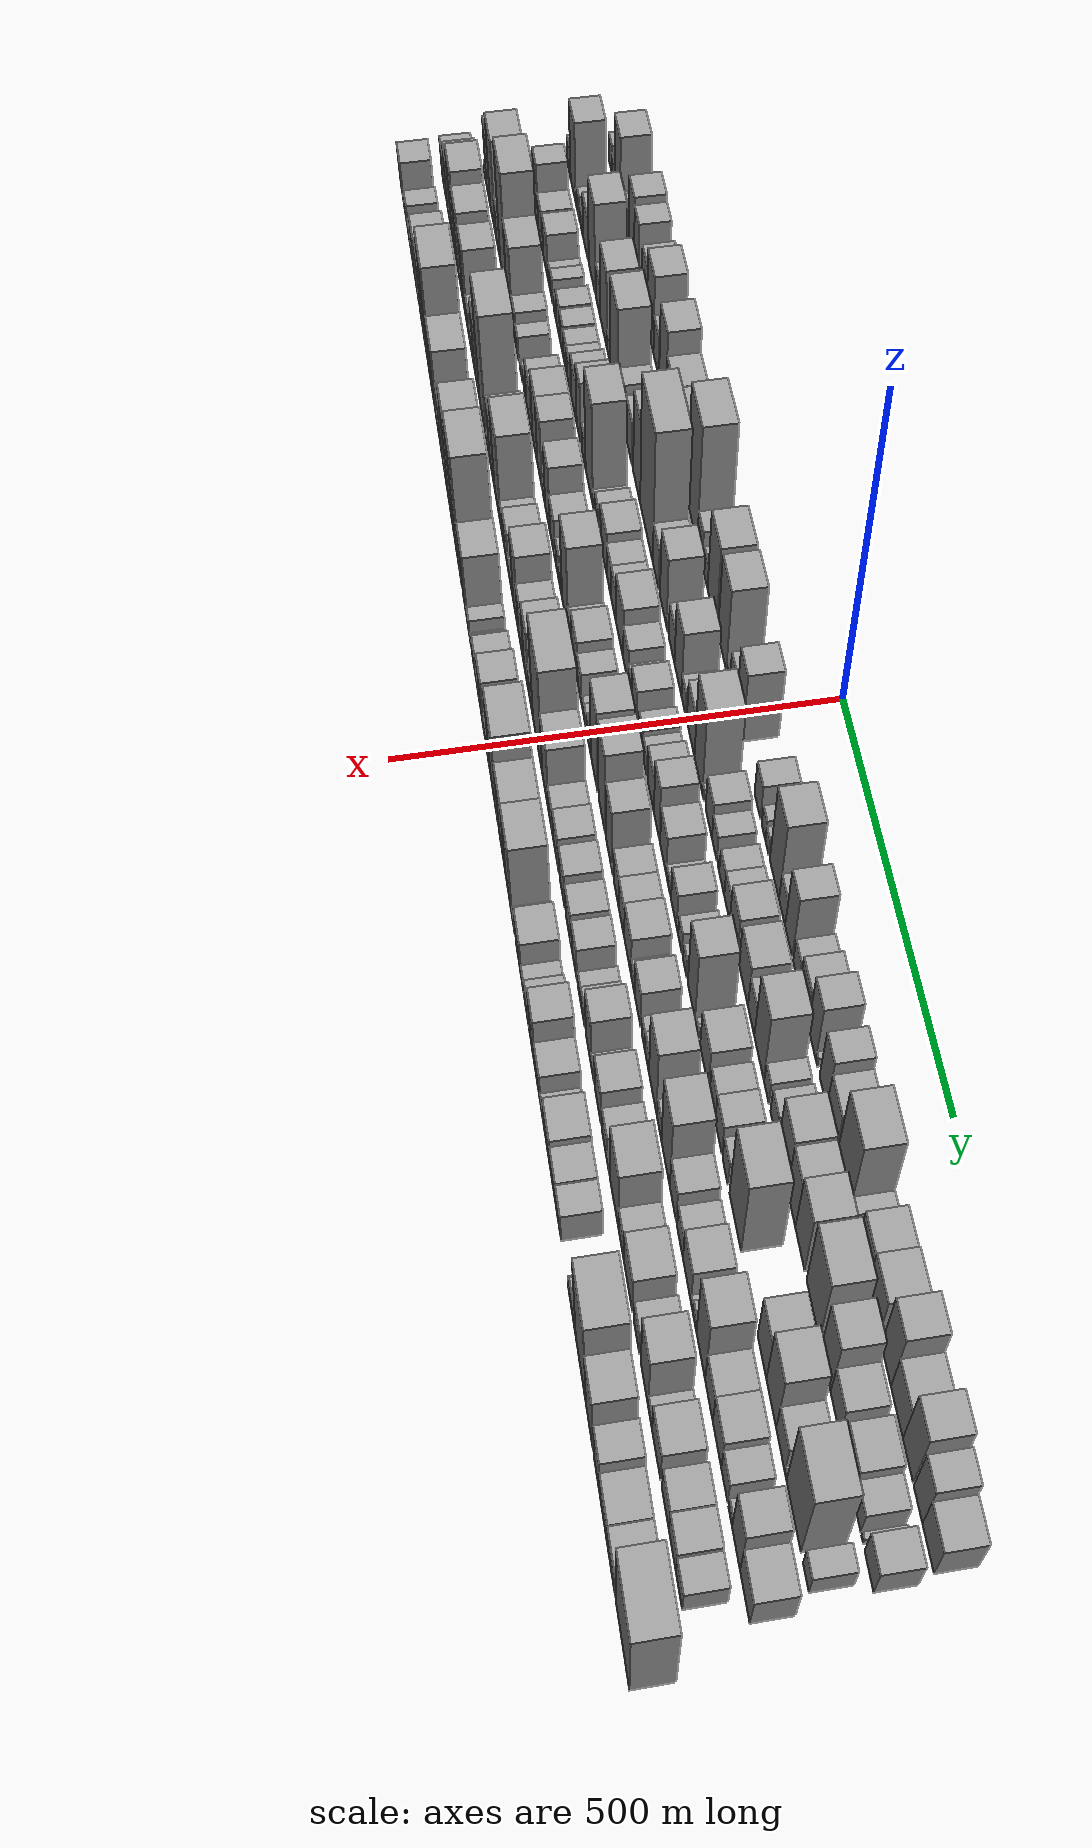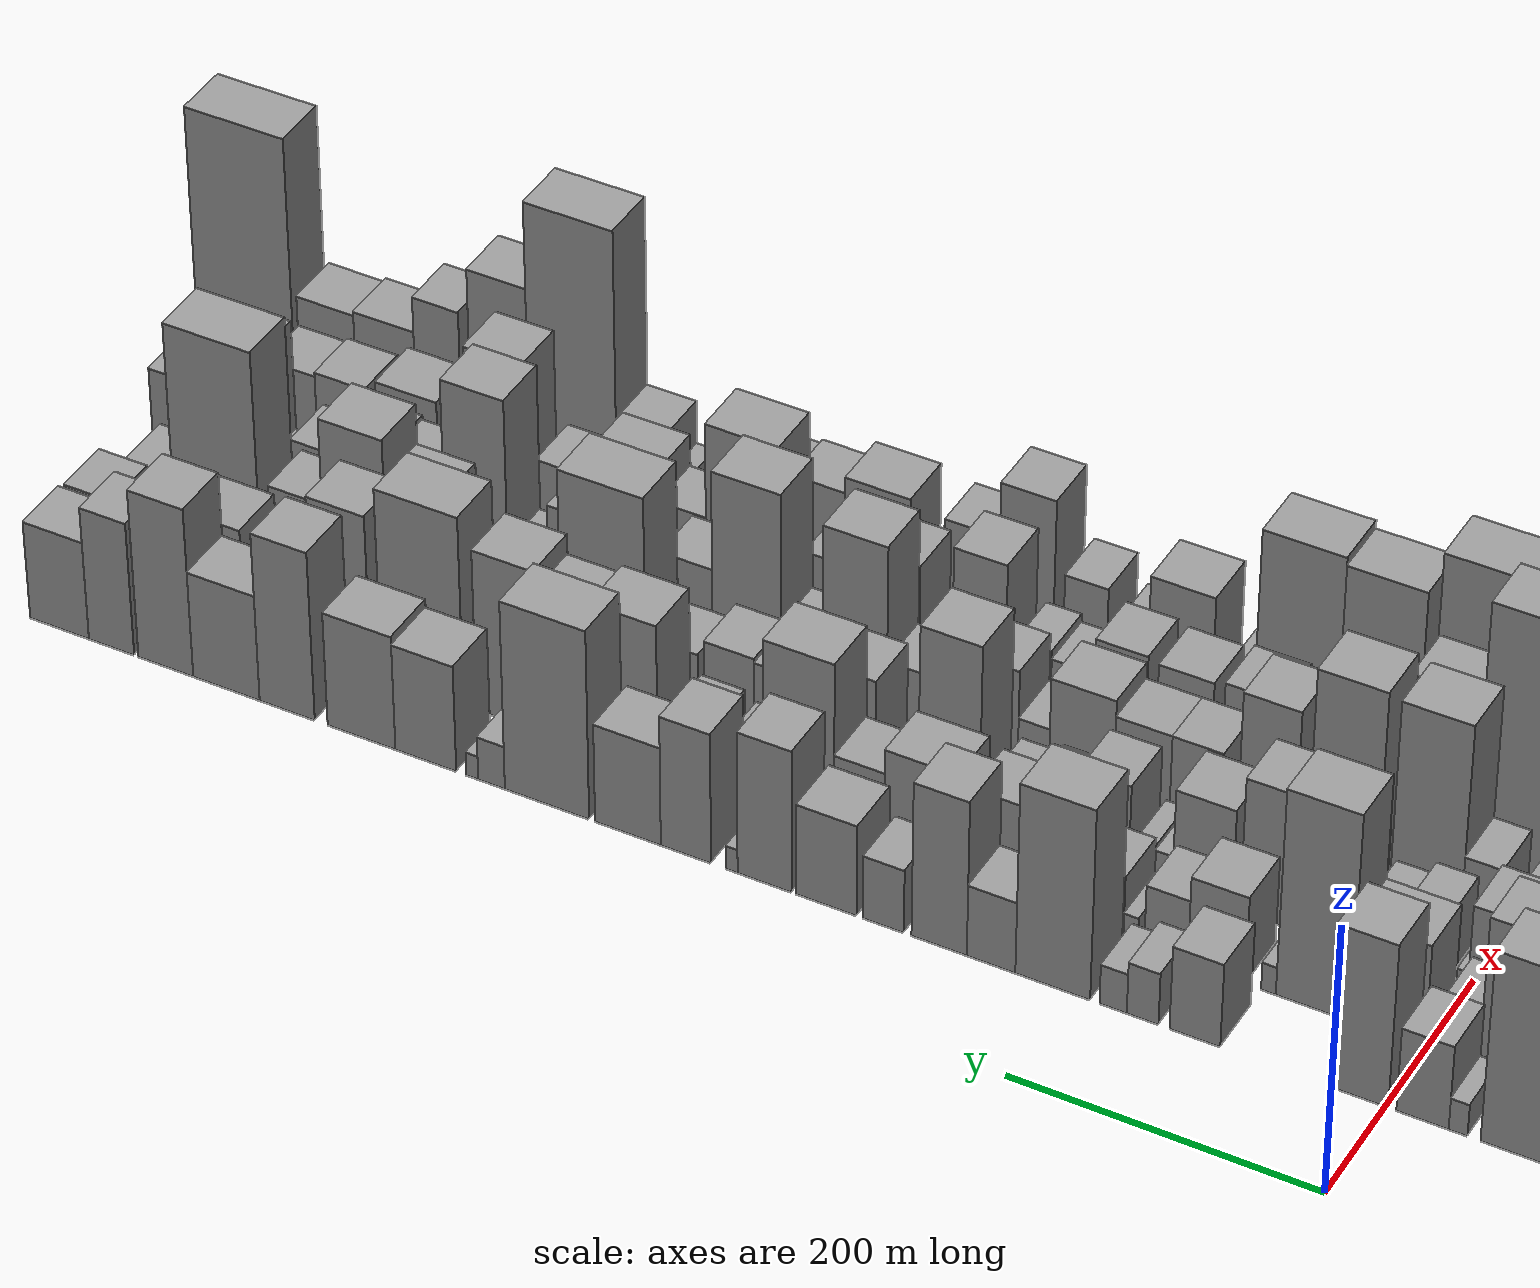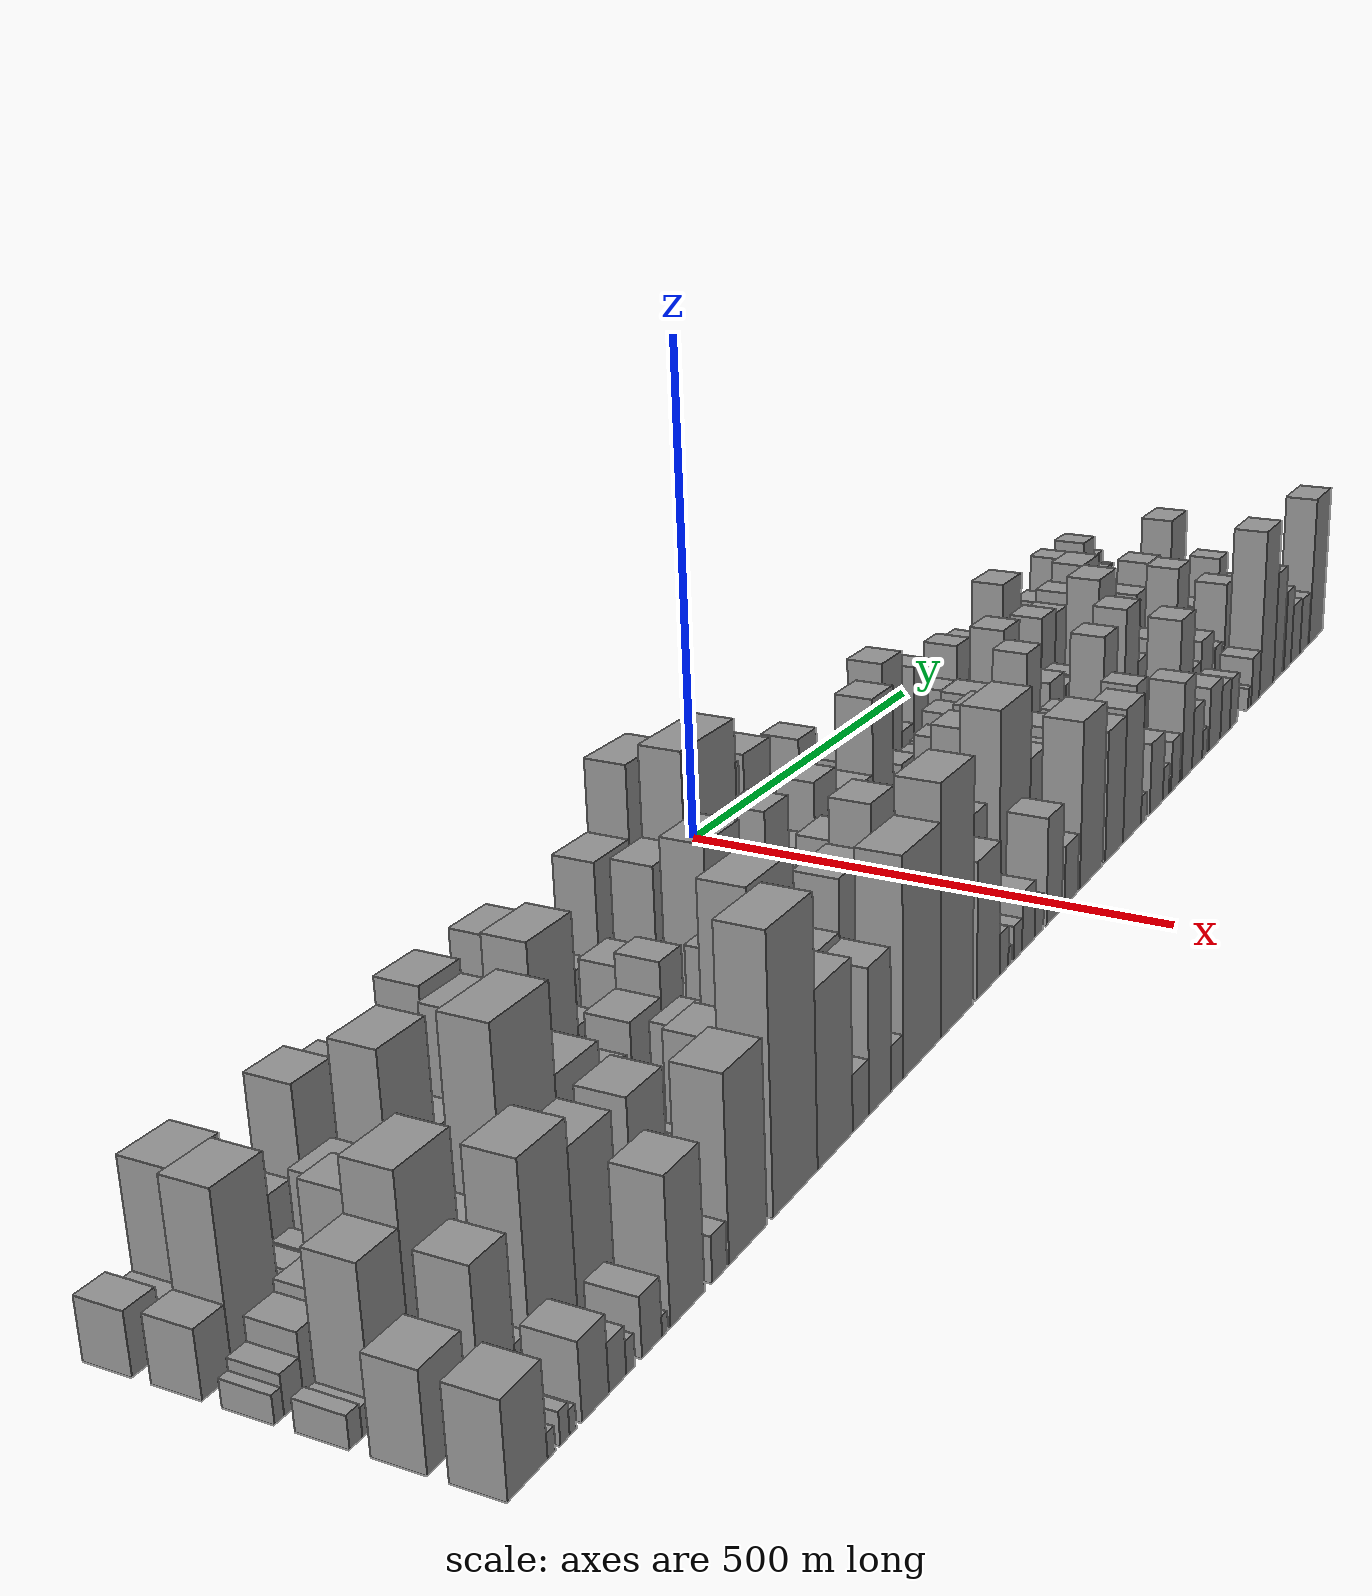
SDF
<sdf version="1.6">
 <world name="default">
  <scene>
   <sky><clouds><speed>12</speed></clouds></sky>
   <ambient>0.4 0.4 0.4 1</ambient>
   <background>0.7 0.7 0.7 1</background>
   <shadows>1</shadows>
  </scene>
  <gravity>0 0 -9.8066</gravity>
  <magnetic_field>6e-06 2.3e-05 -4.2e-05</magnetic_field>
  <physics default="0" name="default_physics" type="ode">
   <ode>
    <solver>
     <type>quick</type>
     <iters>10</iters>
     <sor>1.0</sor>
     <use_dynamic_moi_rescaling>0</use_dynamic_moi_rescaling>
    </solver>
    <constraints>
     <cfm>0</cfm>
     <erp>0.2</erp>
     <contact_max_correcting_vel>100</contact_max_correcting_vel>
     <contact_surface_layer>0.001</contact_surface_layer>
    </constraints>
   </ode>
   <max_step_size>0.004</max_step_size>
   <real_time_factor>1</real_time_factor>
   <real_time_update_rate>250</real_time_update_rate>
  </physics>
  <light name="sun" type="directional">
   <pose>0 0 10 0 0 0</pose>
   <diffuse>0.8 0.8 0.8 1</diffuse>
   <specular>0.2 0.2 0.2 1</specular>
   <attenuation>
    <range>1000</range>
    <constant>0.9</constant>
    <linear>0.01</linear>
    <quadratic>0.001</quadratic>
   </attenuation>
   <direction>-0.5 0.1 -0.9</direction>
  </light>
  <model name="building_1">
   <static>1</static>
   <pose>100.0000 -876.3728 0 0.000000 0.000000 0.000000</pose>
   <link name="link">
    <pose>0 0 24.00 0 0 0</pose>
    <collision name="collision"><geometry><box><size>40.0000 27.2544 48.0000</size></box></geometry></collision>
    <visual name="visual">
     <cast_shadows>0</cast_shadows>
     <geometry><box><size>40.0000 27.2544 48.0000</size></box></geometry>
     <material>
      <script>
       <uri>model://grey_wall/materials/scripts</uri>
       <uri>model://grey_wall/materials/textures</uri>
       <name>vrc/grey_wall</name>
      </script>
     </material>
    </visual>
   </link>
  </model>
  <model name="building_2">
   <static>1</static>
   <pose>100.0000 -852.3113 0 0.000000 0.000000 0.000000</pose>
   <link name="link">
    <pose>0 0 18.00 0 0 0</pose>
    <collision name="collision"><geometry><box><size>40.0000 20.8685 36.0000</size></box></geometry></collision>
    <visual name="visual">
     <cast_shadows>0</cast_shadows>
     <geometry><box><size>40.0000 20.8685 36.0000</size></box></geometry>
     <material>
      <script>
       <uri>model://grey_wall/materials/scripts</uri>
       <uri>model://grey_wall/materials/textures</uri>
       <name>vrc/grey_wall</name>
      </script>
     </material>
    </visual>
   </link>
  </model>
  <model name="building_3">
   <static>1</static>
   <pose>100.0000 -818.5557 0 0.000000 0.000000 0.000000</pose>
   <link name="link">
    <pose>0 0 60.00 0 0 0</pose>
    <collision name="collision"><geometry><box><size>40.0000 46.6428 120.0000</size></box></geometry></collision>
    <visual name="visual">
     <cast_shadows>0</cast_shadows>
     <geometry><box><size>40.0000 46.6428 120.0000</size></box></geometry>
     <material>
      <script>
       <uri>model://grey_wall/materials/scripts</uri>
       <uri>model://grey_wall/materials/textures</uri>
       <name>vrc/grey_wall</name>
      </script>
     </material>
    </visual>
   </link>
  </model>
  <model name="building_4">
   <static>1</static>
   <pose>100.0000 -780.4193 0 0.000000 0.000000 0.000000</pose>
   <link name="link">
    <pose>0 0 18.00 0 0 0</pose>
    <collision name="collision"><geometry><box><size>40.0000 19.6299 36.0000</size></box></geometry></collision>
    <visual name="visual">
     <cast_shadows>0</cast_shadows>
     <geometry><box><size>40.0000 19.6299 36.0000</size></box></geometry>
     <material>
      <script>
       <uri>model://grey_wall/materials/scripts</uri>
       <uri>model://grey_wall/materials/textures</uri>
       <name>vrc/grey_wall</name>
      </script>
     </material>
    </visual>
   </link>
  </model>
  <model name="building_5">
   <static>1</static>
   <pose>100.0000 -751.9083 0 0.000000 0.000000 0.000000</pose>
   <link name="link">
    <pose>0 0 27.00 0 0 0</pose>
    <collision name="collision"><geometry><box><size>40.0000 29.3921 54.0000</size></box></geometry></collision>
    <visual name="visual">
     <cast_shadows>0</cast_shadows>
     <geometry><box><size>40.0000 29.3921 54.0000</size></box></geometry>
     <material>
      <script>
       <uri>model://grey_wall/materials/scripts</uri>
       <uri>model://grey_wall/materials/textures</uri>
       <name>vrc/grey_wall</name>
      </script>
     </material>
    </visual>
   </link>
  </model>
  <model name="building_6">
   <static>1</static>
   <pose>100.0000 -706.8706 0 0.000000 0.000000 0.000000</pose>
   <link name="link">
    <pose>0 0 60.00 0 0 0</pose>
    <collision name="collision"><geometry><box><size>40.0000 40.6833 120.0000</size></box></geometry></collision>
    <visual name="visual">
     <cast_shadows>0</cast_shadows>
     <geometry><box><size>40.0000 40.6833 120.0000</size></box></geometry>
     <material>
      <script>
       <uri>model://grey_wall/materials/scripts</uri>
       <uri>model://grey_wall/materials/textures</uri>
       <name>vrc/grey_wall</name>
      </script>
     </material>
    </visual>
   </link>
  </model>
  <model name="building_7">
   <static>1</static>
   <pose>100.0000 -669.3736 0 0.000000 0.000000 0.000000</pose>
   <link name="link">
    <pose>0 0 54.00 0 0 0</pose>
    <collision name="collision"><geometry><box><size>40.0000 34.3107 108.0000</size></box></geometry></collision>
    <visual name="visual">
     <cast_shadows>0</cast_shadows>
     <geometry><box><size>40.0000 34.3107 108.0000</size></box></geometry>
     <material>
      <script>
       <uri>model://grey_wall/materials/scripts</uri>
       <uri>model://grey_wall/materials/textures</uri>
       <name>vrc/grey_wall</name>
      </script>
     </material>
    </visual>
   </link>
  </model>
  <model name="building_8">
   <static>1</static>
   <pose>100.0000 -636.2702 0 0.000000 0.000000 0.000000</pose>
   <link name="link">
    <pose>0 0 15.00 0 0 0</pose>
    <collision name="collision"><geometry><box><size>40.0000 17.8961 30.0000</size></box></geometry></collision>
    <visual name="visual">
     <cast_shadows>0</cast_shadows>
     <geometry><box><size>40.0000 17.8961 30.0000</size></box></geometry>
     <material>
      <script>
       <uri>model://grey_wall/materials/scripts</uri>
       <uri>model://grey_wall/materials/textures</uri>
       <name>vrc/grey_wall</name>
      </script>
     </material>
    </visual>
   </link>
  </model>
  <model name="building_9">
   <static>1</static>
   <pose>100.0000 -608.3308 0 0.000000 0.000000 0.000000</pose>
   <link name="link">
    <pose>0 0 49.50 0 0 0</pose>
    <collision name="collision"><geometry><box><size>40.0000 37.9828 99.0000</size></box></geometry></collision>
    <visual name="visual">
     <cast_shadows>0</cast_shadows>
     <geometry><box><size>40.0000 37.9828 99.0000</size></box></geometry>
     <material>
      <script>
       <uri>model://grey_wall/materials/scripts</uri>
       <uri>model://grey_wall/materials/textures</uri>
       <name>vrc/grey_wall</name>
      </script>
     </material>
    </visual>
   </link>
  </model>
  <model name="building_10">
   <static>1</static>
   <pose>100.0000 -564.8110 0 0.000000 0.000000 0.000000</pose>
   <link name="link">
    <pose>0 0 64.50 0 0 0</pose>
    <collision name="collision"><geometry><box><size>40.0000 49.0566 129.0000</size></box></geometry></collision>
    <visual name="visual">
     <cast_shadows>0</cast_shadows>
     <geometry><box><size>40.0000 49.0566 129.0000</size></box></geometry>
     <material>
      <script>
       <uri>model://grey_wall/materials/scripts</uri>
       <uri>model://grey_wall/materials/textures</uri>
       <name>vrc/grey_wall</name>
      </script>
     </material>
    </visual>
   </link>
  </model>
  <model name="building_11">
   <static>1</static>
   <pose>100.0000 -522.8682 0 0.000000 0.000000 0.000000</pose>
   <link name="link">
    <pose>0 0 33.00 0 0 0</pose>
    <collision name="collision"><geometry><box><size>40.0000 34.8290 66.0000</size></box></geometry></collision>
    <visual name="visual">
     <cast_shadows>0</cast_shadows>
     <geometry><box><size>40.0000 34.8290 66.0000</size></box></geometry>
     <material>
      <script>
       <uri>model://grey_wall/materials/scripts</uri>
       <uri>model://grey_wall/materials/textures</uri>
       <name>vrc/grey_wall</name>
      </script>
     </material>
    </visual>
   </link>
  </model>
  <model name="building_12">
   <static>1</static>
   <pose>100.0000 -502.3268 0 0.000000 0.000000 0.000000</pose>
   <link name="link">
    <pose>0 0 7.50 0 0 0</pose>
    <collision name="collision"><geometry><box><size>40.0000 6.2540 15.0000</size></box></geometry></collision>
    <visual name="visual">
     <cast_shadows>0</cast_shadows>
     <geometry><box><size>40.0000 6.2540 15.0000</size></box></geometry>
     <material>
      <script>
       <uri>model://grey_wall/materials/scripts</uri>
       <uri>model://grey_wall/materials/textures</uri>
       <name>vrc/grey_wall</name>
      </script>
     </material>
    </visual>
   </link>
  </model>
  <model name="building_13">
   <static>1</static>
   <pose>100.0000 -474.6514 0 0.000000 0.000000 0.000000</pose>
   <link name="link">
    <pose>0 0 64.50 0 0 0</pose>
    <collision name="collision"><geometry><box><size>40.0000 49.0968 129.0000</size></box></geometry></collision>
    <visual name="visual">
     <cast_shadows>0</cast_shadows>
     <geometry><box><size>40.0000 49.0968 129.0000</size></box></geometry>
     <material>
      <script>
       <uri>model://grey_wall/materials/scripts</uri>
       <uri>model://grey_wall/materials/textures</uri>
       <name>vrc/grey_wall</name>
      </script>
     </material>
    </visual>
   </link>
  </model>
  <model name="building_14">
   <static>1</static>
   <pose>100.0000 -424.9528 0 0.000000 0.000000 0.000000</pose>
   <link name="link">
    <pose>0 0 45.00 0 0 0</pose>
    <collision name="collision"><geometry><box><size>40.0000 50.3003 90.0000</size></box></geometry></collision>
    <visual name="visual">
     <cast_shadows>0</cast_shadows>
     <geometry><box><size>40.0000 50.3003 90.0000</size></box></geometry>
     <material>
      <script>
       <uri>model://grey_wall/materials/scripts</uri>
       <uri>model://grey_wall/materials/textures</uri>
       <name>vrc/grey_wall</name>
      </script>
     </material>
    </visual>
   </link>
  </model>
  <model name="building_15">
   <static>1</static>
   <pose>100.0000 -383.8608 0 0.000000 0.000000 0.000000</pose>
   <link name="link">
    <pose>0 0 27.00 0 0 0</pose>
    <collision name="collision"><geometry><box><size>40.0000 31.8836 54.0000</size></box></geometry></collision>
    <visual name="visual">
     <cast_shadows>0</cast_shadows>
     <geometry><box><size>40.0000 31.8836 54.0000</size></box></geometry>
     <material>
      <script>
       <uri>model://grey_wall/materials/scripts</uri>
       <uri>model://grey_wall/materials/textures</uri>
       <name>vrc/grey_wall</name>
      </script>
     </material>
    </visual>
   </link>
  </model>
  <model name="building_16">
   <static>1</static>
   <pose>100.0000 -363.3936 0 0.000000 0.000000 0.000000</pose>
   <link name="link">
    <pose>0 0 10.50 0 0 0</pose>
    <collision name="collision"><geometry><box><size>40.0000 9.0508 21.0000</size></box></geometry></collision>
    <visual name="visual">
     <cast_shadows>0</cast_shadows>
     <geometry><box><size>40.0000 9.0508 21.0000</size></box></geometry>
     <material>
      <script>
       <uri>model://grey_wall/materials/scripts</uri>
       <uri>model://grey_wall/materials/textures</uri>
       <name>vrc/grey_wall</name>
      </script>
     </material>
    </visual>
   </link>
  </model>
  <model name="building_17">
   <static>1</static>
   <pose>100.0000 -331.9854 0 0.000000 0.000000 0.000000</pose>
   <link name="link">
    <pose>0 0 67.50 0 0 0</pose>
    <collision name="collision"><geometry><box><size>40.0000 53.7657 135.0000</size></box></geometry></collision>
    <visual name="visual">
     <cast_shadows>0</cast_shadows>
     <geometry><box><size>40.0000 53.7657 135.0000</size></box></geometry>
     <material>
      <script>
       <uri>model://grey_wall/materials/scripts</uri>
       <uri>model://grey_wall/materials/textures</uri>
       <name>vrc/grey_wall</name>
      </script>
     </material>
    </visual>
   </link>
  </model>
  <model name="building_18">
   <static>1</static>
   <pose>100.0000 -271.7139 0 0.000000 0.000000 0.000000</pose>
   <link name="link">
    <pose>0 0 100.50 0 0 0</pose>
    <collision name="collision"><geometry><box><size>40.0000 66.7772 201.0000</size></box></geometry></collision>
    <visual name="visual">
     <cast_shadows>0</cast_shadows>
     <geometry><box><size>40.0000 66.7772 201.0000</size></box></geometry>
     <material>
      <script>
       <uri>model://grey_wall/materials/scripts</uri>
       <uri>model://grey_wall/materials/textures</uri>
       <name>vrc/grey_wall</name>
      </script>
     </material>
    </visual>
   </link>
  </model>
  <model name="building_19">
   <static>1</static>
   <pose>100.0000 -222.7142 0 0.000000 0.000000 0.000000</pose>
   <link name="link">
    <pose>0 0 30.00 0 0 0</pose>
    <collision name="collision"><geometry><box><size>40.0000 31.2222 60.0000</size></box></geometry></collision>
    <visual name="visual">
     <cast_shadows>0</cast_shadows>
     <geometry><box><size>40.0000 31.2222 60.0000</size></box></geometry>
     <material>
      <script>
       <uri>model://grey_wall/materials/scripts</uri>
       <uri>model://grey_wall/materials/textures</uri>
       <name>vrc/grey_wall</name>
      </script>
     </material>
    </visual>
   </link>
  </model>
  <model name="building_20">
   <static>1</static>
   <pose>100.0000 -203.2409 0 0.000000 0.000000 0.000000</pose>
   <link name="link">
    <pose>0 0 9.00 0 0 0</pose>
    <collision name="collision"><geometry><box><size>40.0000 7.7245 18.0000</size></box></geometry></collision>
    <visual name="visual">
     <cast_shadows>0</cast_shadows>
     <geometry><box><size>40.0000 7.7245 18.0000</size></box></geometry>
     <material>
      <script>
       <uri>model://grey_wall/materials/scripts</uri>
       <uri>model://grey_wall/materials/textures</uri>
       <name>vrc/grey_wall</name>
      </script>
     </material>
    </visual>
   </link>
  </model>
  <model name="building_21">
   <static>1</static>
   <pose>100.0000 -186.2058 0 0.000000 0.000000 0.000000</pose>
   <link name="link">
    <pose>0 0 22.50 0 0 0</pose>
    <collision name="collision"><geometry><box><size>40.0000 26.3457 45.0000</size></box></geometry></collision>
    <visual name="visual">
     <cast_shadows>0</cast_shadows>
     <geometry><box><size>40.0000 26.3457 45.0000</size></box></geometry>
     <material>
      <script>
       <uri>model://grey_wall/materials/scripts</uri>
       <uri>model://grey_wall/materials/textures</uri>
       <name>vrc/grey_wall</name>
      </script>
     </material>
    </visual>
   </link>
  </model>
  <model name="building_22">
   <static>1</static>
   <pose>100.0000 -145.5130 0 0.000000 0.000000 0.000000</pose>
   <link name="link">
    <pose>0 0 70.50 0 0 0</pose>
    <collision name="collision"><geometry><box><size>40.0000 55.0400 141.0000</size></box></geometry></collision>
    <visual name="visual">
     <cast_shadows>0</cast_shadows>
     <geometry><box><size>40.0000 55.0400 141.0000</size></box></geometry>
     <material>
      <script>
       <uri>model://grey_wall/materials/scripts</uri>
       <uri>model://grey_wall/materials/textures</uri>
       <name>vrc/grey_wall</name>
      </script>
     </material>
    </visual>
   </link>
  </model>
  <model name="building_23">
   <static>1</static>
   <pose>100.0000 -83.5409 0 0.000000 0.000000 0.000000</pose>
   <link name="link">
    <pose>0 0 72.00 0 0 0</pose>
    <collision name="collision"><geometry><box><size>40.0000 50.9042 144.0000</size></box></geometry></collision>
    <visual name="visual">
     <cast_shadows>0</cast_shadows>
     <geometry><box><size>40.0000 50.9042 144.0000</size></box></geometry>
     <material>
      <script>
       <uri>model://grey_wall/materials/scripts</uri>
       <uri>model://grey_wall/materials/textures</uri>
       <name>vrc/grey_wall</name>
      </script>
     </material>
    </visual>
   </link>
  </model>
  <model name="building_24">
   <static>1</static>
   <pose>100.0000 -44.2805 0 0.000000 0.000000 0.000000</pose>
   <link name="link">
    <pose>0 0 12.00 0 0 0</pose>
    <collision name="collision"><geometry><box><size>40.0000 11.6164 24.0000</size></box></geometry></collision>
    <visual name="visual">
     <cast_shadows>0</cast_shadows>
     <geometry><box><size>40.0000 11.6164 24.0000</size></box></geometry>
     <material>
      <script>
       <uri>model://grey_wall/materials/scripts</uri>
       <uri>model://grey_wall/materials/textures</uri>
       <name>vrc/grey_wall</name>
      </script>
     </material>
    </visual>
   </link>
  </model>
  <model name="building_25">
   <static>1</static>
   <pose>100.0000 -22.2660 0 0.000000 0.000000 0.000000</pose>
   <link name="link">
    <pose>0 0 31.50 0 0 0</pose>
    <collision name="collision"><geometry><box><size>40.0000 32.4127 63.0000</size></box></geometry></collision>
    <visual name="visual">
     <cast_shadows>0</cast_shadows>
     <geometry><box><size>40.0000 32.4127 63.0000</size></box></geometry>
     <material>
      <script>
       <uri>model://grey_wall/materials/scripts</uri>
       <uri>model://grey_wall/materials/textures</uri>
       <name>vrc/grey_wall</name>
      </script>
     </material>
    </visual>
   </link>
  </model>
  <model name="building_26">
   <static>1</static>
   <pose>100.0000 17.9681 0 0.000000 0.000000 0.000000</pose>
   <link name="link">
    <pose>0 0 61.50 0 0 0</pose>
    <collision name="collision"><geometry><box><size>40.0000 38.0555 123.0000</size></box></geometry></collision>
    <visual name="visual">
     <cast_shadows>0</cast_shadows>
     <geometry><box><size>40.0000 38.0555 123.0000</size></box></geometry>
     <material>
      <script>
       <uri>model://grey_wall/materials/scripts</uri>
       <uri>model://grey_wall/materials/textures</uri>
       <name>vrc/grey_wall</name>
      </script>
     </material>
    </visual>
   </link>
  </model>
  <model name="building_27">
   <static>1</static>
   <pose>100.0000 120.3168 0 0.000000 0.000000 0.000000</pose>
   <link name="link">
    <pose>0 0 31.50 0 0 0</pose>
    <collision name="collision"><geometry><box><size>40.0000 32.2140 63.0000</size></box></geometry></collision>
    <visual name="visual">
     <cast_shadows>0</cast_shadows>
     <geometry><box><size>40.0000 32.2140 63.0000</size></box></geometry>
     <material>
      <script>
       <uri>model://grey_wall/materials/scripts</uri>
       <uri>model://grey_wall/materials/textures</uri>
       <name>vrc/grey_wall</name>
      </script>
     </material>
    </visual>
   </link>
  </model>
  <model name="building_28">
   <static>1</static>
   <pose>100.0000 153.5409 0 0.000000 0.000000 0.000000</pose>
   <link name="link">
    <pose>0 0 19.50 0 0 0</pose>
    <collision name="collision"><geometry><box><size>40.0000 20.2342 39.0000</size></box></geometry></collision>
    <visual name="visual">
     <cast_shadows>0</cast_shadows>
     <geometry><box><size>40.0000 20.2342 39.0000</size></box></geometry>
     <material>
      <script>
       <uri>model://grey_wall/materials/scripts</uri>
       <uri>model://grey_wall/materials/textures</uri>
       <name>vrc/grey_wall</name>
      </script>
     </material>
    </visual>
   </link>
  </model>
  <model name="building_29">
   <static>1</static>
   <pose>100.0000 172.3773 0 0.000000 0.000000 0.000000</pose>
   <link name="link">
    <pose>0 0 15.00 0 0 0</pose>
    <collision name="collision"><geometry><box><size>40.0000 17.4387 30.0000</size></box></geometry></collision>
    <visual name="visual">
     <cast_shadows>0</cast_shadows>
     <geometry><box><size>40.0000 17.4387 30.0000</size></box></geometry>
     <material>
      <script>
       <uri>model://grey_wall/materials/scripts</uri>
       <uri>model://grey_wall/materials/textures</uri>
       <name>vrc/grey_wall</name>
      </script>
     </material>
    </visual>
   </link>
  </model>
  <model name="building_30">
   <static>1</static>
   <pose>100.0000 211.2149 0 0.000000 0.000000 0.000000</pose>
   <link name="link">
    <pose>0 0 72.00 0 0 0</pose>
    <collision name="collision"><geometry><box><size>40.0000 48.2366 144.0000</size></box></geometry></collision>
    <visual name="visual">
     <cast_shadows>0</cast_shadows>
     <geometry><box><size>40.0000 48.2366 144.0000</size></box></geometry>
     <material>
      <script>
       <uri>model://grey_wall/materials/scripts</uri>
       <uri>model://grey_wall/materials/textures</uri>
       <name>vrc/grey_wall</name>
      </script>
     </material>
    </visual>
   </link>
  </model>
  <model name="building_31">
   <static>1</static>
   <pose>100.0000 251.0738 0 0.000000 0.000000 0.000000</pose>
   <link name="link">
    <pose>0 0 27.00 0 0 0</pose>
    <collision name="collision"><geometry><box><size>40.0000 31.4812 54.0000</size></box></geometry></collision>
    <visual name="visual">
     <cast_shadows>0</cast_shadows>
     <geometry><box><size>40.0000 31.4812 54.0000</size></box></geometry>
     <material>
      <script>
       <uri>model://grey_wall/materials/scripts</uri>
       <uri>model://grey_wall/materials/textures</uri>
       <name>vrc/grey_wall</name>
      </script>
     </material>
    </visual>
   </link>
  </model>
  <model name="building_32">
   <static>1</static>
   <pose>100.0000 284.8577 0 0.000000 0.000000 0.000000</pose>
   <link name="link">
    <pose>0 0 58.50 0 0 0</pose>
    <collision name="collision"><geometry><box><size>40.0000 36.0865 117.0000</size></box></geometry></collision>
    <visual name="visual">
     <cast_shadows>0</cast_shadows>
     <geometry><box><size>40.0000 36.0865 117.0000</size></box></geometry>
     <material>
      <script>
       <uri>model://grey_wall/materials/scripts</uri>
       <uri>model://grey_wall/materials/textures</uri>
       <name>vrc/grey_wall</name>
      </script>
     </material>
    </visual>
   </link>
  </model>
  <model name="building_33">
   <static>1</static>
   <pose>100.0000 321.3715 0 0.000000 0.000000 0.000000</pose>
   <link name="link">
    <pose>0 0 24.00 0 0 0</pose>
    <collision name="collision"><geometry><box><size>40.0000 26.9410 48.0000</size></box></geometry></collision>
    <visual name="visual">
     <cast_shadows>0</cast_shadows>
     <geometry><box><size>40.0000 26.9410 48.0000</size></box></geometry>
     <material>
      <script>
       <uri>model://grey_wall/materials/scripts</uri>
       <uri>model://grey_wall/materials/textures</uri>
       <name>vrc/grey_wall</name>
      </script>
     </material>
    </visual>
   </link>
  </model>
  <model name="building_34">
   <static>1</static>
   <pose>100.0000 358.8824 0 0.000000 0.000000 0.000000</pose>
   <link name="link">
    <pose>0 0 34.50 0 0 0</pose>
    <collision name="collision"><geometry><box><size>40.0000 40.0808 69.0000</size></box></geometry></collision>
    <visual name="visual">
     <cast_shadows>0</cast_shadows>
     <geometry><box><size>40.0000 40.0808 69.0000</size></box></geometry>
     <material>
      <script>
       <uri>model://grey_wall/materials/scripts</uri>
       <uri>model://grey_wall/materials/textures</uri>
       <name>vrc/grey_wall</name>
      </script>
     </material>
    </visual>
   </link>
  </model>
  <model name="building_35">
   <static>1</static>
   <pose>100.0000 399.8596 0 0.000000 0.000000 0.000000</pose>
   <link name="link">
    <pose>0 0 54.00 0 0 0</pose>
    <collision name="collision"><geometry><box><size>40.0000 35.8738 108.0000</size></box></geometry></collision>
    <visual name="visual">
     <cast_shadows>0</cast_shadows>
     <geometry><box><size>40.0000 35.8738 108.0000</size></box></geometry>
     <material>
      <script>
       <uri>model://grey_wall/materials/scripts</uri>
       <uri>model://grey_wall/materials/textures</uri>
       <name>vrc/grey_wall</name>
      </script>
     </material>
    </visual>
   </link>
  </model>
  <model name="building_36">
   <static>1</static>
   <pose>100.0000 421.6784 0 0.000000 0.000000 0.000000</pose>
   <link name="link">
    <pose>0 0 9.00 0 0 0</pose>
    <collision name="collision"><geometry><box><size>40.0000 7.7637 18.0000</size></box></geometry></collision>
    <visual name="visual">
     <cast_shadows>0</cast_shadows>
     <geometry><box><size>40.0000 7.7637 18.0000</size></box></geometry>
     <material>
      <script>
       <uri>model://grey_wall/materials/scripts</uri>
       <uri>model://grey_wall/materials/textures</uri>
       <name>vrc/grey_wall</name>
      </script>
     </material>
    </visual>
   </link>
  </model>
  <model name="building_37">
   <static>1</static>
   <pose>100.0000 452.3926 0 0.000000 0.000000 0.000000</pose>
   <link name="link">
    <pose>0 0 49.50 0 0 0</pose>
    <collision name="collision"><geometry><box><size>40.0000 33.6649 99.0000</size></box></geometry></collision>
    <visual name="visual">
     <cast_shadows>0</cast_shadows>
     <geometry><box><size>40.0000 33.6649 99.0000</size></box></geometry>
     <material>
      <script>
       <uri>model://grey_wall/materials/scripts</uri>
       <uri>model://grey_wall/materials/textures</uri>
       <name>vrc/grey_wall</name>
      </script>
     </material>
    </visual>
   </link>
  </model>
  <model name="building_38">
   <static>1</static>
   <pose>100.0000 491.4287 0 0.000000 0.000000 0.000000</pose>
   <link name="link">
    <pose>0 0 37.50 0 0 0</pose>
    <collision name="collision"><geometry><box><size>40.0000 44.4073 75.0000</size></box></geometry></collision>
    <visual name="visual">
     <cast_shadows>0</cast_shadows>
     <geometry><box><size>40.0000 44.4073 75.0000</size></box></geometry>
     <material>
      <script>
       <uri>model://grey_wall/materials/scripts</uri>
       <uri>model://grey_wall/materials/textures</uri>
       <name>vrc/grey_wall</name>
      </script>
     </material>
    </visual>
   </link>
  </model>
  <model name="building_39">
   <static>1</static>
   <pose>100.0000 546.3660 0 0.000000 0.000000 0.000000</pose>
   <link name="link">
    <pose>0 0 72.00 0 0 0</pose>
    <collision name="collision"><geometry><box><size>40.0000 57.4672 144.0000</size></box></geometry></collision>
    <visual name="visual">
     <cast_shadows>0</cast_shadows>
     <geometry><box><size>40.0000 57.4672 144.0000</size></box></geometry>
     <material>
      <script>
       <uri>model://grey_wall/materials/scripts</uri>
       <uri>model://grey_wall/materials/textures</uri>
       <name>vrc/grey_wall</name>
      </script>
     </material>
    </visual>
   </link>
  </model>
  <model name="building_40">
   <static>1</static>
   <pose>100.0000 584.2529 0 0.000000 0.000000 0.000000</pose>
   <link name="link">
    <pose>0 0 16.50 0 0 0</pose>
    <collision name="collision"><geometry><box><size>40.0000 18.3066 33.0000</size></box></geometry></collision>
    <visual name="visual">
     <cast_shadows>0</cast_shadows>
     <geometry><box><size>40.0000 18.3066 33.0000</size></box></geometry>
     <material>
      <script>
       <uri>model://grey_wall/materials/scripts</uri>
       <uri>model://grey_wall/materials/textures</uri>
       <name>vrc/grey_wall</name>
      </script>
     </material>
    </visual>
   </link>
  </model>
  <model name="building_41">
   <static>1</static>
   <pose>100.0000 597.4368 0 0.000000 0.000000 0.000000</pose>
   <link name="link">
    <pose>0 0 9.00 0 0 0</pose>
    <collision name="collision"><geometry><box><size>40.0000 8.0611 18.0000</size></box></geometry></collision>
    <visual name="visual">
     <cast_shadows>0</cast_shadows>
     <geometry><box><size>40.0000 8.0611 18.0000</size></box></geometry>
     <material>
      <script>
       <uri>model://grey_wall/materials/scripts</uri>
       <uri>model://grey_wall/materials/textures</uri>
       <name>vrc/grey_wall</name>
      </script>
     </material>
    </visual>
   </link>
  </model>
  <model name="building_42">
   <static>1</static>
   <pose>100.0000 629.4989 0 0.000000 0.000000 0.000000</pose>
   <link name="link">
    <pose>0 0 40.50 0 0 0</pose>
    <collision name="collision"><geometry><box><size>40.0000 42.0633 81.0000</size></box></geometry></collision>
    <visual name="visual">
     <cast_shadows>0</cast_shadows>
     <geometry><box><size>40.0000 42.0633 81.0000</size></box></geometry>
     <material>
      <script>
       <uri>model://grey_wall/materials/scripts</uri>
       <uri>model://grey_wall/materials/textures</uri>
       <name>vrc/grey_wall</name>
      </script>
     </material>
    </visual>
   </link>
  </model>
  <model name="building_43">
   <static>1</static>
   <pose>100.0000 674.1150 0 0.000000 0.000000 0.000000</pose>
   <link name="link">
    <pose>0 0 43.50 0 0 0</pose>
    <collision name="collision"><geometry><box><size>40.0000 47.1688 87.0000</size></box></geometry></collision>
    <visual name="visual">
     <cast_shadows>0</cast_shadows>
     <geometry><box><size>40.0000 47.1688 87.0000</size></box></geometry>
     <material>
      <script>
       <uri>model://grey_wall/materials/scripts</uri>
       <uri>model://grey_wall/materials/textures</uri>
       <name>vrc/grey_wall</name>
      </script>
     </material>
    </visual>
   </link>
  </model>
  <model name="building_44">
   <static>1</static>
   <pose>100.0000 726.0503 0 0.000000 0.000000 0.000000</pose>
   <link name="link">
    <pose>0 0 64.50 0 0 0</pose>
    <collision name="collision"><geometry><box><size>40.0000 38.7017 129.0000</size></box></geometry></collision>
    <visual name="visual">
     <cast_shadows>0</cast_shadows>
     <geometry><box><size>40.0000 38.7017 129.0000</size></box></geometry>
     <material>
      <script>
       <uri>model://grey_wall/materials/scripts</uri>
       <uri>model://grey_wall/materials/textures</uri>
       <name>vrc/grey_wall</name>
      </script>
     </material>
    </visual>
   </link>
  </model>
  <model name="building_45">
   <static>1</static>
   <pose>100.0000 768.8857 0 0.000000 0.000000 0.000000</pose>
   <link name="link">
    <pose>0 0 40.50 0 0 0</pose>
    <collision name="collision"><geometry><box><size>40.0000 46.9692 81.0000</size></box></geometry></collision>
    <visual name="visual">
     <cast_shadows>0</cast_shadows>
     <geometry><box><size>40.0000 46.9692 81.0000</size></box></geometry>
     <material>
      <script>
       <uri>model://grey_wall/materials/scripts</uri>
       <uri>model://grey_wall/materials/textures</uri>
       <name>vrc/grey_wall</name>
      </script>
     </material>
    </visual>
   </link>
  </model>
  <model name="building_46">
   <static>1</static>
   <pose>100.0000 811.8883 0 0.000000 0.000000 0.000000</pose>
   <link name="link">
    <pose>0 0 64.50 0 0 0</pose>
    <collision name="collision"><geometry><box><size>40.0000 39.0361 129.0000</size></box></geometry></collision>
    <visual name="visual">
     <cast_shadows>0</cast_shadows>
     <geometry><box><size>40.0000 39.0361 129.0000</size></box></geometry>
     <material>
      <script>
       <uri>model://grey_wall/materials/scripts</uri>
       <uri>model://grey_wall/materials/textures</uri>
       <name>vrc/grey_wall</name>
      </script>
     </material>
    </visual>
   </link>
  </model>
  <model name="building_47">
   <static>1</static>
   <pose>100.0000 850.6495 0 0.000000 0.000000 0.000000</pose>
   <link name="link">
    <pose>0 0 51.00 0 0 0</pose>
    <collision name="collision"><geometry><box><size>40.0000 32.4864 102.0000</size></box></geometry></collision>
    <visual name="visual">
     <cast_shadows>0</cast_shadows>
     <geometry><box><size>40.0000 32.4864 102.0000</size></box></geometry>
     <material>
      <script>
       <uri>model://grey_wall/materials/scripts</uri>
       <uri>model://grey_wall/materials/textures</uri>
       <name>vrc/grey_wall</name>
      </script>
     </material>
    </visual>
   </link>
  </model>
  <model name="building_48">
   <static>1</static>
   <pose>100.0000 888.0390 0 0.000000 0.000000 0.000000</pose>
   <link name="link">
    <pose>0 0 37.50 0 0 0</pose>
    <collision name="collision"><geometry><box><size>40.0000 42.2925 75.0000</size></box></geometry></collision>
    <visual name="visual">
     <cast_shadows>0</cast_shadows>
     <geometry><box><size>40.0000 42.2925 75.0000</size></box></geometry>
     <material>
      <script>
       <uri>model://grey_wall/materials/scripts</uri>
       <uri>model://grey_wall/materials/textures</uri>
       <name>vrc/grey_wall</name>
      </script>
     </material>
    </visual>
   </link>
  </model>
  <model name="building_49">
   <static>1</static>
   <pose>155.0000 -876.6113 0 0.000000 0.000000 0.000000</pose>
   <link name="link">
    <pose>0 0 25.50 0 0 0</pose>
    <collision name="collision"><geometry><box><size>40.0000 26.7774 51.0000</size></box></geometry></collision>
    <visual name="visual">
     <cast_shadows>0</cast_shadows>
     <geometry><box><size>40.0000 26.7774 51.0000</size></box></geometry>
     <material>
      <script>
       <uri>model://grey_wall/materials/scripts</uri>
       <uri>model://grey_wall/materials/textures</uri>
       <name>vrc/grey_wall</name>
      </script>
     </material>
    </visual>
   </link>
  </model>
  <model name="building_50">
   <static>1</static>
   <pose>155.0000 -840.0376 0 0.000000 0.000000 0.000000</pose>
   <link name="link">
    <pose>0 0 66.00 0 0 0</pose>
    <collision name="collision"><geometry><box><size>40.0000 46.3701 132.0000</size></box></geometry></collision>
    <visual name="visual">
     <cast_shadows>0</cast_shadows>
     <geometry><box><size>40.0000 46.3701 132.0000</size></box></geometry>
     <material>
      <script>
       <uri>model://grey_wall/materials/scripts</uri>
       <uri>model://grey_wall/materials/textures</uri>
       <name>vrc/grey_wall</name>
      </script>
     </material>
    </visual>
   </link>
  </model>
  <model name="building_51">
   <static>1</static>
   <pose>155.0000 -810.8383 0 0.000000 0.000000 0.000000</pose>
   <link name="link">
    <pose>0 0 13.50 0 0 0</pose>
    <collision name="collision"><geometry><box><size>40.0000 12.0285 27.0000</size></box></geometry></collision>
    <visual name="visual">
     <cast_shadows>0</cast_shadows>
     <geometry><box><size>40.0000 12.0285 27.0000</size></box></geometry>
     <material>
      <script>
       <uri>model://grey_wall/materials/scripts</uri>
       <uri>model://grey_wall/materials/textures</uri>
       <name>vrc/grey_wall</name>
      </script>
     </material>
    </visual>
   </link>
  </model>
  <model name="building_52">
   <static>1</static>
   <pose>155.0000 -795.0150 0 0.000000 0.000000 0.000000</pose>
   <link name="link">
    <pose>0 0 19.50 0 0 0</pose>
    <collision name="collision"><geometry><box><size>40.0000 19.6181 39.0000</size></box></geometry></collision>
    <visual name="visual">
     <cast_shadows>0</cast_shadows>
     <geometry><box><size>40.0000 19.6181 39.0000</size></box></geometry>
     <material>
      <script>
       <uri>model://grey_wall/materials/scripts</uri>
       <uri>model://grey_wall/materials/textures</uri>
       <name>vrc/grey_wall</name>
      </script>
     </material>
    </visual>
   </link>
  </model>
  <model name="building_53">
   <static>1</static>
   <pose>155.0000 -766.9659 0 0.000000 0.000000 0.000000</pose>
   <link name="link">
    <pose>0 0 16.50 0 0 0</pose>
    <collision name="collision"><geometry><box><size>40.0000 18.4801 33.0000</size></box></geometry></collision>
    <visual name="visual">
     <cast_shadows>0</cast_shadows>
     <geometry><box><size>40.0000 18.4801 33.0000</size></box></geometry>
     <material>
      <script>
       <uri>model://grey_wall/materials/scripts</uri>
       <uri>model://grey_wall/materials/textures</uri>
       <name>vrc/grey_wall</name>
      </script>
     </material>
    </visual>
   </link>
  </model>
  <model name="building_54">
   <static>1</static>
   <pose>155.0000 -732.5812 0 0.000000 0.000000 0.000000</pose>
   <link name="link">
    <pose>0 0 37.50 0 0 0</pose>
    <collision name="collision"><geometry><box><size>40.0000 44.2895 75.0000</size></box></geometry></collision>
    <visual name="visual">
     <cast_shadows>0</cast_shadows>
     <geometry><box><size>40.0000 44.2895 75.0000</size></box></geometry>
     <material>
      <script>
       <uri>model://grey_wall/materials/scripts</uri>
       <uri>model://grey_wall/materials/textures</uri>
       <name>vrc/grey_wall</name>
      </script>
     </material>
    </visual>
   </link>
  </model>
  <model name="building_55">
   <static>1</static>
   <pose>155.0000 -679.1869 0 0.000000 0.000000 0.000000</pose>
   <link name="link">
    <pose>0 0 73.50 0 0 0</pose>
    <collision name="collision"><geometry><box><size>40.0000 52.4989 147.0000</size></box></geometry></collision>
    <visual name="visual">
     <cast_shadows>0</cast_shadows>
     <geometry><box><size>40.0000 52.4989 147.0000</size></box></geometry>
     <material>
      <script>
       <uri>model://grey_wall/materials/scripts</uri>
       <uri>model://grey_wall/materials/textures</uri>
       <name>vrc/grey_wall</name>
      </script>
     </material>
    </visual>
   </link>
  </model>
  <model name="building_56">
   <static>1</static>
   <pose>155.0000 -630.6024 0 0.000000 0.000000 0.000000</pose>
   <link name="link">
    <pose>0 0 30.00 0 0 0</pose>
    <collision name="collision"><geometry><box><size>40.0000 30.6701 60.0000</size></box></geometry></collision>
    <visual name="visual">
     <cast_shadows>0</cast_shadows>
     <geometry><box><size>40.0000 30.6701 60.0000</size></box></geometry>
     <material>
      <script>
       <uri>model://grey_wall/materials/scripts</uri>
       <uri>model://grey_wall/materials/textures</uri>
       <name>vrc/grey_wall</name>
      </script>
     </material>
    </visual>
   </link>
  </model>
  <model name="building_57">
   <static>1</static>
   <pose>155.0000 -584.4768 0 0.000000 0.000000 0.000000</pose>
   <link name="link">
    <pose>0 0 64.50 0 0 0</pose>
    <collision name="collision"><geometry><box><size>40.0000 51.5812 129.0000</size></box></geometry></collision>
    <visual name="visual">
     <cast_shadows>0</cast_shadows>
     <geometry><box><size>40.0000 51.5812 129.0000</size></box></geometry>
     <material>
      <script>
       <uri>model://grey_wall/materials/scripts</uri>
       <uri>model://grey_wall/materials/textures</uri>
       <name>vrc/grey_wall</name>
      </script>
     </material>
    </visual>
   </link>
  </model>
  <model name="building_58">
   <static>1</static>
   <pose>155.0000 -544.0076 0 0.000000 0.000000 0.000000</pose>
   <link name="link">
    <pose>0 0 18.00 0 0 0</pose>
    <collision name="collision"><geometry><box><size>40.0000 21.3573 36.0000</size></box></geometry></collision>
    <visual name="visual">
     <cast_shadows>0</cast_shadows>
     <geometry><box><size>40.0000 21.3573 36.0000</size></box></geometry>
     <material>
      <script>
       <uri>model://grey_wall/materials/scripts</uri>
       <uri>model://grey_wall/materials/textures</uri>
       <name>vrc/grey_wall</name>
      </script>
     </material>
    </visual>
   </link>
  </model>
  <model name="building_59">
   <static>1</static>
   <pose>155.0000 -503.9129 0 0.000000 0.000000 0.000000</pose>
   <link name="link">
    <pose>0 0 75.00 0 0 0</pose>
    <collision name="collision"><geometry><box><size>40.0000 58.8321 150.0000</size></box></geometry></collision>
    <visual name="visual">
     <cast_shadows>0</cast_shadows>
     <geometry><box><size>40.0000 58.8321 150.0000</size></box></geometry>
     <material>
      <script>
       <uri>model://grey_wall/materials/scripts</uri>
       <uri>model://grey_wall/materials/textures</uri>
       <name>vrc/grey_wall</name>
      </script>
     </material>
    </visual>
   </link>
  </model>
  <model name="building_60">
   <static>1</static>
   <pose>155.0000 -459.6439 0 0.000000 0.000000 0.000000</pose>
   <link name="link">
    <pose>0 0 27.00 0 0 0</pose>
    <collision name="collision"><geometry><box><size>40.0000 29.7060 54.0000</size></box></geometry></collision>
    <visual name="visual">
     <cast_shadows>0</cast_shadows>
     <geometry><box><size>40.0000 29.7060 54.0000</size></box></geometry>
     <material>
      <script>
       <uri>model://grey_wall/materials/scripts</uri>
       <uri>model://grey_wall/materials/textures</uri>
       <name>vrc/grey_wall</name>
      </script>
     </material>
    </visual>
   </link>
  </model>
  <model name="building_61">
   <static>1</static>
   <pose>155.0000 -434.3549 0 0.000000 0.000000 0.000000</pose>
   <link name="link">
    <pose>0 0 19.50 0 0 0</pose>
    <collision name="collision"><geometry><box><size>40.0000 20.8720 39.0000</size></box></geometry></collision>
    <visual name="visual">
     <cast_shadows>0</cast_shadows>
     <geometry><box><size>40.0000 20.8720 39.0000</size></box></geometry>
     <material>
      <script>
       <uri>model://grey_wall/materials/scripts</uri>
       <uri>model://grey_wall/materials/textures</uri>
       <name>vrc/grey_wall</name>
      </script>
     </material>
    </visual>
   </link>
  </model>
  <model name="building_62">
   <static>1</static>
   <pose>155.0000 -414.6668 0 0.000000 0.000000 0.000000</pose>
   <link name="link">
    <pose>0 0 9.00 0 0 0</pose>
    <collision name="collision"><geometry><box><size>40.0000 8.5043 18.0000</size></box></geometry></collision>
    <visual name="visual">
     <cast_shadows>0</cast_shadows>
     <geometry><box><size>40.0000 8.5043 18.0000</size></box></geometry>
     <material>
      <script>
       <uri>model://grey_wall/materials/scripts</uri>
       <uri>model://grey_wall/materials/textures</uri>
       <name>vrc/grey_wall</name>
      </script>
     </material>
    </visual>
   </link>
  </model>
  <model name="building_63">
   <static>1</static>
   <pose>155.0000 -388.8836 0 0.000000 0.000000 0.000000</pose>
   <link name="link">
    <pose>0 0 37.50 0 0 0</pose>
    <collision name="collision"><geometry><box><size>40.0000 43.0620 75.0000</size></box></geometry></collision>
    <visual name="visual">
     <cast_shadows>0</cast_shadows>
     <geometry><box><size>40.0000 43.0620 75.0000</size></box></geometry>
     <material>
      <script>
       <uri>model://grey_wall/materials/scripts</uri>
       <uri>model://grey_wall/materials/textures</uri>
       <name>vrc/grey_wall</name>
      </script>
     </material>
    </visual>
   </link>
  </model>
  <model name="building_64">
   <static>1</static>
   <pose>155.0000 -333.4132 0 0.000000 0.000000 0.000000</pose>
   <link name="link">
    <pose>0 0 70.50 0 0 0</pose>
    <collision name="collision"><geometry><box><size>40.0000 49.8787 141.0000</size></box></geometry></collision>
    <visual name="visual">
     <cast_shadows>0</cast_shadows>
     <geometry><box><size>40.0000 49.8787 141.0000</size></box></geometry>
     <material>
      <script>
       <uri>model://grey_wall/materials/scripts</uri>
       <uri>model://grey_wall/materials/textures</uri>
       <name>vrc/grey_wall</name>
      </script>
     </material>
    </visual>
   </link>
  </model>
  <model name="building_65">
   <static>1</static>
   <pose>155.0000 -264.2904 0 0.000000 0.000000 0.000000</pose>
   <link name="link">
    <pose>0 0 111.00 0 0 0</pose>
    <collision name="collision"><geometry><box><size>40.0000 88.3669 222.0000</size></box></geometry></collision>
    <visual name="visual">
     <cast_shadows>0</cast_shadows>
     <geometry><box><size>40.0000 88.3669 222.0000</size></box></geometry>
     <material>
      <script>
       <uri>model://grey_wall/materials/scripts</uri>
       <uri>model://grey_wall/materials/textures</uri>
       <name>vrc/grey_wall</name>
      </script>
     </material>
    </visual>
   </link>
  </model>
  <model name="building_66">
   <static>1</static>
   <pose>155.0000 -200.4605 0 0.000000 0.000000 0.000000</pose>
   <link name="link">
    <pose>0 0 36.00 0 0 0</pose>
    <collision name="collision"><geometry><box><size>40.0000 39.2930 72.0000</size></box></geometry></collision>
    <visual name="visual">
     <cast_shadows>0</cast_shadows>
     <geometry><box><size>40.0000 39.2930 72.0000</size></box></geometry>
     <material>
      <script>
       <uri>model://grey_wall/materials/scripts</uri>
       <uri>model://grey_wall/materials/textures</uri>
       <name>vrc/grey_wall</name>
      </script>
     </material>
    </visual>
   </link>
  </model>
  <model name="building_67">
   <static>1</static>
   <pose>155.0000 -149.7704 0 0.000000 0.000000 0.000000</pose>
   <link name="link">
    <pose>0 0 60.00 0 0 0</pose>
    <collision name="collision"><geometry><box><size>40.0000 44.0871 120.0000</size></box></geometry></collision>
    <visual name="visual">
     <cast_shadows>0</cast_shadows>
     <geometry><box><size>40.0000 44.0871 120.0000</size></box></geometry>
     <material>
      <script>
       <uri>model://grey_wall/materials/scripts</uri>
       <uri>model://grey_wall/materials/textures</uri>
       <name>vrc/grey_wall</name>
      </script>
     </material>
    </visual>
   </link>
  </model>
  <model name="building_68">
   <static>1</static>
   <pose>155.0000 -123.2995 0 0.000000 0.000000 0.000000</pose>
   <link name="link">
    <pose>0 0 10.50 0 0 0</pose>
    <collision name="collision"><geometry><box><size>40.0000 8.8548 21.0000</size></box></geometry></collision>
    <visual name="visual">
     <cast_shadows>0</cast_shadows>
     <geometry><box><size>40.0000 8.8548 21.0000</size></box></geometry>
     <material>
      <script>
       <uri>model://grey_wall/materials/scripts</uri>
       <uri>model://grey_wall/materials/textures</uri>
       <name>vrc/grey_wall</name>
      </script>
     </material>
    </visual>
   </link>
  </model>
  <model name="building_69">
   <static>1</static>
   <pose>155.0000 -95.2043 0 0.000000 0.000000 0.000000</pose>
   <link name="link">
    <pose>0 0 31.50 0 0 0</pose>
    <collision name="collision"><geometry><box><size>40.0000 37.3355 63.0000</size></box></geometry></collision>
    <visual name="visual">
     <cast_shadows>0</cast_shadows>
     <geometry><box><size>40.0000 37.3355 63.0000</size></box></geometry>
     <material>
      <script>
       <uri>model://grey_wall/materials/scripts</uri>
       <uri>model://grey_wall/materials/textures</uri>
       <name>vrc/grey_wall</name>
      </script>
     </material>
    </visual>
   </link>
  </model>
  <model name="building_70">
   <static>1</static>
   <pose>155.0000 -54.2344 0 0.000000 0.000000 0.000000</pose>
   <link name="link">
    <pose>0 0 57.00 0 0 0</pose>
    <collision name="collision"><geometry><box><size>40.0000 44.6043 114.0000</size></box></geometry></collision>
    <visual name="visual">
     <cast_shadows>0</cast_shadows>
     <geometry><box><size>40.0000 44.6043 114.0000</size></box></geometry>
     <material>
      <script>
       <uri>model://grey_wall/materials/scripts</uri>
       <uri>model://grey_wall/materials/textures</uri>
       <name>vrc/grey_wall</name>
      </script>
     </material>
    </visual>
   </link>
  </model>
  <model name="building_71">
   <static>1</static>
   <pose>155.0000 -19.7303 0 0.000000 0.000000 0.000000</pose>
   <link name="link">
    <pose>0 0 21.00 0 0 0</pose>
    <collision name="collision"><geometry><box><size>40.0000 24.4039 42.0000</size></box></geometry></collision>
    <visual name="visual">
     <cast_shadows>0</cast_shadows>
     <geometry><box><size>40.0000 24.4039 42.0000</size></box></geometry>
     <material>
      <script>
       <uri>model://grey_wall/materials/scripts</uri>
       <uri>model://grey_wall/materials/textures</uri>
       <name>vrc/grey_wall</name>
      </script>
     </material>
    </visual>
   </link>
  </model>
  <model name="building_72">
   <static>1</static>
   <pose>155.0000 24.8580 0 0.000000 0.000000 0.000000</pose>
   <link name="link">
    <pose>0 0 39.00 0 0 0</pose>
    <collision name="collision"><geometry><box><size>40.0000 46.7727 78.0000</size></box></geometry></collision>
    <visual name="visual">
     <cast_shadows>0</cast_shadows>
     <geometry><box><size>40.0000 46.7727 78.0000</size></box></geometry>
     <material>
      <script>
       <uri>model://grey_wall/materials/scripts</uri>
       <uri>model://grey_wall/materials/textures</uri>
       <name>vrc/grey_wall</name>
      </script>
     </material>
    </visual>
   </link>
  </model>
  <model name="building_73">
   <static>1</static>
   <pose>155.0000 71.9212 0 0.000000 0.000000 0.000000</pose>
   <link name="link">
    <pose>0 0 78.00 0 0 0</pose>
    <collision name="collision"><geometry><box><size>40.0000 47.3537 156.0000</size></box></geometry></collision>
    <visual name="visual">
     <cast_shadows>0</cast_shadows>
     <geometry><box><size>40.0000 47.3537 156.0000</size></box></geometry>
     <material>
      <script>
       <uri>model://grey_wall/materials/scripts</uri>
       <uri>model://grey_wall/materials/textures</uri>
       <name>vrc/grey_wall</name>
      </script>
     </material>
    </visual>
   </link>
  </model>
  <model name="building_74">
   <static>1</static>
   <pose>155.0000 100.2615 0 0.000000 0.000000 0.000000</pose>
   <link name="link">
    <pose>0 0 10.50 0 0 0</pose>
    <collision name="collision"><geometry><box><size>40.0000 9.3268 21.0000</size></box></geometry></collision>
    <visual name="visual">
     <cast_shadows>0</cast_shadows>
     <geometry><box><size>40.0000 9.3268 21.0000</size></box></geometry>
     <material>
      <script>
       <uri>model://grey_wall/materials/scripts</uri>
       <uri>model://grey_wall/materials/textures</uri>
       <name>vrc/grey_wall</name>
      </script>
     </material>
    </visual>
   </link>
  </model>
  <model name="building_75">
   <static>1</static>
   <pose>155.0000 133.3745 0 0.000000 0.000000 0.000000</pose>
   <link name="link">
    <pose>0 0 33.00 0 0 0</pose>
    <collision name="collision"><geometry><box><size>40.0000 36.8993 66.0000</size></box></geometry></collision>
    <visual name="visual">
     <cast_shadows>0</cast_shadows>
     <geometry><box><size>40.0000 36.8993 66.0000</size></box></geometry>
     <material>
      <script>
       <uri>model://grey_wall/materials/scripts</uri>
       <uri>model://grey_wall/materials/textures</uri>
       <name>vrc/grey_wall</name>
      </script>
     </material>
    </visual>
   </link>
  </model>
  <model name="building_76">
   <static>1</static>
   <pose>155.0000 165.8428 0 0.000000 0.000000 0.000000</pose>
   <link name="link">
    <pose>0 0 24.00 0 0 0</pose>
    <collision name="collision"><geometry><box><size>40.0000 28.0374 48.0000</size></box></geometry></collision>
    <visual name="visual">
     <cast_shadows>0</cast_shadows>
     <geometry><box><size>40.0000 28.0374 48.0000</size></box></geometry>
     <material>
      <script>
       <uri>model://grey_wall/materials/scripts</uri>
       <uri>model://grey_wall/materials/textures</uri>
       <name>vrc/grey_wall</name>
      </script>
     </material>
    </visual>
   </link>
  </model>
  <model name="building_77">
   <static>1</static>
   <pose>155.0000 188.6100 0 0.000000 0.000000 0.000000</pose>
   <link name="link">
    <pose>0 0 10.50 0 0 0</pose>
    <collision name="collision"><geometry><box><size>40.0000 9.4970 21.0000</size></box></geometry></collision>
    <visual name="visual">
     <cast_shadows>0</cast_shadows>
     <geometry><box><size>40.0000 9.4970 21.0000</size></box></geometry>
     <material>
      <script>
       <uri>model://grey_wall/materials/scripts</uri>
       <uri>model://grey_wall/materials/textures</uri>
       <name>vrc/grey_wall</name>
      </script>
     </material>
    </visual>
   </link>
  </model>
  <model name="building_78">
   <static>1</static>
   <pose>155.0000 207.6373 0 0.000000 0.000000 0.000000</pose>
   <link name="link">
    <pose>0 0 24.00 0 0 0</pose>
    <collision name="collision"><geometry><box><size>40.0000 28.5574 48.0000</size></box></geometry></collision>
    <visual name="visual">
     <cast_shadows>0</cast_shadows>
     <geometry><box><size>40.0000 28.5574 48.0000</size></box></geometry>
     <material>
      <script>
       <uri>model://grey_wall/materials/scripts</uri>
       <uri>model://grey_wall/materials/textures</uri>
       <name>vrc/grey_wall</name>
      </script>
     </material>
    </visual>
   </link>
  </model>
  <model name="building_79">
   <static>1</static>
   <pose>155.0000 237.0526 0 0.000000 0.000000 0.000000</pose>
   <link name="link">
    <pose>0 0 25.50 0 0 0</pose>
    <collision name="collision"><geometry><box><size>40.0000 30.2732 51.0000</size></box></geometry></collision>
    <visual name="visual">
     <cast_shadows>0</cast_shadows>
     <geometry><box><size>40.0000 30.2732 51.0000</size></box></geometry>
     <material>
      <script>
       <uri>model://grey_wall/materials/scripts</uri>
       <uri>model://grey_wall/materials/textures</uri>
       <name>vrc/grey_wall</name>
      </script>
     </material>
    </visual>
   </link>
  </model>
  <model name="building_80">
   <static>1</static>
   <pose>155.0000 272.7343 0 0.000000 0.000000 0.000000</pose>
   <link name="link">
    <pose>0 0 37.50 0 0 0</pose>
    <collision name="collision"><geometry><box><size>40.0000 41.0902 75.0000</size></box></geometry></collision>
    <visual name="visual">
     <cast_shadows>0</cast_shadows>
     <geometry><box><size>40.0000 41.0902 75.0000</size></box></geometry>
     <material>
      <script>
       <uri>model://grey_wall/materials/scripts</uri>
       <uri>model://grey_wall/materials/textures</uri>
       <name>vrc/grey_wall</name>
      </script>
     </material>
    </visual>
   </link>
  </model>
  <model name="building_81">
   <static>1</static>
   <pose>155.0000 326.2277 0 0.000000 0.000000 0.000000</pose>
   <link name="link">
    <pose>0 0 40.50 0 0 0</pose>
    <collision name="collision"><geometry><box><size>40.0000 47.8966 81.0000</size></box></geometry></collision>
    <visual name="visual">
     <cast_shadows>0</cast_shadows>
     <geometry><box><size>40.0000 47.8966 81.0000</size></box></geometry>
     <material>
      <script>
       <uri>model://grey_wall/materials/scripts</uri>
       <uri>model://grey_wall/materials/textures</uri>
       <name>vrc/grey_wall</name>
      </script>
     </material>
    </visual>
   </link>
  </model>
  <model name="building_82">
   <static>1</static>
   <pose>155.0000 366.8268 0 0.000000 0.000000 0.000000</pose>
   <link name="link">
    <pose>0 0 31.50 0 0 0</pose>
    <collision name="collision"><geometry><box><size>40.0000 33.3017 63.0000</size></box></geometry></collision>
    <visual name="visual">
     <cast_shadows>0</cast_shadows>
     <geometry><box><size>40.0000 33.3017 63.0000</size></box></geometry>
     <material>
      <script>
       <uri>model://grey_wall/materials/scripts</uri>
       <uri>model://grey_wall/materials/textures</uri>
       <name>vrc/grey_wall</name>
      </script>
     </material>
    </visual>
   </link>
  </model>
  <model name="building_83">
   <static>1</static>
   <pose>155.0000 407.1148 0 0.000000 0.000000 0.000000</pose>
   <link name="link">
    <pose>0 0 66.00 0 0 0</pose>
    <collision name="collision"><geometry><box><size>40.0000 47.2743 132.0000</size></box></geometry></collision>
    <visual name="visual">
     <cast_shadows>0</cast_shadows>
     <geometry><box><size>40.0000 47.2743 132.0000</size></box></geometry>
     <material>
      <script>
       <uri>model://grey_wall/materials/scripts</uri>
       <uri>model://grey_wall/materials/textures</uri>
       <name>vrc/grey_wall</name>
      </script>
     </material>
    </visual>
   </link>
  </model>
  <model name="building_84">
   <static>1</static>
   <pose>155.0000 445.3146 0 0.000000 0.000000 0.000000</pose>
   <link name="link">
    <pose>0 0 22.50 0 0 0</pose>
    <collision name="collision"><geometry><box><size>40.0000 23.1253 45.0000</size></box></geometry></collision>
    <visual name="visual">
     <cast_shadows>0</cast_shadows>
     <geometry><box><size>40.0000 23.1253 45.0000</size></box></geometry>
     <material>
      <script>
       <uri>model://grey_wall/materials/scripts</uri>
       <uri>model://grey_wall/materials/textures</uri>
       <name>vrc/grey_wall</name>
      </script>
     </material>
    </visual>
   </link>
  </model>
  <model name="building_85">
   <static>1</static>
   <pose>155.0000 479.4106 0 0.000000 0.000000 0.000000</pose>
   <link name="link">
    <pose>0 0 25.50 0 0 0</pose>
    <collision name="collision"><geometry><box><size>40.0000 29.0665 51.0000</size></box></geometry></collision>
    <visual name="visual">
     <cast_shadows>0</cast_shadows>
     <geometry><box><size>40.0000 29.0665 51.0000</size></box></geometry>
     <material>
      <script>
       <uri>model://grey_wall/materials/scripts</uri>
       <uri>model://grey_wall/materials/textures</uri>
       <name>vrc/grey_wall</name>
      </script>
     </material>
    </visual>
   </link>
  </model>
  <model name="building_86">
   <static>1</static>
   <pose>155.0000 524.5119 0 0.000000 0.000000 0.000000</pose>
   <link name="link">
    <pose>0 0 57.00 0 0 0</pose>
    <collision name="collision"><geometry><box><size>40.0000 45.1361 114.0000</size></box></geometry></collision>
    <visual name="visual">
     <cast_shadows>0</cast_shadows>
     <geometry><box><size>40.0000 45.1361 114.0000</size></box></geometry>
     <material>
      <script>
       <uri>model://grey_wall/materials/scripts</uri>
       <uri>model://grey_wall/materials/textures</uri>
       <name>vrc/grey_wall</name>
      </script>
     </material>
    </visual>
   </link>
  </model>
  <model name="building_87">
   <static>1</static>
   <pose>155.0000 565.7863 0 0.000000 0.000000 0.000000</pose>
   <link name="link">
    <pose>0 0 54.00 0 0 0</pose>
    <collision name="collision"><geometry><box><size>40.0000 37.4128 108.0000</size></box></geometry></collision>
    <visual name="visual">
     <cast_shadows>0</cast_shadows>
     <geometry><box><size>40.0000 37.4128 108.0000</size></box></geometry>
     <material>
      <script>
       <uri>model://grey_wall/materials/scripts</uri>
       <uri>model://grey_wall/materials/textures</uri>
       <name>vrc/grey_wall</name>
      </script>
     </material>
    </visual>
   </link>
  </model>
  <model name="building_88">
   <static>1</static>
   <pose>155.0000 605.6203 0 0.000000 0.000000 0.000000</pose>
   <link name="link">
    <pose>0 0 61.50 0 0 0</pose>
    <collision name="collision"><geometry><box><size>40.0000 42.2552 123.0000</size></box></geometry></collision>
    <visual name="visual">
     <cast_shadows>0</cast_shadows>
     <geometry><box><size>40.0000 42.2552 123.0000</size></box></geometry>
     <material>
      <script>
       <uri>model://grey_wall/materials/scripts</uri>
       <uri>model://grey_wall/materials/textures</uri>
       <name>vrc/grey_wall</name>
      </script>
     </material>
    </visual>
   </link>
  </model>
  <model name="building_89">
   <static>1</static>
   <pose>155.0000 664.4344 0 0.000000 0.000000 0.000000</pose>
   <link name="link">
    <pose>0 0 72.00 0 0 0</pose>
    <collision name="collision"><geometry><box><size>40.0000 57.3729 144.0000</size></box></geometry></collision>
    <visual name="visual">
     <cast_shadows>0</cast_shadows>
     <geometry><box><size>40.0000 57.3729 144.0000</size></box></geometry>
     <material>
      <script>
       <uri>model://grey_wall/materials/scripts</uri>
       <uri>model://grey_wall/materials/textures</uri>
       <name>vrc/grey_wall</name>
      </script>
     </material>
    </visual>
   </link>
  </model>
  <model name="building_90">
   <static>1</static>
   <pose>155.0000 696.8789 0 0.000000 0.000000 0.000000</pose>
   <link name="link">
    <pose>0 0 9.00 0 0 0</pose>
    <collision name="collision"><geometry><box><size>40.0000 7.5162 18.0000</size></box></geometry></collision>
    <visual name="visual">
     <cast_shadows>0</cast_shadows>
     <geometry><box><size>40.0000 7.5162 18.0000</size></box></geometry>
     <material>
      <script>
       <uri>model://grey_wall/materials/scripts</uri>
       <uri>model://grey_wall/materials/textures</uri>
       <name>vrc/grey_wall</name>
      </script>
     </material>
    </visual>
   </link>
  </model>
  <model name="building_91">
   <static>1</static>
   <pose>155.0000 720.9455 0 0.000000 0.000000 0.000000</pose>
   <link name="link">
    <pose>0 0 60.00 0 0 0</pose>
    <collision name="collision"><geometry><box><size>40.0000 40.6170 120.0000</size></box></geometry></collision>
    <visual name="visual">
     <cast_shadows>0</cast_shadows>
     <geometry><box><size>40.0000 40.6170 120.0000</size></box></geometry>
     <material>
      <script>
       <uri>model://grey_wall/materials/scripts</uri>
       <uri>model://grey_wall/materials/textures</uri>
       <name>vrc/grey_wall</name>
      </script>
     </material>
    </visual>
   </link>
  </model>
  <model name="building_92">
   <static>1</static>
   <pose>155.0000 760.8347 0 0.000000 0.000000 0.000000</pose>
   <link name="link">
    <pose>0 0 34.50 0 0 0</pose>
    <collision name="collision"><geometry><box><size>40.0000 39.1614 69.0000</size></box></geometry></collision>
    <visual name="visual">
     <cast_shadows>0</cast_shadows>
     <geometry><box><size>40.0000 39.1614 69.0000</size></box></geometry>
     <material>
      <script>
       <uri>model://grey_wall/materials/scripts</uri>
       <uri>model://grey_wall/materials/textures</uri>
       <name>vrc/grey_wall</name>
      </script>
     </material>
    </visual>
   </link>
  </model>
  <model name="building_93">
   <static>1</static>
   <pose>155.0000 785.1260 0 0.000000 0.000000 0.000000</pose>
   <link name="link">
    <pose>0 0 10.50 0 0 0</pose>
    <collision name="collision"><geometry><box><size>40.0000 9.4211 21.0000</size></box></geometry></collision>
    <visual name="visual">
     <cast_shadows>0</cast_shadows>
     <geometry><box><size>40.0000 9.4211 21.0000</size></box></geometry>
     <material>
      <script>
       <uri>model://grey_wall/materials/scripts</uri>
       <uri>model://grey_wall/materials/textures</uri>
       <name>vrc/grey_wall</name>
      </script>
     </material>
    </visual>
   </link>
  </model>
  <model name="building_94">
   <static>1</static>
   <pose>155.0000 811.9600 0 0.000000 0.000000 0.000000</pose>
   <link name="link">
    <pose>0 0 37.50 0 0 0</pose>
    <collision name="collision"><geometry><box><size>40.0000 44.2470 75.0000</size></box></geometry></collision>
    <visual name="visual">
     <cast_shadows>0</cast_shadows>
     <geometry><box><size>40.0000 44.2470 75.0000</size></box></geometry>
     <material>
      <script>
       <uri>model://grey_wall/materials/scripts</uri>
       <uri>model://grey_wall/materials/textures</uri>
       <name>vrc/grey_wall</name>
      </script>
     </material>
    </visual>
   </link>
  </model>
  <model name="building_95">
   <static>1</static>
   <pose>155.0000 849.6655 0 0.000000 0.000000 0.000000</pose>
   <link name="link">
    <pose>0 0 27.00 0 0 0</pose>
    <collision name="collision"><geometry><box><size>40.0000 31.1639 54.0000</size></box></geometry></collision>
    <visual name="visual">
     <cast_shadows>0</cast_shadows>
     <geometry><box><size>40.0000 31.1639 54.0000</size></box></geometry>
     <material>
      <script>
       <uri>model://grey_wall/materials/scripts</uri>
       <uri>model://grey_wall/materials/textures</uri>
       <name>vrc/grey_wall</name>
      </script>
     </material>
    </visual>
   </link>
  </model>
  <model name="building_96">
   <static>1</static>
   <pose>155.0000 871.6995 0 0.000000 0.000000 0.000000</pose>
   <link name="link">
    <pose>0 0 7.50 0 0 0</pose>
    <collision name="collision"><geometry><box><size>40.0000 6.9041 15.0000</size></box></geometry></collision>
    <visual name="visual">
     <cast_shadows>0</cast_shadows>
     <geometry><box><size>40.0000 6.9041 15.0000</size></box></geometry>
     <material>
      <script>
       <uri>model://grey_wall/materials/scripts</uri>
       <uri>model://grey_wall/materials/textures</uri>
       <name>vrc/grey_wall</name>
      </script>
     </material>
    </visual>
   </link>
  </model>
  <model name="building_97">
   <static>1</static>
   <pose>155.0000 898.5456 0 0.000000 0.000000 0.000000</pose>
   <link name="link">
    <pose>0 0 31.50 0 0 0</pose>
    <collision name="collision"><geometry><box><size>40.0000 34.7880 63.0000</size></box></geometry></collision>
    <visual name="visual">
     <cast_shadows>0</cast_shadows>
     <geometry><box><size>40.0000 34.7880 63.0000</size></box></geometry>
     <material>
      <script>
       <uri>model://grey_wall/materials/scripts</uri>
       <uri>model://grey_wall/materials/textures</uri>
       <name>vrc/grey_wall</name>
      </script>
     </material>
    </visual>
   </link>
  </model>
  <model name="building_98">
   <static>1</static>
   <pose>210.0000 -885.7321 0 0.000000 0.000000 0.000000</pose>
   <link name="link">
    <pose>0 0 10.50 0 0 0</pose>
    <collision name="collision"><geometry><box><size>40.0000 8.5358 21.0000</size></box></geometry></collision>
    <visual name="visual">
     <cast_shadows>0</cast_shadows>
     <geometry><box><size>40.0000 8.5358 21.0000</size></box></geometry>
     <material>
      <script>
       <uri>model://grey_wall/materials/scripts</uri>
       <uri>model://grey_wall/materials/textures</uri>
       <name>vrc/grey_wall</name>
      </script>
     </material>
    </visual>
   </link>
  </model>
  <model name="building_99">
   <static>1</static>
   <pose>210.0000 -872.6672 0 0.000000 0.000000 0.000000</pose>
   <link name="link">
    <pose>0 0 15.00 0 0 0</pose>
    <collision name="collision"><geometry><box><size>40.0000 17.5940 30.0000</size></box></geometry></collision>
    <visual name="visual">
     <cast_shadows>0</cast_shadows>
     <geometry><box><size>40.0000 17.5940 30.0000</size></box></geometry>
     <material>
      <script>
       <uri>model://grey_wall/materials/scripts</uri>
       <uri>model://grey_wall/materials/textures</uri>
       <name>vrc/grey_wall</name>
      </script>
     </material>
    </visual>
   </link>
  </model>
  <model name="building_100">
   <static>1</static>
   <pose>210.0000 -850.0177 0 0.000000 0.000000 0.000000</pose>
   <link name="link">
    <pose>0 0 24.00 0 0 0</pose>
    <collision name="collision"><geometry><box><size>40.0000 27.7050 48.0000</size></box></geometry></collision>
    <visual name="visual">
     <cast_shadows>0</cast_shadows>
     <geometry><box><size>40.0000 27.7050 48.0000</size></box></geometry>
     <material>
      <script>
       <uri>model://grey_wall/materials/scripts</uri>
       <uri>model://grey_wall/materials/textures</uri>
       <name>vrc/grey_wall</name>
      </script>
     </material>
    </visual>
   </link>
  </model>
  <model name="building_101">
   <static>1</static>
   <pose>210.0000 -821.4120 0 0.000000 0.000000 0.000000</pose>
   <link name="link">
    <pose>0 0 28.50 0 0 0</pose>
    <collision name="collision"><geometry><box><size>40.0000 29.5065 57.0000</size></box></geometry></collision>
    <visual name="visual">
     <cast_shadows>0</cast_shadows>
     <geometry><box><size>40.0000 29.5065 57.0000</size></box></geometry>
     <material>
      <script>
       <uri>model://grey_wall/materials/scripts</uri>
       <uri>model://grey_wall/materials/textures</uri>
       <name>vrc/grey_wall</name>
      </script>
     </material>
    </visual>
   </link>
  </model>
  <model name="building_102">
   <static>1</static>
   <pose>210.0000 -789.8517 0 0.000000 0.000000 0.000000</pose>
   <link name="link">
    <pose>0 0 55.50 0 0 0</pose>
    <collision name="collision"><geometry><box><size>40.0000 33.6141 111.0000</size></box></geometry></collision>
    <visual name="visual">
     <cast_shadows>0</cast_shadows>
     <geometry><box><size>40.0000 33.6141 111.0000</size></box></geometry>
     <material>
      <script>
       <uri>model://grey_wall/materials/scripts</uri>
       <uri>model://grey_wall/materials/textures</uri>
       <name>vrc/grey_wall</name>
      </script>
     </material>
    </visual>
   </link>
  </model>
  <model name="building_103">
   <static>1</static>
   <pose>210.0000 -755.4832 0 0.000000 0.000000 0.000000</pose>
   <link name="link">
    <pose>0 0 33.00 0 0 0</pose>
    <collision name="collision"><geometry><box><size>40.0000 35.1228 66.0000</size></box></geometry></collision>
    <visual name="visual">
     <cast_shadows>0</cast_shadows>
     <geometry><box><size>40.0000 35.1228 66.0000</size></box></geometry>
     <material>
      <script>
       <uri>model://grey_wall/materials/scripts</uri>
       <uri>model://grey_wall/materials/textures</uri>
       <name>vrc/grey_wall</name>
      </script>
     </material>
    </visual>
   </link>
  </model>
  <model name="building_104">
   <static>1</static>
   <pose>210.0000 -733.4380 0 0.000000 0.000000 0.000000</pose>
   <link name="link">
    <pose>0 0 10.50 0 0 0</pose>
    <collision name="collision"><geometry><box><size>40.0000 8.9677 21.0000</size></box></geometry></collision>
    <visual name="visual">
     <cast_shadows>0</cast_shadows>
     <geometry><box><size>40.0000 8.9677 21.0000</size></box></geometry>
     <material>
      <script>
       <uri>model://grey_wall/materials/scripts</uri>
       <uri>model://grey_wall/materials/textures</uri>
       <name>vrc/grey_wall</name>
      </script>
     </material>
    </visual>
   </link>
  </model>
  <model name="building_105">
   <static>1</static>
   <pose>210.0000 -709.0007 0 0.000000 0.000000 0.000000</pose>
   <link name="link">
    <pose>0 0 36.00 0 0 0</pose>
    <collision name="collision"><geometry><box><size>40.0000 39.9068 72.0000</size></box></geometry></collision>
    <visual name="visual">
     <cast_shadows>0</cast_shadows>
     <geometry><box><size>40.0000 39.9068 72.0000</size></box></geometry>
     <material>
      <script>
       <uri>model://grey_wall/materials/scripts</uri>
       <uri>model://grey_wall/materials/textures</uri>
       <name>vrc/grey_wall</name>
      </script>
     </material>
    </visual>
   </link>
  </model>
  <model name="building_106">
   <static>1</static>
   <pose>210.0000 -685.3286 0 0.000000 0.000000 0.000000</pose>
   <link name="link">
    <pose>0 0 7.50 0 0 0</pose>
    <collision name="collision"><geometry><box><size>40.0000 7.4375 15.0000</size></box></geometry></collision>
    <visual name="visual">
     <cast_shadows>0</cast_shadows>
     <geometry><box><size>40.0000 7.4375 15.0000</size></box></geometry>
     <material>
      <script>
       <uri>model://grey_wall/materials/scripts</uri>
       <uri>model://grey_wall/materials/textures</uri>
       <name>vrc/grey_wall</name>
      </script>
     </material>
    </visual>
   </link>
  </model>
  <model name="building_107">
   <static>1</static>
   <pose>210.0000 -672.3068 0 0.000000 0.000000 0.000000</pose>
   <link name="link">
    <pose>0 0 18.00 0 0 0</pose>
    <collision name="collision"><geometry><box><size>40.0000 18.6061 36.0000</size></box></geometry></collision>
    <visual name="visual">
     <cast_shadows>0</cast_shadows>
     <geometry><box><size>40.0000 18.6061 36.0000</size></box></geometry>
     <material>
      <script>
       <uri>model://grey_wall/materials/scripts</uri>
       <uri>model://grey_wall/materials/textures</uri>
       <name>vrc/grey_wall</name>
      </script>
     </material>
    </visual>
   </link>
  </model>
  <model name="building_108">
   <static>1</static>
   <pose>210.0000 -652.4063 0 0.000000 0.000000 0.000000</pose>
   <link name="link">
    <pose>0 0 21.00 0 0 0</pose>
    <collision name="collision"><geometry><box><size>40.0000 21.1949 42.0000</size></box></geometry></collision>
    <visual name="visual">
     <cast_shadows>0</cast_shadows>
     <geometry><box><size>40.0000 21.1949 42.0000</size></box></geometry>
     <material>
      <script>
       <uri>model://grey_wall/materials/scripts</uri>
       <uri>model://grey_wall/materials/textures</uri>
       <name>vrc/grey_wall</name>
      </script>
     </material>
    </visual>
   </link>
  </model>
  <model name="building_109">
   <static>1</static>
   <pose>210.0000 -624.3836 0 0.000000 0.000000 0.000000</pose>
   <link name="link">
    <pose>0 0 16.50 0 0 0</pose>
    <collision name="collision"><geometry><box><size>40.0000 16.8505 33.0000</size></box></geometry></collision>
    <visual name="visual">
     <cast_shadows>0</cast_shadows>
     <geometry><box><size>40.0000 16.8505 33.0000</size></box></geometry>
     <material>
      <script>
       <uri>model://grey_wall/materials/scripts</uri>
       <uri>model://grey_wall/materials/textures</uri>
       <name>vrc/grey_wall</name>
      </script>
     </material>
    </visual>
   </link>
  </model>
  <model name="building_110">
   <static>1</static>
   <pose>210.0000 -596.2396 0 0.000000 0.000000 0.000000</pose>
   <link name="link">
    <pose>0 0 28.50 0 0 0</pose>
    <collision name="collision"><geometry><box><size>40.0000 31.4375 57.0000</size></box></geometry></collision>
    <visual name="visual">
     <cast_shadows>0</cast_shadows>
     <geometry><box><size>40.0000 31.4375 57.0000</size></box></geometry>
     <material>
      <script>
       <uri>model://grey_wall/materials/scripts</uri>
       <uri>model://grey_wall/materials/textures</uri>
       <name>vrc/grey_wall</name>
      </script>
     </material>
    </visual>
   </link>
  </model>
  <model name="building_111">
   <static>1</static>
   <pose>210.0000 -565.2725 0 0.000000 0.000000 0.000000</pose>
   <link name="link">
    <pose>0 0 27.00 0 0 0</pose>
    <collision name="collision"><geometry><box><size>40.0000 30.4966 54.0000</size></box></geometry></collision>
    <visual name="visual">
     <cast_shadows>0</cast_shadows>
     <geometry><box><size>40.0000 30.4966 54.0000</size></box></geometry>
     <material>
      <script>
       <uri>model://grey_wall/materials/scripts</uri>
       <uri>model://grey_wall/materials/textures</uri>
       <name>vrc/grey_wall</name>
      </script>
     </material>
    </visual>
   </link>
  </model>
  <model name="building_112">
   <static>1</static>
   <pose>210.0000 -536.3951 0 0.000000 0.000000 0.000000</pose>
   <link name="link">
    <pose>0 0 25.50 0 0 0</pose>
    <collision name="collision"><geometry><box><size>40.0000 27.2583 51.0000</size></box></geometry></collision>
    <visual name="visual">
     <cast_shadows>0</cast_shadows>
     <geometry><box><size>40.0000 27.2583 51.0000</size></box></geometry>
     <material>
      <script>
       <uri>model://grey_wall/materials/scripts</uri>
       <uri>model://grey_wall/materials/textures</uri>
       <name>vrc/grey_wall</name>
      </script>
     </material>
    </visual>
   </link>
  </model>
  <model name="building_113">
   <static>1</static>
   <pose>210.0000 -507.9648 0 0.000000 0.000000 0.000000</pose>
   <link name="link">
    <pose>0 0 25.50 0 0 0</pose>
    <collision name="collision"><geometry><box><size>40.0000 29.6023 51.0000</size></box></geometry></collision>
    <visual name="visual">
     <cast_shadows>0</cast_shadows>
     <geometry><box><size>40.0000 29.6023 51.0000</size></box></geometry>
     <material>
      <script>
       <uri>model://grey_wall/materials/scripts</uri>
       <uri>model://grey_wall/materials/textures</uri>
       <name>vrc/grey_wall</name>
      </script>
     </material>
    </visual>
   </link>
  </model>
  <model name="building_114">
   <static>1</static>
   <pose>210.0000 -464.7477 0 0.000000 0.000000 0.000000</pose>
   <link name="link">
    <pose>0 0 37.50 0 0 0</pose>
    <collision name="collision"><geometry><box><size>40.0000 44.8319 75.0000</size></box></geometry></collision>
    <visual name="visual">
     <cast_shadows>0</cast_shadows>
     <geometry><box><size>40.0000 44.8319 75.0000</size></box></geometry>
     <material>
      <script>
       <uri>model://grey_wall/materials/scripts</uri>
       <uri>model://grey_wall/materials/textures</uri>
       <name>vrc/grey_wall</name>
      </script>
     </material>
    </visual>
   </link>
  </model>
  <model name="building_115">
   <static>1</static>
   <pose>210.0000 -426.0649 0 0.000000 0.000000 0.000000</pose>
   <link name="link">
    <pose>0 0 52.50 0 0 0</pose>
    <collision name="collision"><geometry><box><size>40.0000 32.5337 105.0000</size></box></geometry></collision>
    <visual name="visual">
     <cast_shadows>0</cast_shadows>
     <geometry><box><size>40.0000 32.5337 105.0000</size></box></geometry>
     <material>
      <script>
       <uri>model://grey_wall/materials/scripts</uri>
       <uri>model://grey_wall/materials/textures</uri>
       <name>vrc/grey_wall</name>
      </script>
     </material>
    </visual>
   </link>
  </model>
  <model name="building_116">
   <static>1</static>
   <pose>210.0000 -385.2003 0 0.000000 0.000000 0.000000</pose>
   <link name="link">
    <pose>0 0 25.50 0 0 0</pose>
    <collision name="collision"><geometry><box><size>40.0000 29.1954 51.0000</size></box></geometry></collision>
    <visual name="visual">
     <cast_shadows>0</cast_shadows>
     <geometry><box><size>40.0000 29.1954 51.0000</size></box></geometry>
     <material>
      <script>
       <uri>model://grey_wall/materials/scripts</uri>
       <uri>model://grey_wall/materials/textures</uri>
       <name>vrc/grey_wall</name>
      </script>
     </material>
    </visual>
   </link>
  </model>
  <model name="building_117">
   <static>1</static>
   <pose>210.0000 -342.4000 0 0.000000 0.000000 0.000000</pose>
   <link name="link">
    <pose>0 0 87.00 0 0 0</pose>
    <collision name="collision"><geometry><box><size>40.0000 56.4052 174.0000</size></box></geometry></collision>
    <visual name="visual">
     <cast_shadows>0</cast_shadows>
     <geometry><box><size>40.0000 56.4052 174.0000</size></box></geometry>
     <material>
      <script>
       <uri>model://grey_wall/materials/scripts</uri>
       <uri>model://grey_wall/materials/textures</uri>
       <name>vrc/grey_wall</name>
      </script>
     </material>
    </visual>
   </link>
  </model>
  <model name="building_118">
   <static>1</static>
   <pose>210.0000 -306.6090 0 0.000000 0.000000 0.000000</pose>
   <link name="link">
    <pose>0 0 15.00 0 0 0</pose>
    <collision name="collision"><geometry><box><size>40.0000 15.1767 30.0000</size></box></geometry></collision>
    <visual name="visual">
     <cast_shadows>0</cast_shadows>
     <geometry><box><size>40.0000 15.1767 30.0000</size></box></geometry>
     <material>
      <script>
       <uri>model://grey_wall/materials/scripts</uri>
       <uri>model://grey_wall/materials/textures</uri>
       <name>vrc/grey_wall</name>
      </script>
     </material>
    </visual>
   </link>
  </model>
  <model name="building_119">
   <static>1</static>
   <pose>210.0000 -281.1561 0 0.000000 0.000000 0.000000</pose>
   <link name="link">
    <pose>0 0 24.00 0 0 0</pose>
    <collision name="collision"><geometry><box><size>40.0000 27.7292 48.0000</size></box></geometry></collision>
    <visual name="visual">
     <cast_shadows>0</cast_shadows>
     <geometry><box><size>40.0000 27.7292 48.0000</size></box></geometry>
     <material>
      <script>
       <uri>model://grey_wall/materials/scripts</uri>
       <uri>model://grey_wall/materials/textures</uri>
       <name>vrc/grey_wall</name>
      </script>
     </material>
    </visual>
   </link>
  </model>
  <model name="building_120">
   <static>1</static>
   <pose>210.0000 -264.0414 0 0.000000 0.000000 0.000000</pose>
   <link name="link">
    <pose>0 0 7.50 0 0 0</pose>
    <collision name="collision"><geometry><box><size>40.0000 6.5001 15.0000</size></box></geometry></collision>
    <visual name="visual">
     <cast_shadows>0</cast_shadows>
     <geometry><box><size>40.0000 6.5001 15.0000</size></box></geometry>
     <material>
      <script>
       <uri>model://grey_wall/materials/scripts</uri>
       <uri>model://grey_wall/materials/textures</uri>
       <name>vrc/grey_wall</name>
      </script>
     </material>
    </visual>
   </link>
  </model>
  <model name="building_121">
   <static>1</static>
   <pose>210.0000 -232.3220 0 0.000000 0.000000 0.000000</pose>
   <link name="link">
    <pose>0 0 37.50 0 0 0</pose>
    <collision name="collision"><geometry><box><size>40.0000 44.9387 75.0000</size></box></geometry></collision>
    <visual name="visual">
     <cast_shadows>0</cast_shadows>
     <geometry><box><size>40.0000 44.9387 75.0000</size></box></geometry>
     <material>
      <script>
       <uri>model://grey_wall/materials/scripts</uri>
       <uri>model://grey_wall/materials/textures</uri>
       <name>vrc/grey_wall</name>
      </script>
     </material>
    </visual>
   </link>
  </model>
  <model name="building_122">
   <static>1</static>
   <pose>210.0000 -193.6211 0 0.000000 0.000000 0.000000</pose>
   <link name="link">
    <pose>0 0 30.00 0 0 0</pose>
    <collision name="collision"><geometry><box><size>40.0000 32.4631 60.0000</size></box></geometry></collision>
    <visual name="visual">
     <cast_shadows>0</cast_shadows>
     <geometry><box><size>40.0000 32.4631 60.0000</size></box></geometry>
     <material>
      <script>
       <uri>model://grey_wall/materials/scripts</uri>
       <uri>model://grey_wall/materials/textures</uri>
       <name>vrc/grey_wall</name>
      </script>
     </material>
    </visual>
   </link>
  </model>
  <model name="building_123">
   <static>1</static>
   <pose>210.0000 -159.8976 0 0.000000 0.000000 0.000000</pose>
   <link name="link">
    <pose>0 0 30.00 0 0 0</pose>
    <collision name="collision"><geometry><box><size>40.0000 34.9839 60.0000</size></box></geometry></collision>
    <visual name="visual">
     <cast_shadows>0</cast_shadows>
     <geometry><box><size>40.0000 34.9839 60.0000</size></box></geometry>
     <material>
      <script>
       <uri>model://grey_wall/materials/scripts</uri>
       <uri>model://grey_wall/materials/textures</uri>
       <name>vrc/grey_wall</name>
      </script>
     </material>
    </visual>
   </link>
  </model>
  <model name="building_124">
   <static>1</static>
   <pose>210.0000 -116.8941 0 0.000000 0.000000 0.000000</pose>
   <link name="link">
    <pose>0 0 45.00 0 0 0</pose>
    <collision name="collision"><geometry><box><size>40.0000 51.0232 90.0000</size></box></geometry></collision>
    <visual name="visual">
     <cast_shadows>0</cast_shadows>
     <geometry><box><size>40.0000 51.0232 90.0000</size></box></geometry>
     <material>
      <script>
       <uri>model://grey_wall/materials/scripts</uri>
       <uri>model://grey_wall/materials/textures</uri>
       <name>vrc/grey_wall</name>
      </script>
     </material>
    </visual>
   </link>
  </model>
  <model name="building_125">
   <static>1</static>
   <pose>210.0000 -74.0264 0 0.000000 0.000000 0.000000</pose>
   <link name="link">
    <pose>0 0 31.50 0 0 0</pose>
    <collision name="collision"><geometry><box><size>40.0000 34.7122 63.0000</size></box></geometry></collision>
    <visual name="visual">
     <cast_shadows>0</cast_shadows>
     <geometry><box><size>40.0000 34.7122 63.0000</size></box></geometry>
     <material>
      <script>
       <uri>model://grey_wall/materials/scripts</uri>
       <uri>model://grey_wall/materials/textures</uri>
       <name>vrc/grey_wall</name>
      </script>
     </material>
    </visual>
   </link>
  </model>
  <model name="building_126">
   <static>1</static>
   <pose>210.0000 -45.7824 0 0.000000 0.000000 0.000000</pose>
   <link name="link">
    <pose>0 0 19.50 0 0 0</pose>
    <collision name="collision"><geometry><box><size>40.0000 21.7757 39.0000</size></box></geometry></collision>
    <visual name="visual">
     <cast_shadows>0</cast_shadows>
     <geometry><box><size>40.0000 21.7757 39.0000</size></box></geometry>
     <material>
      <script>
       <uri>model://grey_wall/materials/scripts</uri>
       <uri>model://grey_wall/materials/textures</uri>
       <name>vrc/grey_wall</name>
      </script>
     </material>
    </visual>
   </link>
  </model>
  <model name="building_127">
   <static>1</static>
   <pose>210.0000 -17.3884 0 0.000000 0.000000 0.000000</pose>
   <link name="link">
    <pose>0 0 33.00 0 0 0</pose>
    <collision name="collision"><geometry><box><size>40.0000 35.0123 66.0000</size></box></geometry></collision>
    <visual name="visual">
     <cast_shadows>0</cast_shadows>
     <geometry><box><size>40.0000 35.0123 66.0000</size></box></geometry>
     <material>
      <script>
       <uri>model://grey_wall/materials/scripts</uri>
       <uri>model://grey_wall/materials/textures</uri>
       <name>vrc/grey_wall</name>
      </script>
     </material>
    </visual>
   </link>
  </model>
  <model name="building_128">
   <static>1</static>
   <pose>210.0000 3.6164 0 0.000000 0.000000 0.000000</pose>
   <link name="link">
    <pose>0 0 7.50 0 0 0</pose>
    <collision name="collision"><geometry><box><size>40.0000 6.9972 15.0000</size></box></geometry></collision>
    <visual name="visual">
     <cast_shadows>0</cast_shadows>
     <geometry><box><size>40.0000 6.9972 15.0000</size></box></geometry>
     <material>
      <script>
       <uri>model://grey_wall/materials/scripts</uri>
       <uri>model://grey_wall/materials/textures</uri>
       <name>vrc/grey_wall</name>
      </script>
     </material>
    </visual>
   </link>
  </model>
  <model name="building_129">
   <static>1</static>
   <pose>210.0000 27.3994 0 0.000000 0.000000 0.000000</pose>
   <link name="link">
    <pose>0 0 25.50 0 0 0</pose>
    <collision name="collision"><geometry><box><size>40.0000 26.5687 51.0000</size></box></geometry></collision>
    <visual name="visual">
     <cast_shadows>0</cast_shadows>
     <geometry><box><size>40.0000 26.5687 51.0000</size></box></geometry>
     <material>
      <script>
       <uri>model://grey_wall/materials/scripts</uri>
       <uri>model://grey_wall/materials/textures</uri>
       <name>vrc/grey_wall</name>
      </script>
     </material>
    </visual>
   </link>
  </model>
  <model name="building_130">
   <static>1</static>
   <pose>210.0000 53.1228 0 0.000000 0.000000 0.000000</pose>
   <link name="link">
    <pose>0 0 21.00 0 0 0</pose>
    <collision name="collision"><geometry><box><size>40.0000 24.8782 42.0000</size></box></geometry></collision>
    <visual name="visual">
     <cast_shadows>0</cast_shadows>
     <geometry><box><size>40.0000 24.8782 42.0000</size></box></geometry>
     <material>
      <script>
       <uri>model://grey_wall/materials/scripts</uri>
       <uri>model://grey_wall/materials/textures</uri>
       <name>vrc/grey_wall</name>
      </script>
     </material>
    </visual>
   </link>
  </model>
  <model name="building_131">
   <static>1</static>
   <pose>210.0000 90.8066 0 0.000000 0.000000 0.000000</pose>
   <link name="link">
    <pose>0 0 34.50 0 0 0</pose>
    <collision name="collision"><geometry><box><size>40.0000 40.4894 69.0000</size></box></geometry></collision>
    <visual name="visual">
     <cast_shadows>0</cast_shadows>
     <geometry><box><size>40.0000 40.4894 69.0000</size></box></geometry>
     <material>
      <script>
       <uri>model://grey_wall/materials/scripts</uri>
       <uri>model://grey_wall/materials/textures</uri>
       <name>vrc/grey_wall</name>
      </script>
     </material>
    </visual>
   </link>
  </model>
  <model name="building_132">
   <static>1</static>
   <pose>210.0000 128.0512 0 0.000000 0.000000 0.000000</pose>
   <link name="link">
    <pose>0 0 51.00 0 0 0</pose>
    <collision name="collision"><geometry><box><size>40.0000 33.9999 102.0000</size></box></geometry></collision>
    <visual name="visual">
     <cast_shadows>0</cast_shadows>
     <geometry><box><size>40.0000 33.9999 102.0000</size></box></geometry>
     <material>
      <script>
       <uri>model://grey_wall/materials/scripts</uri>
       <uri>model://grey_wall/materials/textures</uri>
       <name>vrc/grey_wall</name>
      </script>
     </material>
    </visual>
   </link>
  </model>
  <model name="building_133">
   <static>1</static>
   <pose>210.0000 169.4669 0 0.000000 0.000000 0.000000</pose>
   <link name="link">
    <pose>0 0 37.50 0 0 0</pose>
    <collision name="collision"><geometry><box><size>40.0000 38.8314 75.0000</size></box></geometry></collision>
    <visual name="visual">
     <cast_shadows>0</cast_shadows>
     <geometry><box><size>40.0000 38.8314 75.0000</size></box></geometry>
     <material>
      <script>
       <uri>model://grey_wall/materials/scripts</uri>
       <uri>model://grey_wall/materials/textures</uri>
       <name>vrc/grey_wall</name>
      </script>
     </material>
    </visual>
   </link>
  </model>
  <model name="building_134">
   <static>1</static>
   <pose>210.0000 194.6964 0 0.000000 0.000000 0.000000</pose>
   <link name="link">
    <pose>0 0 12.00 0 0 0</pose>
    <collision name="collision"><geometry><box><size>40.0000 11.6277 24.0000</size></box></geometry></collision>
    <visual name="visual">
     <cast_shadows>0</cast_shadows>
     <geometry><box><size>40.0000 11.6277 24.0000</size></box></geometry>
     <material>
      <script>
       <uri>model://grey_wall/materials/scripts</uri>
       <uri>model://grey_wall/materials/textures</uri>
       <name>vrc/grey_wall</name>
      </script>
     </material>
    </visual>
   </link>
  </model>
  <model name="building_135">
   <static>1</static>
   <pose>210.0000 206.9292 0 0.000000 0.000000 0.000000</pose>
   <link name="link">
    <pose>0 0 13.50 0 0 0</pose>
    <collision name="collision"><geometry><box><size>40.0000 12.8377 27.0000</size></box></geometry></collision>
    <visual name="visual">
     <cast_shadows>0</cast_shadows>
     <geometry><box><size>40.0000 12.8377 27.0000</size></box></geometry>
     <material>
      <script>
       <uri>model://grey_wall/materials/scripts</uri>
       <uri>model://grey_wall/materials/textures</uri>
       <name>vrc/grey_wall</name>
      </script>
     </material>
    </visual>
   </link>
  </model>
  <model name="building_136">
   <static>1</static>
   <pose>210.0000 234.2161 0 0.000000 0.000000 0.000000</pose>
   <link name="link">
    <pose>0 0 33.00 0 0 0</pose>
    <collision name="collision"><geometry><box><size>40.0000 33.7362 66.0000</size></box></geometry></collision>
    <visual name="visual">
     <cast_shadows>0</cast_shadows>
     <geometry><box><size>40.0000 33.7362 66.0000</size></box></geometry>
     <material>
      <script>
       <uri>model://grey_wall/materials/scripts</uri>
       <uri>model://grey_wall/materials/textures</uri>
       <name>vrc/grey_wall</name>
      </script>
     </material>
    </visual>
   </link>
  </model>
  <model name="building_137">
   <static>1</static>
   <pose>210.0000 255.4482 0 0.000000 0.000000 0.000000</pose>
   <link name="link">
    <pose>0 0 9.00 0 0 0</pose>
    <collision name="collision"><geometry><box><size>40.0000 8.7279 18.0000</size></box></geometry></collision>
    <visual name="visual">
     <cast_shadows>0</cast_shadows>
     <geometry><box><size>40.0000 8.7279 18.0000</size></box></geometry>
     <material>
      <script>
       <uri>model://grey_wall/materials/scripts</uri>
       <uri>model://grey_wall/materials/textures</uri>
       <name>vrc/grey_wall</name>
      </script>
     </material>
    </visual>
   </link>
  </model>
  <model name="building_138">
   <static>1</static>
   <pose>210.0000 270.6138 0 0.000000 0.000000 0.000000</pose>
   <link name="link">
    <pose>0 0 21.00 0 0 0</pose>
    <collision name="collision"><geometry><box><size>40.0000 21.6032 42.0000</size></box></geometry></collision>
    <visual name="visual">
     <cast_shadows>0</cast_shadows>
     <geometry><box><size>40.0000 21.6032 42.0000</size></box></geometry>
     <material>
      <script>
       <uri>model://grey_wall/materials/scripts</uri>
       <uri>model://grey_wall/materials/textures</uri>
       <name>vrc/grey_wall</name>
      </script>
     </material>
    </visual>
   </link>
  </model>
  <model name="building_139">
   <static>1</static>
   <pose>210.0000 298.5198 0 0.000000 0.000000 0.000000</pose>
   <link name="link">
    <pose>0 0 18.00 0 0 0</pose>
    <collision name="collision"><geometry><box><size>40.0000 20.2089 36.0000</size></box></geometry></collision>
    <visual name="visual">
     <cast_shadows>0</cast_shadows>
     <geometry><box><size>40.0000 20.2089 36.0000</size></box></geometry>
     <material>
      <script>
       <uri>model://grey_wall/materials/scripts</uri>
       <uri>model://grey_wall/materials/textures</uri>
       <name>vrc/grey_wall</name>
      </script>
     </material>
    </visual>
   </link>
  </model>
  <model name="building_140">
   <static>1</static>
   <pose>210.0000 336.0394 0 0.000000 0.000000 0.000000</pose>
   <link name="link">
    <pose>0 0 66.00 0 0 0</pose>
    <collision name="collision"><geometry><box><size>40.0000 40.8303 132.0000</size></box></geometry></collision>
    <visual name="visual">
     <cast_shadows>0</cast_shadows>
     <geometry><box><size>40.0000 40.8303 132.0000</size></box></geometry>
     <material>
      <script>
       <uri>model://grey_wall/materials/scripts</uri>
       <uri>model://grey_wall/materials/textures</uri>
       <name>vrc/grey_wall</name>
      </script>
     </material>
    </visual>
   </link>
  </model>
  <model name="building_141">
   <static>1</static>
   <pose>210.0000 366.0772 0 0.000000 0.000000 0.000000</pose>
   <link name="link">
    <pose>0 0 9.00 0 0 0</pose>
    <collision name="collision"><geometry><box><size>40.0000 7.2452 18.0000</size></box></geometry></collision>
    <visual name="visual">
     <cast_shadows>0</cast_shadows>
     <geometry><box><size>40.0000 7.2452 18.0000</size></box></geometry>
     <material>
      <script>
       <uri>model://grey_wall/materials/scripts</uri>
       <uri>model://grey_wall/materials/textures</uri>
       <name>vrc/grey_wall</name>
      </script>
     </material>
    </visual>
   </link>
  </model>
  <model name="building_142">
   <static>1</static>
   <pose>210.0000 373.8686 0 0.000000 0.000000 0.000000</pose>
   <link name="link">
    <pose>0 0 9.00 0 0 0</pose>
    <collision name="collision"><geometry><box><size>40.0000 8.3378 18.0000</size></box></geometry></collision>
    <visual name="visual">
     <cast_shadows>0</cast_shadows>
     <geometry><box><size>40.0000 8.3378 18.0000</size></box></geometry>
     <material>
      <script>
       <uri>model://grey_wall/materials/scripts</uri>
       <uri>model://grey_wall/materials/textures</uri>
       <name>vrc/grey_wall</name>
      </script>
     </material>
    </visual>
   </link>
  </model>
  <model name="building_143">
   <static>1</static>
   <pose>210.0000 407.8545 0 0.000000 0.000000 0.000000</pose>
   <link name="link">
    <pose>0 0 39.00 0 0 0</pose>
    <collision name="collision"><geometry><box><size>40.0000 45.6339 78.0000</size></box></geometry></collision>
    <visual name="visual">
     <cast_shadows>0</cast_shadows>
     <geometry><box><size>40.0000 45.6339 78.0000</size></box></geometry>
     <material>
      <script>
       <uri>model://grey_wall/materials/scripts</uri>
       <uri>model://grey_wall/materials/textures</uri>
       <name>vrc/grey_wall</name>
      </script>
     </material>
    </visual>
   </link>
  </model>
  <model name="building_144">
   <static>1</static>
   <pose>210.0000 451.6942 0 0.000000 0.000000 0.000000</pose>
   <link name="link">
    <pose>0 0 30.00 0 0 0</pose>
    <collision name="collision"><geometry><box><size>40.0000 30.0455 60.0000</size></box></geometry></collision>
    <visual name="visual">
     <cast_shadows>0</cast_shadows>
     <geometry><box><size>40.0000 30.0455 60.0000</size></box></geometry>
     <material>
      <script>
       <uri>model://grey_wall/materials/scripts</uri>
       <uri>model://grey_wall/materials/textures</uri>
       <name>vrc/grey_wall</name>
      </script>
     </material>
    </visual>
   </link>
  </model>
  <model name="building_145">
   <static>1</static>
   <pose>210.0000 483.8233 0 0.000000 0.000000 0.000000</pose>
   <link name="link">
    <pose>0 0 31.50 0 0 0</pose>
    <collision name="collision"><geometry><box><size>40.0000 34.2127 63.0000</size></box></geometry></collision>
    <visual name="visual">
     <cast_shadows>0</cast_shadows>
     <geometry><box><size>40.0000 34.2127 63.0000</size></box></geometry>
     <material>
      <script>
       <uri>model://grey_wall/materials/scripts</uri>
       <uri>model://grey_wall/materials/textures</uri>
       <name>vrc/grey_wall</name>
      </script>
     </material>
    </visual>
   </link>
  </model>
  <model name="building_146">
   <static>1</static>
   <pose>210.0000 518.4481 0 0.000000 0.000000 0.000000</pose>
   <link name="link">
    <pose>0 0 25.50 0 0 0</pose>
    <collision name="collision"><geometry><box><size>40.0000 27.0367 51.0000</size></box></geometry></collision>
    <visual name="visual">
     <cast_shadows>0</cast_shadows>
     <geometry><box><size>40.0000 27.0367 51.0000</size></box></geometry>
     <material>
      <script>
       <uri>model://grey_wall/materials/scripts</uri>
       <uri>model://grey_wall/materials/textures</uri>
       <name>vrc/grey_wall</name>
      </script>
     </material>
    </visual>
   </link>
  </model>
  <model name="building_147">
   <static>1</static>
   <pose>210.0000 570.1740 0 0.000000 0.000000 0.000000</pose>
   <link name="link">
    <pose>0 0 78.00 0 0 0</pose>
    <collision name="collision"><geometry><box><size>40.0000 58.4151 156.0000</size></box></geometry></collision>
    <visual name="visual">
     <cast_shadows>0</cast_shadows>
     <geometry><box><size>40.0000 58.4151 156.0000</size></box></geometry>
     <material>
      <script>
       <uri>model://grey_wall/materials/scripts</uri>
       <uri>model://grey_wall/materials/textures</uri>
       <name>vrc/grey_wall</name>
      </script>
     </material>
    </visual>
   </link>
  </model>
  <model name="building_148">
   <static>1</static>
   <pose>210.0000 700.4237 0 0.000000 0.000000 0.000000</pose>
   <link name="link">
    <pose>0 0 51.00 0 0 0</pose>
    <collision name="collision"><geometry><box><size>40.0000 40.6948 102.0000</size></box></geometry></collision>
    <visual name="visual">
     <cast_shadows>0</cast_shadows>
     <geometry><box><size>40.0000 40.6948 102.0000</size></box></geometry>
     <material>
      <script>
       <uri>model://grey_wall/materials/scripts</uri>
       <uri>model://grey_wall/materials/textures</uri>
       <name>vrc/grey_wall</name>
      </script>
     </material>
    </visual>
   </link>
  </model>
  <model name="building_149">
   <static>1</static>
   <pose>210.0000 743.1568 0 0.000000 0.000000 0.000000</pose>
   <link name="link">
    <pose>0 0 66.00 0 0 0</pose>
    <collision name="collision"><geometry><box><size>40.0000 44.7715 132.0000</size></box></geometry></collision>
    <visual name="visual">
     <cast_shadows>0</cast_shadows>
     <geometry><box><size>40.0000 44.7715 132.0000</size></box></geometry>
     <material>
      <script>
       <uri>model://grey_wall/materials/scripts</uri>
       <uri>model://grey_wall/materials/textures</uri>
       <name>vrc/grey_wall</name>
      </script>
     </material>
    </visual>
   </link>
  </model>
  <model name="building_150">
   <static>1</static>
   <pose>210.0000 784.7964 0 0.000000 0.000000 0.000000</pose>
   <link name="link">
    <pose>0 0 33.00 0 0 0</pose>
    <collision name="collision"><geometry><box><size>40.0000 38.5078 66.0000</size></box></geometry></collision>
    <visual name="visual">
     <cast_shadows>0</cast_shadows>
     <geometry><box><size>40.0000 38.5078 66.0000</size></box></geometry>
     <material>
      <script>
       <uri>model://grey_wall/materials/scripts</uri>
       <uri>model://grey_wall/materials/textures</uri>
       <name>vrc/grey_wall</name>
      </script>
     </material>
    </visual>
   </link>
  </model>
  <model name="building_151">
   <static>1</static>
   <pose>210.0000 807.8645 0 0.000000 0.000000 0.000000</pose>
   <link name="link">
    <pose>0 0 9.00 0 0 0</pose>
    <collision name="collision"><geometry><box><size>40.0000 7.6284 18.0000</size></box></geometry></collision>
    <visual name="visual">
     <cast_shadows>0</cast_shadows>
     <geometry><box><size>40.0000 7.6284 18.0000</size></box></geometry>
     <material>
      <script>
       <uri>model://grey_wall/materials/scripts</uri>
       <uri>model://grey_wall/materials/textures</uri>
       <name>vrc/grey_wall</name>
      </script>
     </material>
    </visual>
   </link>
  </model>
  <model name="building_152">
   <static>1</static>
   <pose>210.0000 842.6222 0 0.000000 0.000000 0.000000</pose>
   <link name="link">
    <pose>0 0 82.50 0 0 0</pose>
    <collision name="collision"><geometry><box><size>40.0000 61.8870 165.0000</size></box></geometry></collision>
    <visual name="visual">
     <cast_shadows>0</cast_shadows>
     <geometry><box><size>40.0000 61.8870 165.0000</size></box></geometry>
     <material>
      <script>
       <uri>model://grey_wall/materials/scripts</uri>
       <uri>model://grey_wall/materials/textures</uri>
       <name>vrc/grey_wall</name>
      </script>
     </material>
    </visual>
   </link>
  </model>
  <model name="building_153">
   <static>1</static>
   <pose>210.0000 894.9457 0 0.000000 0.000000 0.000000</pose>
   <link name="link">
    <pose>0 0 24.00 0 0 0</pose>
    <collision name="collision"><geometry><box><size>40.0000 24.7601 48.0000</size></box></geometry></collision>
    <visual name="visual">
     <cast_shadows>0</cast_shadows>
     <geometry><box><size>40.0000 24.7601 48.0000</size></box></geometry>
     <material>
      <script>
       <uri>model://grey_wall/materials/scripts</uri>
       <uri>model://grey_wall/materials/textures</uri>
       <name>vrc/grey_wall</name>
      </script>
     </material>
    </visual>
   </link>
  </model>
  <model name="building_154">
   <static>1</static>
   <pose>265.0000 -884.1176 0 0.000000 0.000000 0.000000</pose>
   <link name="link">
    <pose>0 0 12.00 0 0 0</pose>
    <collision name="collision"><geometry><box><size>40.0000 11.7647 24.0000</size></box></geometry></collision>
    <visual name="visual">
     <cast_shadows>0</cast_shadows>
     <geometry><box><size>40.0000 11.7647 24.0000</size></box></geometry>
     <material>
      <script>
       <uri>model://grey_wall/materials/scripts</uri>
       <uri>model://grey_wall/materials/textures</uri>
       <name>vrc/grey_wall</name>
      </script>
     </material>
    </visual>
   </link>
  </model>
  <model name="building_155">
   <static>1</static>
   <pose>265.0000 -873.5935 0 0.000000 0.000000 0.000000</pose>
   <link name="link">
    <pose>0 0 10.50 0 0 0</pose>
    <collision name="collision"><geometry><box><size>40.0000 9.2837 21.0000</size></box></geometry></collision>
    <visual name="visual">
     <cast_shadows>0</cast_shadows>
     <geometry><box><size>40.0000 9.2837 21.0000</size></box></geometry>
     <material>
      <script>
       <uri>model://grey_wall/materials/scripts</uri>
       <uri>model://grey_wall/materials/textures</uri>
       <name>vrc/grey_wall</name>
      </script>
     </material>
    </visual>
   </link>
  </model>
  <model name="building_156">
   <static>1</static>
   <pose>265.0000 -849.3984 0 0.000000 0.000000 0.000000</pose>
   <link name="link">
    <pose>0 0 57.00 0 0 0</pose>
    <collision name="collision"><geometry><box><size>40.0000 39.1064 114.0000</size></box></geometry></collision>
    <visual name="visual">
     <cast_shadows>0</cast_shadows>
     <geometry><box><size>40.0000 39.1064 114.0000</size></box></geometry>
     <material>
      <script>
       <uri>model://grey_wall/materials/scripts</uri>
       <uri>model://grey_wall/materials/textures</uri>
       <name>vrc/grey_wall</name>
      </script>
     </material>
    </visual>
   </link>
  </model>
  <model name="building_157">
   <static>1</static>
   <pose>265.0000 -802.4860 0 0.000000 0.000000 0.000000</pose>
   <link name="link">
    <pose>0 0 76.50 0 0 0</pose>
    <collision name="collision"><geometry><box><size>40.0000 54.7183 153.0000</size></box></geometry></collision>
    <visual name="visual">
     <cast_shadows>0</cast_shadows>
     <geometry><box><size>40.0000 54.7183 153.0000</size></box></geometry>
     <material>
      <script>
       <uri>model://grey_wall/materials/scripts</uri>
       <uri>model://grey_wall/materials/textures</uri>
       <name>vrc/grey_wall</name>
      </script>
     </material>
    </visual>
   </link>
  </model>
  <model name="building_158">
   <static>1</static>
   <pose>265.0000 -750.0093 0 0.000000 0.000000 0.000000</pose>
   <link name="link">
    <pose>0 0 36.00 0 0 0</pose>
    <collision name="collision"><geometry><box><size>40.0000 42.2350 72.0000</size></box></geometry></collision>
    <visual name="visual">
     <cast_shadows>0</cast_shadows>
     <geometry><box><size>40.0000 42.2350 72.0000</size></box></geometry>
     <material>
      <script>
       <uri>model://grey_wall/materials/scripts</uri>
       <uri>model://grey_wall/materials/textures</uri>
       <name>vrc/grey_wall</name>
      </script>
     </material>
    </visual>
   </link>
  </model>
  <model name="building_159">
   <static>1</static>
   <pose>265.0000 -696.4402 0 0.000000 0.000000 0.000000</pose>
   <link name="link">
    <pose>0 0 100.50 0 0 0</pose>
    <collision name="collision"><geometry><box><size>40.0000 64.9032 201.0000</size></box></geometry></collision>
    <visual name="visual">
     <cast_shadows>0</cast_shadows>
     <geometry><box><size>40.0000 64.9032 201.0000</size></box></geometry>
     <material>
      <script>
       <uri>model://grey_wall/materials/scripts</uri>
       <uri>model://grey_wall/materials/textures</uri>
       <name>vrc/grey_wall</name>
      </script>
     </material>
    </visual>
   </link>
  </model>
  <model name="building_160">
   <static>1</static>
   <pose>265.0000 -637.8493 0 0.000000 0.000000 0.000000</pose>
   <link name="link">
    <pose>0 0 66.00 0 0 0</pose>
    <collision name="collision"><geometry><box><size>40.0000 52.2787 132.0000</size></box></geometry></collision>
    <visual name="visual">
     <cast_shadows>0</cast_shadows>
     <geometry><box><size>40.0000 52.2787 132.0000</size></box></geometry>
     <material>
      <script>
       <uri>model://grey_wall/materials/scripts</uri>
       <uri>model://grey_wall/materials/textures</uri>
       <name>vrc/grey_wall</name>
      </script>
     </material>
    </visual>
   </link>
  </model>
  <model name="building_161">
   <static>1</static>
   <pose>265.0000 -591.4297 0 0.000000 0.000000 0.000000</pose>
   <link name="link">
    <pose>0 0 30.00 0 0 0</pose>
    <collision name="collision"><geometry><box><size>40.0000 30.5606 60.0000</size></box></geometry></collision>
    <visual name="visual">
     <cast_shadows>0</cast_shadows>
     <geometry><box><size>40.0000 30.5606 60.0000</size></box></geometry>
     <material>
      <script>
       <uri>model://grey_wall/materials/scripts</uri>
       <uri>model://grey_wall/materials/textures</uri>
       <name>vrc/grey_wall</name>
      </script>
     </material>
    </visual>
   </link>
  </model>
  <model name="building_162">
   <static>1</static>
   <pose>265.0000 -564.5190 0 0.000000 0.000000 0.000000</pose>
   <link name="link">
    <pose>0 0 21.00 0 0 0</pose>
    <collision name="collision"><geometry><box><size>40.0000 23.2608 42.0000</size></box></geometry></collision>
    <visual name="visual">
     <cast_shadows>0</cast_shadows>
     <geometry><box><size>40.0000 23.2608 42.0000</size></box></geometry>
     <material>
      <script>
       <uri>model://grey_wall/materials/scripts</uri>
       <uri>model://grey_wall/materials/textures</uri>
       <name>vrc/grey_wall</name>
      </script>
     </material>
    </visual>
   </link>
  </model>
  <model name="building_163">
   <static>1</static>
   <pose>265.0000 -540.1710 0 0.000000 0.000000 0.000000</pose>
   <link name="link">
    <pose>0 0 7.50 0 0 0</pose>
    <collision name="collision"><geometry><box><size>40.0000 7.4352 15.0000</size></box></geometry></collision>
    <visual name="visual">
     <cast_shadows>0</cast_shadows>
     <geometry><box><size>40.0000 7.4352 15.0000</size></box></geometry>
     <material>
      <script>
       <uri>model://grey_wall/materials/scripts</uri>
       <uri>model://grey_wall/materials/textures</uri>
       <name>vrc/grey_wall</name>
      </script>
     </material>
    </visual>
   </link>
  </model>
  <model name="building_164">
   <static>1</static>
   <pose>265.0000 -522.8432 0 0.000000 0.000000 0.000000</pose>
   <link name="link">
    <pose>0 0 13.50 0 0 0</pose>
    <collision name="collision"><geometry><box><size>40.0000 11.2206 27.0000</size></box></geometry></collision>
    <visual name="visual">
     <cast_shadows>0</cast_shadows>
     <geometry><box><size>40.0000 11.2206 27.0000</size></box></geometry>
     <material>
      <script>
       <uri>model://grey_wall/materials/scripts</uri>
       <uri>model://grey_wall/materials/textures</uri>
       <name>vrc/grey_wall</name>
      </script>
     </material>
    </visual>
   </link>
  </model>
  <model name="building_165">
   <static>1</static>
   <pose>265.0000 -495.7396 0 0.000000 0.000000 0.000000</pose>
   <link name="link">
    <pose>0 0 21.00 0 0 0</pose>
    <collision name="collision"><geometry><box><size>40.0000 22.9865 42.0000</size></box></geometry></collision>
    <visual name="visual">
     <cast_shadows>0</cast_shadows>
     <geometry><box><size>40.0000 22.9865 42.0000</size></box></geometry>
     <material>
      <script>
       <uri>model://grey_wall/materials/scripts</uri>
       <uri>model://grey_wall/materials/textures</uri>
       <name>vrc/grey_wall</name>
      </script>
     </material>
    </visual>
   </link>
  </model>
  <model name="building_166">
   <static>1</static>
   <pose>265.0000 -461.5328 0 0.000000 0.000000 0.000000</pose>
   <link name="link">
    <pose>0 0 39.00 0 0 0</pose>
    <collision name="collision"><geometry><box><size>40.0000 45.4272 78.0000</size></box></geometry></collision>
    <visual name="visual">
     <cast_shadows>0</cast_shadows>
     <geometry><box><size>40.0000 45.4272 78.0000</size></box></geometry>
     <material>
      <script>
       <uri>model://grey_wall/materials/scripts</uri>
       <uri>model://grey_wall/materials/textures</uri>
       <name>vrc/grey_wall</name>
      </script>
     </material>
    </visual>
   </link>
  </model>
  <model name="building_167">
   <static>1</static>
   <pose>265.0000 -434.3023 0 0.000000 0.000000 0.000000</pose>
   <link name="link">
    <pose>0 0 10.50 0 0 0</pose>
    <collision name="collision"><geometry><box><size>40.0000 9.0337 21.0000</size></box></geometry></collision>
    <visual name="visual">
     <cast_shadows>0</cast_shadows>
     <geometry><box><size>40.0000 9.0337 21.0000</size></box></geometry>
     <material>
      <script>
       <uri>model://grey_wall/materials/scripts</uri>
       <uri>model://grey_wall/materials/textures</uri>
       <name>vrc/grey_wall</name>
      </script>
     </material>
    </visual>
   </link>
  </model>
  <model name="building_168">
   <static>1</static>
   <pose>265.0000 -408.6261 0 0.000000 0.000000 0.000000</pose>
   <link name="link">
    <pose>0 0 58.50 0 0 0</pose>
    <collision name="collision"><geometry><box><size>40.0000 42.3189 117.0000</size></box></geometry></collision>
    <visual name="visual">
     <cast_shadows>0</cast_shadows>
     <geometry><box><size>40.0000 42.3189 117.0000</size></box></geometry>
     <material>
      <script>
       <uri>model://grey_wall/materials/scripts</uri>
       <uri>model://grey_wall/materials/textures</uri>
       <name>vrc/grey_wall</name>
      </script>
     </material>
    </visual>
   </link>
  </model>
  <model name="building_169">
   <static>1</static>
   <pose>265.0000 -367.7912 0 0.000000 0.000000 0.000000</pose>
   <link name="link">
    <pose>0 0 58.50 0 0 0</pose>
    <collision name="collision"><geometry><box><size>40.0000 39.3509 117.0000</size></box></geometry></collision>
    <visual name="visual">
     <cast_shadows>0</cast_shadows>
     <geometry><box><size>40.0000 39.3509 117.0000</size></box></geometry>
     <material>
      <script>
       <uri>model://grey_wall/materials/scripts</uri>
       <uri>model://grey_wall/materials/textures</uri>
       <name>vrc/grey_wall</name>
      </script>
     </material>
    </visual>
   </link>
  </model>
  <model name="building_170">
   <static>1</static>
   <pose>265.0000 -330.0046 0 0.000000 0.000000 0.000000</pose>
   <link name="link">
    <pose>0 0 15.00 0 0 0</pose>
    <collision name="collision"><geometry><box><size>40.0000 16.2222 30.0000</size></box></geometry></collision>
    <visual name="visual">
     <cast_shadows>0</cast_shadows>
     <geometry><box><size>40.0000 16.2222 30.0000</size></box></geometry>
     <material>
      <script>
       <uri>model://grey_wall/materials/scripts</uri>
       <uri>model://grey_wall/materials/textures</uri>
       <name>vrc/grey_wall</name>
      </script>
     </material>
    </visual>
   </link>
  </model>
  <model name="building_171">
   <static>1</static>
   <pose>265.0000 -301.7068 0 0.000000 0.000000 0.000000</pose>
   <link name="link">
    <pose>0 0 57.00 0 0 0</pose>
    <collision name="collision"><geometry><box><size>40.0000 40.3734 114.0000</size></box></geometry></collision>
    <visual name="visual">
     <cast_shadows>0</cast_shadows>
     <geometry><box><size>40.0000 40.3734 114.0000</size></box></geometry>
     <material>
      <script>
       <uri>model://grey_wall/materials/scripts</uri>
       <uri>model://grey_wall/materials/textures</uri>
       <name>vrc/grey_wall</name>
      </script>
     </material>
    </visual>
   </link>
  </model>
  <model name="building_172">
   <static>1</static>
   <pose>265.0000 -262.0382 0 0.000000 0.000000 0.000000</pose>
   <link name="link">
    <pose>0 0 34.50 0 0 0</pose>
    <collision name="collision"><geometry><box><size>40.0000 38.9636 69.0000</size></box></geometry></collision>
    <visual name="visual">
     <cast_shadows>0</cast_shadows>
     <geometry><box><size>40.0000 38.9636 69.0000</size></box></geometry>
     <material>
      <script>
       <uri>model://grey_wall/materials/scripts</uri>
       <uri>model://grey_wall/materials/textures</uri>
       <name>vrc/grey_wall</name>
      </script>
     </material>
    </visual>
   </link>
  </model>
  <model name="building_173">
   <static>1</static>
   <pose>265.0000 -238.2353 0 0.000000 0.000000 0.000000</pose>
   <link name="link">
    <pose>0 0 9.00 0 0 0</pose>
    <collision name="collision"><geometry><box><size>40.0000 8.6423 18.0000</size></box></geometry></collision>
    <visual name="visual">
     <cast_shadows>0</cast_shadows>
     <geometry><box><size>40.0000 8.6423 18.0000</size></box></geometry>
     <material>
      <script>
       <uri>model://grey_wall/materials/scripts</uri>
       <uri>model://grey_wall/materials/textures</uri>
       <name>vrc/grey_wall</name>
      </script>
     </material>
    </visual>
   </link>
  </model>
  <model name="building_174">
   <static>1</static>
   <pose>265.0000 -219.5655 0 0.000000 0.000000 0.000000</pose>
   <link name="link">
    <pose>0 0 25.50 0 0 0</pose>
    <collision name="collision"><geometry><box><size>40.0000 28.6971 51.0000</size></box></geometry></collision>
    <visual name="visual">
     <cast_shadows>0</cast_shadows>
     <geometry><box><size>40.0000 28.6971 51.0000</size></box></geometry>
     <material>
      <script>
       <uri>model://grey_wall/materials/scripts</uri>
       <uri>model://grey_wall/materials/textures</uri>
       <name>vrc/grey_wall</name>
      </script>
     </material>
    </visual>
   </link>
  </model>
  <model name="building_175">
   <static>1</static>
   <pose>265.0000 -195.2497 0 0.000000 0.000000 0.000000</pose>
   <link name="link">
    <pose>0 0 19.50 0 0 0</pose>
    <collision name="collision"><geometry><box><size>40.0000 19.9345 39.0000</size></box></geometry></collision>
    <visual name="visual">
     <cast_shadows>0</cast_shadows>
     <geometry><box><size>40.0000 19.9345 39.0000</size></box></geometry>
     <material>
      <script>
       <uri>model://grey_wall/materials/scripts</uri>
       <uri>model://grey_wall/materials/textures</uri>
       <name>vrc/grey_wall</name>
      </script>
     </material>
    </visual>
   </link>
  </model>
  <model name="building_176">
   <static>1</static>
   <pose>265.0000 -161.2741 0 0.000000 0.000000 0.000000</pose>
   <link name="link">
    <pose>0 0 75.00 0 0 0</pose>
    <collision name="collision"><geometry><box><size>40.0000 48.0168 150.0000</size></box></geometry></collision>
    <visual name="visual">
     <cast_shadows>0</cast_shadows>
     <geometry><box><size>40.0000 48.0168 150.0000</size></box></geometry>
     <material>
      <script>
       <uri>model://grey_wall/materials/scripts</uri>
       <uri>model://grey_wall/materials/textures</uri>
       <name>vrc/grey_wall</name>
      </script>
     </material>
    </visual>
   </link>
  </model>
  <model name="building_177">
   <static>1</static>
   <pose>265.0000 -124.7524 0 0.000000 0.000000 0.000000</pose>
   <link name="link">
    <pose>0 0 24.00 0 0 0</pose>
    <collision name="collision"><geometry><box><size>40.0000 25.0265 48.0000</size></box></geometry></collision>
    <visual name="visual">
     <cast_shadows>0</cast_shadows>
     <geometry><box><size>40.0000 25.0265 48.0000</size></box></geometry>
     <material>
      <script>
       <uri>model://grey_wall/materials/scripts</uri>
       <uri>model://grey_wall/materials/textures</uri>
       <name>vrc/grey_wall</name>
      </script>
     </material>
    </visual>
   </link>
  </model>
  <model name="building_178">
   <static>1</static>
   <pose>265.0000 -89.7969 0 0.000000 0.000000 0.000000</pose>
   <link name="link">
    <pose>0 0 37.50 0 0 0</pose>
    <collision name="collision"><geometry><box><size>40.0000 44.8846 75.0000</size></box></geometry></collision>
    <visual name="visual">
     <cast_shadows>0</cast_shadows>
     <geometry><box><size>40.0000 44.8846 75.0000</size></box></geometry>
     <material>
      <script>
       <uri>model://grey_wall/materials/scripts</uri>
       <uri>model://grey_wall/materials/textures</uri>
       <name>vrc/grey_wall</name>
      </script>
     </material>
    </visual>
   </link>
  </model>
  <model name="building_179">
   <static>1</static>
   <pose>265.0000 -52.4013 0 0.000000 0.000000 0.000000</pose>
   <link name="link">
    <pose>0 0 28.50 0 0 0</pose>
    <collision name="collision"><geometry><box><size>40.0000 29.9065 57.0000</size></box></geometry></collision>
    <visual name="visual">
     <cast_shadows>0</cast_shadows>
     <geometry><box><size>40.0000 29.9065 57.0000</size></box></geometry>
     <material>
      <script>
       <uri>model://grey_wall/materials/scripts</uri>
       <uri>model://grey_wall/materials/textures</uri>
       <name>vrc/grey_wall</name>
      </script>
     </material>
    </visual>
   </link>
  </model>
  <model name="building_180">
   <static>1</static>
   <pose>265.0000 -25.2224 0 0.000000 0.000000 0.000000</pose>
   <link name="link">
    <pose>0 0 13.50 0 0 0</pose>
    <collision name="collision"><geometry><box><size>40.0000 12.4513 27.0000</size></box></geometry></collision>
    <visual name="visual">
     <cast_shadows>0</cast_shadows>
     <geometry><box><size>40.0000 12.4513 27.0000</size></box></geometry>
     <material>
      <script>
       <uri>model://grey_wall/materials/scripts</uri>
       <uri>model://grey_wall/materials/textures</uri>
       <name>vrc/grey_wall</name>
      </script>
     </material>
    </visual>
   </link>
  </model>
  <model name="building_181">
   <static>1</static>
   <pose>265.0000 -10.8757 0 0.000000 0.000000 0.000000</pose>
   <link name="link">
    <pose>0 0 15.00 0 0 0</pose>
    <collision name="collision"><geometry><box><size>40.0000 16.2422 30.0000</size></box></geometry></collision>
    <visual name="visual">
     <cast_shadows>0</cast_shadows>
     <geometry><box><size>40.0000 16.2422 30.0000</size></box></geometry>
     <material>
      <script>
       <uri>model://grey_wall/materials/scripts</uri>
       <uri>model://grey_wall/materials/textures</uri>
       <name>vrc/grey_wall</name>
      </script>
     </material>
    </visual>
   </link>
  </model>
  <model name="building_182">
   <static>1</static>
   <pose>265.0000 17.3211 0 0.000000 0.000000 0.000000</pose>
   <link name="link">
    <pose>0 0 24.00 0 0 0</pose>
    <collision name="collision"><geometry><box><size>40.0000 24.1514 48.0000</size></box></geometry></collision>
    <visual name="visual">
     <cast_shadows>0</cast_shadows>
     <geometry><box><size>40.0000 24.1514 48.0000</size></box></geometry>
     <material>
      <script>
       <uri>model://grey_wall/materials/scripts</uri>
       <uri>model://grey_wall/materials/textures</uri>
       <name>vrc/grey_wall</name>
      </script>
     </material>
    </visual>
   </link>
  </model>
  <model name="building_183">
   <static>1</static>
   <pose>265.0000 52.2845 0 0.000000 0.000000 0.000000</pose>
   <link name="link">
    <pose>0 0 73.50 0 0 0</pose>
    <collision name="collision"><geometry><box><size>40.0000 45.7754 147.0000</size></box></geometry></collision>
    <visual name="visual">
     <cast_shadows>0</cast_shadows>
     <geometry><box><size>40.0000 45.7754 147.0000</size></box></geometry>
     <material>
      <script>
       <uri>model://grey_wall/materials/scripts</uri>
       <uri>model://grey_wall/materials/textures</uri>
       <name>vrc/grey_wall</name>
      </script>
     </material>
    </visual>
   </link>
  </model>
  <model name="building_184">
   <static>1</static>
   <pose>265.0000 105.7808 0 0.000000 0.000000 0.000000</pose>
   <link name="link">
    <pose>0 0 75.00 0 0 0</pose>
    <collision name="collision"><geometry><box><size>40.0000 45.2170 150.0000</size></box></geometry></collision>
    <visual name="visual">
     <cast_shadows>0</cast_shadows>
     <geometry><box><size>40.0000 45.2170 150.0000</size></box></geometry>
     <material>
      <script>
       <uri>model://grey_wall/materials/scripts</uri>
       <uri>model://grey_wall/materials/textures</uri>
       <name>vrc/grey_wall</name>
      </script>
     </material>
    </visual>
   </link>
  </model>
  <model name="building_185">
   <static>1</static>
   <pose>265.0000 155.1707 0 0.000000 0.000000 0.000000</pose>
   <link name="link">
    <pose>0 0 57.00 0 0 0</pose>
    <collision name="collision"><geometry><box><size>40.0000 37.5629 114.0000</size></box></geometry></collision>
    <visual name="visual">
     <cast_shadows>0</cast_shadows>
     <geometry><box><size>40.0000 37.5629 114.0000</size></box></geometry>
     <material>
      <script>
       <uri>model://grey_wall/materials/scripts</uri>
       <uri>model://grey_wall/materials/textures</uri>
       <name>vrc/grey_wall</name>
      </script>
     </material>
    </visual>
   </link>
  </model>
  <model name="building_186">
   <static>1</static>
   <pose>265.0000 177.1389 0 0.000000 0.000000 0.000000</pose>
   <link name="link">
    <pose>0 0 7.50 0 0 0</pose>
    <collision name="collision"><geometry><box><size>40.0000 6.3734 15.0000</size></box></geometry></collision>
    <visual name="visual">
     <cast_shadows>0</cast_shadows>
     <geometry><box><size>40.0000 6.3734 15.0000</size></box></geometry>
     <material>
      <script>
       <uri>model://grey_wall/materials/scripts</uri>
       <uri>model://grey_wall/materials/textures</uri>
       <name>vrc/grey_wall</name>
      </script>
     </material>
    </visual>
   </link>
  </model>
  <model name="building_187">
   <static>1</static>
   <pose>265.0000 201.1414 0 0.000000 0.000000 0.000000</pose>
   <link name="link">
    <pose>0 0 31.50 0 0 0</pose>
    <collision name="collision"><geometry><box><size>40.0000 33.6316 63.0000</size></box></geometry></collision>
    <visual name="visual">
     <cast_shadows>0</cast_shadows>
     <geometry><box><size>40.0000 33.6316 63.0000</size></box></geometry>
     <material>
      <script>
       <uri>model://grey_wall/materials/scripts</uri>
       <uri>model://grey_wall/materials/textures</uri>
       <name>vrc/grey_wall</name>
      </script>
     </material>
    </visual>
   </link>
  </model>
  <model name="building_188">
   <static>1</static>
   <pose>265.0000 236.3553 0 0.000000 0.000000 0.000000</pose>
   <link name="link">
    <pose>0 0 31.50 0 0 0</pose>
    <collision name="collision"><geometry><box><size>40.0000 36.7962 63.0000</size></box></geometry></collision>
    <visual name="visual">
     <cast_shadows>0</cast_shadows>
     <geometry><box><size>40.0000 36.7962 63.0000</size></box></geometry>
     <material>
      <script>
       <uri>model://grey_wall/materials/scripts</uri>
       <uri>model://grey_wall/materials/textures</uri>
       <name>vrc/grey_wall</name>
      </script>
     </material>
    </visual>
   </link>
  </model>
  <model name="building_189">
   <static>1</static>
   <pose>265.0000 276.2235 0 0.000000 0.000000 0.000000</pose>
   <link name="link">
    <pose>0 0 37.50 0 0 0</pose>
    <collision name="collision"><geometry><box><size>40.0000 42.9402 75.0000</size></box></geometry></collision>
    <visual name="visual">
     <cast_shadows>0</cast_shadows>
     <geometry><box><size>40.0000 42.9402 75.0000</size></box></geometry>
     <material>
      <script>
       <uri>model://grey_wall/materials/scripts</uri>
       <uri>model://grey_wall/materials/textures</uri>
       <name>vrc/grey_wall</name>
      </script>
     </material>
    </visual>
   </link>
  </model>
  <model name="building_190">
   <static>1</static>
   <pose>265.0000 308.0554 0 0.000000 0.000000 0.000000</pose>
   <link name="link">
    <pose>0 0 18.00 0 0 0</pose>
    <collision name="collision"><geometry><box><size>40.0000 20.7236 36.0000</size></box></geometry></collision>
    <visual name="visual">
     <cast_shadows>0</cast_shadows>
     <geometry><box><size>40.0000 20.7236 36.0000</size></box></geometry>
     <material>
      <script>
       <uri>model://grey_wall/materials/scripts</uri>
       <uri>model://grey_wall/materials/textures</uri>
       <name>vrc/grey_wall</name>
      </script>
     </material>
    </visual>
   </link>
  </model>
  <model name="building_191">
   <static>1</static>
   <pose>265.0000 336.9634 0 0.000000 0.000000 0.000000</pose>
   <link name="link">
    <pose>0 0 36.00 0 0 0</pose>
    <collision name="collision"><geometry><box><size>40.0000 37.0924 72.0000</size></box></geometry></collision>
    <visual name="visual">
     <cast_shadows>0</cast_shadows>
     <geometry><box><size>40.0000 37.0924 72.0000</size></box></geometry>
     <material>
      <script>
       <uri>model://grey_wall/materials/scripts</uri>
       <uri>model://grey_wall/materials/textures</uri>
       <name>vrc/grey_wall</name>
      </script>
     </material>
    </visual>
   </link>
  </model>
  <model name="building_192">
   <static>1</static>
   <pose>265.0000 372.5394 0 0.000000 0.000000 0.000000</pose>
   <link name="link">
    <pose>0 0 19.50 0 0 0</pose>
    <collision name="collision"><geometry><box><size>40.0000 20.0595 39.0000</size></box></geometry></collision>
    <visual name="visual">
     <cast_shadows>0</cast_shadows>
     <geometry><box><size>40.0000 20.0595 39.0000</size></box></geometry>
     <material>
      <script>
       <uri>model://grey_wall/materials/scripts</uri>
       <uri>model://grey_wall/materials/textures</uri>
       <name>vrc/grey_wall</name>
      </script>
     </material>
    </visual>
   </link>
  </model>
  <model name="building_193">
   <static>1</static>
   <pose>265.0000 394.5999 0 0.000000 0.000000 0.000000</pose>
   <link name="link">
    <pose>0 0 22.50 0 0 0</pose>
    <collision name="collision"><geometry><box><size>40.0000 24.0615 45.0000</size></box></geometry></collision>
    <visual name="visual">
     <cast_shadows>0</cast_shadows>
     <geometry><box><size>40.0000 24.0615 45.0000</size></box></geometry>
     <material>
      <script>
       <uri>model://grey_wall/materials/scripts</uri>
       <uri>model://grey_wall/materials/textures</uri>
       <name>vrc/grey_wall</name>
      </script>
     </material>
    </visual>
   </link>
  </model>
  <model name="building_194">
   <static>1</static>
   <pose>265.0000 428.3826 0 0.000000 0.000000 0.000000</pose>
   <link name="link">
    <pose>0 0 66.00 0 0 0</pose>
    <collision name="collision"><geometry><box><size>40.0000 43.5039 132.0000</size></box></geometry></collision>
    <visual name="visual">
     <cast_shadows>0</cast_shadows>
     <geometry><box><size>40.0000 43.5039 132.0000</size></box></geometry>
     <material>
      <script>
       <uri>model://grey_wall/materials/scripts</uri>
       <uri>model://grey_wall/materials/textures</uri>
       <name>vrc/grey_wall</name>
      </script>
     </material>
    </visual>
   </link>
  </model>
  <model name="building_195">
   <static>1</static>
   <pose>265.0000 466.3550 0 0.000000 0.000000 0.000000</pose>
   <link name="link">
    <pose>0 0 22.50 0 0 0</pose>
    <collision name="collision"><geometry><box><size>40.0000 24.4410 45.0000</size></box></geometry></collision>
    <visual name="visual">
     <cast_shadows>0</cast_shadows>
     <geometry><box><size>40.0000 24.4410 45.0000</size></box></geometry>
     <material>
      <script>
       <uri>model://grey_wall/materials/scripts</uri>
       <uri>model://grey_wall/materials/textures</uri>
       <name>vrc/grey_wall</name>
      </script>
     </material>
    </visual>
   </link>
  </model>
  <model name="building_196">
   <static>1</static>
   <pose>265.0000 502.1571 0 0.000000 0.000000 0.000000</pose>
   <link name="link">
    <pose>0 0 72.00 0 0 0</pose>
    <collision name="collision"><geometry><box><size>40.0000 47.1632 144.0000</size></box></geometry></collision>
    <visual name="visual">
     <cast_shadows>0</cast_shadows>
     <geometry><box><size>40.0000 47.1632 144.0000</size></box></geometry>
     <material>
      <script>
       <uri>model://grey_wall/materials/scripts</uri>
       <uri>model://grey_wall/materials/textures</uri>
       <name>vrc/grey_wall</name>
      </script>
     </material>
    </visual>
   </link>
  </model>
  <model name="building_197">
   <static>1</static>
   <pose>265.0000 543.3505 0 0.000000 0.000000 0.000000</pose>
   <link name="link">
    <pose>0 0 34.50 0 0 0</pose>
    <collision name="collision"><geometry><box><size>40.0000 35.2235 69.0000</size></box></geometry></collision>
    <visual name="visual">
     <cast_shadows>0</cast_shadows>
     <geometry><box><size>40.0000 35.2235 69.0000</size></box></geometry>
     <material>
      <script>
       <uri>model://grey_wall/materials/scripts</uri>
       <uri>model://grey_wall/materials/textures</uri>
       <name>vrc/grey_wall</name>
      </script>
     </material>
    </visual>
   </link>
  </model>
  <model name="building_198">
   <static>1</static>
   <pose>265.0000 581.7174 0 0.000000 0.000000 0.000000</pose>
   <link name="link">
    <pose>0 0 27.00 0 0 0</pose>
    <collision name="collision"><geometry><box><size>40.0000 31.5103 54.0000</size></box></geometry></collision>
    <visual name="visual">
     <cast_shadows>0</cast_shadows>
     <geometry><box><size>40.0000 31.5103 54.0000</size></box></geometry>
     <material>
      <script>
       <uri>model://grey_wall/materials/scripts</uri>
       <uri>model://grey_wall/materials/textures</uri>
       <name>vrc/grey_wall</name>
      </script>
     </material>
    </visual>
   </link>
  </model>
  <model name="building_199">
   <static>1</static>
   <pose>265.0000 618.6137 0 0.000000 0.000000 0.000000</pose>
   <link name="link">
    <pose>0 0 37.50 0 0 0</pose>
    <collision name="collision"><geometry><box><size>40.0000 42.2823 75.0000</size></box></geometry></collision>
    <visual name="visual">
     <cast_shadows>0</cast_shadows>
     <geometry><box><size>40.0000 42.2823 75.0000</size></box></geometry>
     <material>
      <script>
       <uri>model://grey_wall/materials/scripts</uri>
       <uri>model://grey_wall/materials/textures</uri>
       <name>vrc/grey_wall</name>
      </script>
     </material>
    </visual>
   </link>
  </model>
  <model name="building_200">
   <static>1</static>
   <pose>265.0000 644.5290 0 0.000000 0.000000 0.000000</pose>
   <link name="link">
    <pose>0 0 10.50 0 0 0</pose>
    <collision name="collision"><geometry><box><size>40.0000 9.5484 21.0000</size></box></geometry></collision>
    <visual name="visual">
     <cast_shadows>0</cast_shadows>
     <geometry><box><size>40.0000 9.5484 21.0000</size></box></geometry>
     <material>
      <script>
       <uri>model://grey_wall/materials/scripts</uri>
       <uri>model://grey_wall/materials/textures</uri>
       <name>vrc/grey_wall</name>
      </script>
     </material>
    </visual>
   </link>
  </model>
  <model name="building_201">
   <static>1</static>
   <pose>265.0000 658.7990 0 0.000000 0.000000 0.000000</pose>
   <link name="link">
    <pose>0 0 16.50 0 0 0</pose>
    <collision name="collision"><geometry><box><size>40.0000 18.9916 33.0000</size></box></geometry></collision>
    <visual name="visual">
     <cast_shadows>0</cast_shadows>
     <geometry><box><size>40.0000 18.9916 33.0000</size></box></geometry>
     <material>
      <script>
       <uri>model://grey_wall/materials/scripts</uri>
       <uri>model://grey_wall/materials/textures</uri>
       <name>vrc/grey_wall</name>
      </script>
     </material>
    </visual>
   </link>
  </model>
  <model name="building_202">
   <static>1</static>
   <pose>265.0000 690.4179 0 0.000000 0.000000 0.000000</pose>
   <link name="link">
    <pose>0 0 72.00 0 0 0</pose>
    <collision name="collision"><geometry><box><size>40.0000 44.2461 144.0000</size></box></geometry></collision>
    <visual name="visual">
     <cast_shadows>0</cast_shadows>
     <geometry><box><size>40.0000 44.2461 144.0000</size></box></geometry>
     <material>
      <script>
       <uri>model://grey_wall/materials/scripts</uri>
       <uri>model://grey_wall/materials/textures</uri>
       <name>vrc/grey_wall</name>
      </script>
     </material>
    </visual>
   </link>
  </model>
  <model name="building_203">
   <static>1</static>
   <pose>265.0000 731.5878 0 0.000000 0.000000 0.000000</pose>
   <link name="link">
    <pose>0 0 36.00 0 0 0</pose>
    <collision name="collision"><geometry><box><size>40.0000 38.0938 72.0000</size></box></geometry></collision>
    <visual name="visual">
     <cast_shadows>0</cast_shadows>
     <geometry><box><size>40.0000 38.0938 72.0000</size></box></geometry>
     <material>
      <script>
       <uri>model://grey_wall/materials/scripts</uri>
       <uri>model://grey_wall/materials/textures</uri>
       <name>vrc/grey_wall</name>
      </script>
     </material>
    </visual>
   </link>
  </model>
  <model name="building_204">
   <static>1</static>
   <pose>265.0000 771.3172 0 0.000000 0.000000 0.000000</pose>
   <link name="link">
    <pose>0 0 37.50 0 0 0</pose>
    <collision name="collision"><geometry><box><size>40.0000 41.3649 75.0000</size></box></geometry></collision>
    <visual name="visual">
     <cast_shadows>0</cast_shadows>
     <geometry><box><size>40.0000 41.3649 75.0000</size></box></geometry>
     <material>
      <script>
       <uri>model://grey_wall/materials/scripts</uri>
       <uri>model://grey_wall/materials/textures</uri>
       <name>vrc/grey_wall</name>
      </script>
     </material>
    </visual>
   </link>
  </model>
  <model name="building_205">
   <static>1</static>
   <pose>265.0000 807.0412 0 0.000000 0.000000 0.000000</pose>
   <link name="link">
    <pose>0 0 28.50 0 0 0</pose>
    <collision name="collision"><geometry><box><size>40.0000 30.0831 57.0000</size></box></geometry></collision>
    <visual name="visual">
     <cast_shadows>0</cast_shadows>
     <geometry><box><size>40.0000 30.0831 57.0000</size></box></geometry>
     <material>
      <script>
       <uri>model://grey_wall/materials/scripts</uri>
       <uri>model://grey_wall/materials/textures</uri>
       <name>vrc/grey_wall</name>
      </script>
     </material>
    </visual>
   </link>
  </model>
  <model name="building_206">
   <static>1</static>
   <pose>265.0000 834.7191 0 0.000000 0.000000 0.000000</pose>
   <link name="link">
    <pose>0 0 15.00 0 0 0</pose>
    <collision name="collision"><geometry><box><size>40.0000 17.2728 30.0000</size></box></geometry></collision>
    <visual name="visual">
     <cast_shadows>0</cast_shadows>
     <geometry><box><size>40.0000 17.2728 30.0000</size></box></geometry>
     <material>
      <script>
       <uri>model://grey_wall/materials/scripts</uri>
       <uri>model://grey_wall/materials/textures</uri>
       <name>vrc/grey_wall</name>
      </script>
     </material>
    </visual>
   </link>
  </model>
  <model name="building_207">
   <static>1</static>
   <pose>265.0000 861.6364 0 0.000000 0.000000 0.000000</pose>
   <link name="link">
    <pose>0 0 57.00 0 0 0</pose>
    <collision name="collision"><geometry><box><size>40.0000 36.5619 114.0000</size></box></geometry></collision>
    <visual name="visual">
     <cast_shadows>0</cast_shadows>
     <geometry><box><size>40.0000 36.5619 114.0000</size></box></geometry>
     <material>
      <script>
       <uri>model://grey_wall/materials/scripts</uri>
       <uri>model://grey_wall/materials/textures</uri>
       <name>vrc/grey_wall</name>
      </script>
     </material>
    </visual>
   </link>
  </model>
  <model name="building_208">
   <static>1</static>
   <pose>265.0000 901.8651 0 0.000000 0.000000 0.000000</pose>
   <link name="link">
    <pose>0 0 37.50 0 0 0</pose>
    <collision name="collision"><geometry><box><size>40.0000 43.8954 75.0000</size></box></geometry></collision>
    <visual name="visual">
     <cast_shadows>0</cast_shadows>
     <geometry><box><size>40.0000 43.8954 75.0000</size></box></geometry>
     <material>
      <script>
       <uri>model://grey_wall/materials/scripts</uri>
       <uri>model://grey_wall/materials/textures</uri>
       <name>vrc/grey_wall</name>
      </script>
     </material>
    </visual>
   </link>
  </model>
  <model name="building_209">
   <static>1</static>
   <pose>320.0000 -869.9074 0 0.000000 0.000000 0.000000</pose>
   <link name="link">
    <pose>0 0 36.00 0 0 0</pose>
    <collision name="collision"><geometry><box><size>40.0000 40.1853 72.0000</size></box></geometry></collision>
    <visual name="visual">
     <cast_shadows>0</cast_shadows>
     <geometry><box><size>40.0000 40.1853 72.0000</size></box></geometry>
     <material>
      <script>
       <uri>model://grey_wall/materials/scripts</uri>
       <uri>model://grey_wall/materials/textures</uri>
       <name>vrc/grey_wall</name>
      </script>
     </material>
    </visual>
   </link>
  </model>
  <model name="building_210">
   <static>1</static>
   <pose>320.0000 -841.5827 0 0.000000 0.000000 0.000000</pose>
   <link name="link">
    <pose>0 0 9.00 0 0 0</pose>
    <collision name="collision"><geometry><box><size>40.0000 8.4641 18.0000</size></box></geometry></collision>
    <visual name="visual">
     <cast_shadows>0</cast_shadows>
     <geometry><box><size>40.0000 8.4641 18.0000</size></box></geometry>
     <material>
      <script>
       <uri>model://grey_wall/materials/scripts</uri>
       <uri>model://grey_wall/materials/textures</uri>
       <name>vrc/grey_wall</name>
      </script>
     </material>
    </visual>
   </link>
  </model>
  <model name="building_211">
   <static>1</static>
   <pose>320.0000 -819.0406 0 0.000000 0.000000 0.000000</pose>
   <link name="link">
    <pose>0 0 54.00 0 0 0</pose>
    <collision name="collision"><geometry><box><size>40.0000 36.6201 108.0000</size></box></geometry></collision>
    <visual name="visual">
     <cast_shadows>0</cast_shadows>
     <geometry><box><size>40.0000 36.6201 108.0000</size></box></geometry>
     <material>
      <script>
       <uri>model://grey_wall/materials/scripts</uri>
       <uri>model://grey_wall/materials/textures</uri>
       <name>vrc/grey_wall</name>
      </script>
     </material>
    </visual>
   </link>
  </model>
  <model name="building_212">
   <static>1</static>
   <pose>320.0000 -793.0028 0 0.000000 0.000000 0.000000</pose>
   <link name="link">
    <pose>0 0 15.00 0 0 0</pose>
    <collision name="collision"><geometry><box><size>40.0000 15.4555 30.0000</size></box></geometry></collision>
    <visual name="visual">
     <cast_shadows>0</cast_shadows>
     <geometry><box><size>40.0000 15.4555 30.0000</size></box></geometry>
     <material>
      <script>
       <uri>model://grey_wall/materials/scripts</uri>
       <uri>model://grey_wall/materials/textures</uri>
       <name>vrc/grey_wall</name>
      </script>
     </material>
    </visual>
   </link>
  </model>
  <model name="building_213">
   <static>1</static>
   <pose>320.0000 -759.2458 0 0.000000 0.000000 0.000000</pose>
   <link name="link">
    <pose>0 0 75.00 0 0 0</pose>
    <collision name="collision"><geometry><box><size>40.0000 52.0584 150.0000</size></box></geometry></collision>
    <visual name="visual">
     <cast_shadows>0</cast_shadows>
     <geometry><box><size>40.0000 52.0584 150.0000</size></box></geometry>
     <material>
      <script>
       <uri>model://grey_wall/materials/scripts</uri>
       <uri>model://grey_wall/materials/textures</uri>
       <name>vrc/grey_wall</name>
      </script>
     </material>
    </visual>
   </link>
  </model>
  <model name="building_214">
   <static>1</static>
   <pose>320.0000 -708.3393 0 0.000000 0.000000 0.000000</pose>
   <link name="link">
    <pose>0 0 64.50 0 0 0</pose>
    <collision name="collision"><geometry><box><size>40.0000 49.7547 129.0000</size></box></geometry></collision>
    <visual name="visual">
     <cast_shadows>0</cast_shadows>
     <geometry><box><size>40.0000 49.7547 129.0000</size></box></geometry>
     <material>
      <script>
       <uri>model://grey_wall/materials/scripts</uri>
       <uri>model://grey_wall/materials/textures</uri>
       <name>vrc/grey_wall</name>
      </script>
     </material>
    </visual>
   </link>
  </model>
  <model name="building_215">
   <static>1</static>
   <pose>320.0000 -674.2924 0 0.000000 0.000000 0.000000</pose>
   <link name="link">
    <pose>0 0 18.00 0 0 0</pose>
    <collision name="collision"><geometry><box><size>40.0000 18.3391 36.0000</size></box></geometry></collision>
    <visual name="visual">
     <cast_shadows>0</cast_shadows>
     <geometry><box><size>40.0000 18.3391 36.0000</size></box></geometry>
     <material>
      <script>
       <uri>model://grey_wall/materials/scripts</uri>
       <uri>model://grey_wall/materials/textures</uri>
       <name>vrc/grey_wall</name>
      </script>
     </material>
    </visual>
   </link>
  </model>
  <model name="building_216">
   <static>1</static>
   <pose>320.0000 -642.4838 0 0.000000 0.000000 0.000000</pose>
   <link name="link">
    <pose>0 0 64.50 0 0 0</pose>
    <collision name="collision"><geometry><box><size>40.0000 45.2781 129.0000</size></box></geometry></collision>
    <visual name="visual">
     <cast_shadows>0</cast_shadows>
     <geometry><box><size>40.0000 45.2781 129.0000</size></box></geometry>
     <material>
      <script>
       <uri>model://grey_wall/materials/scripts</uri>
       <uri>model://grey_wall/materials/textures</uri>
       <name>vrc/grey_wall</name>
      </script>
     </material>
    </visual>
   </link>
  </model>
  <model name="building_217">
   <static>1</static>
   <pose>320.0000 -603.2186 0 0.000000 0.000000 0.000000</pose>
   <link name="link">
    <pose>0 0 28.50 0 0 0</pose>
    <collision name="collision"><geometry><box><size>40.0000 33.2523 57.0000</size></box></geometry></collision>
    <visual name="visual">
     <cast_shadows>0</cast_shadows>
     <geometry><box><size>40.0000 33.2523 57.0000</size></box></geometry>
     <material>
      <script>
       <uri>model://grey_wall/materials/scripts</uri>
       <uri>model://grey_wall/materials/textures</uri>
       <name>vrc/grey_wall</name>
      </script>
     </material>
    </visual>
   </link>
  </model>
  <model name="building_218">
   <static>1</static>
   <pose>320.0000 -569.0226 0 0.000000 0.000000 0.000000</pose>
   <link name="link">
    <pose>0 0 22.50 0 0 0</pose>
    <collision name="collision"><geometry><box><size>40.0000 23.1397 45.0000</size></box></geometry></collision>
    <visual name="visual">
     <cast_shadows>0</cast_shadows>
     <geometry><box><size>40.0000 23.1397 45.0000</size></box></geometry>
     <material>
      <script>
       <uri>model://grey_wall/materials/scripts</uri>
       <uri>model://grey_wall/materials/textures</uri>
       <name>vrc/grey_wall</name>
      </script>
     </material>
    </visual>
   </link>
  </model>
  <model name="building_219">
   <static>1</static>
   <pose>320.0000 -531.9577 0 0.000000 0.000000 0.000000</pose>
   <link name="link">
    <pose>0 0 58.50 0 0 0</pose>
    <collision name="collision"><geometry><box><size>40.0000 44.9900 117.0000</size></box></geometry></collision>
    <visual name="visual">
     <cast_shadows>0</cast_shadows>
     <geometry><box><size>40.0000 44.9900 117.0000</size></box></geometry>
     <material>
      <script>
       <uri>model://grey_wall/materials/scripts</uri>
       <uri>model://grey_wall/materials/textures</uri>
       <name>vrc/grey_wall</name>
      </script>
     </material>
    </visual>
   </link>
  </model>
  <model name="building_220">
   <static>1</static>
   <pose>320.0000 -505.0708 0 0.000000 0.000000 0.000000</pose>
   <link name="link">
    <pose>0 0 10.50 0 0 0</pose>
    <collision name="collision"><geometry><box><size>40.0000 8.7838 21.0000</size></box></geometry></collision>
    <visual name="visual">
     <cast_shadows>0</cast_shadows>
     <geometry><box><size>40.0000 8.7838 21.0000</size></box></geometry>
     <material>
      <script>
       <uri>model://grey_wall/materials/scripts</uri>
       <uri>model://grey_wall/materials/textures</uri>
       <name>vrc/grey_wall</name>
      </script>
     </material>
    </visual>
   </link>
  </model>
  <model name="building_221">
   <static>1</static>
   <pose>320.0000 -465.2967 0 0.000000 0.000000 0.000000</pose>
   <link name="link">
    <pose>0 0 105.00 0 0 0</pose>
    <collision name="collision"><geometry><box><size>40.0000 70.7644 210.0000</size></box></geometry></collision>
    <visual name="visual">
     <cast_shadows>0</cast_shadows>
     <geometry><box><size>40.0000 70.7644 210.0000</size></box></geometry>
     <material>
      <script>
       <uri>model://grey_wall/materials/scripts</uri>
       <uri>model://grey_wall/materials/textures</uri>
       <name>vrc/grey_wall</name>
      </script>
     </material>
    </visual>
   </link>
  </model>
  <model name="building_222">
   <static>1</static>
   <pose>320.0000 -426.2868 0 0.000000 0.000000 0.000000</pose>
   <link name="link">
    <pose>0 0 9.00 0 0 0</pose>
    <collision name="collision"><geometry><box><size>40.0000 7.2555 18.0000</size></box></geometry></collision>
    <visual name="visual">
     <cast_shadows>0</cast_shadows>
     <geometry><box><size>40.0000 7.2555 18.0000</size></box></geometry>
     <material>
      <script>
       <uri>model://grey_wall/materials/scripts</uri>
       <uri>model://grey_wall/materials/textures</uri>
       <name>vrc/grey_wall</name>
      </script>
     </material>
    </visual>
   </link>
  </model>
  <model name="building_223">
   <static>1</static>
   <pose>320.0000 -414.0060 0 0.000000 0.000000 0.000000</pose>
   <link name="link">
    <pose>0 0 15.00 0 0 0</pose>
    <collision name="collision"><geometry><box><size>40.0000 17.3061 30.0000</size></box></geometry></collision>
    <visual name="visual">
     <cast_shadows>0</cast_shadows>
     <geometry><box><size>40.0000 17.3061 30.0000</size></box></geometry>
     <material>
      <script>
       <uri>model://grey_wall/materials/scripts</uri>
       <uri>model://grey_wall/materials/textures</uri>
       <name>vrc/grey_wall</name>
      </script>
     </material>
    </visual>
   </link>
  </model>
  <model name="building_224">
   <static>1</static>
   <pose>320.0000 -378.9393 0 0.000000 0.000000 0.000000</pose>
   <link name="link">
    <pose>0 0 57.00 0 0 0</pose>
    <collision name="collision"><geometry><box><size>40.0000 44.8273 114.0000</size></box></geometry></collision>
    <visual name="visual">
     <cast_shadows>0</cast_shadows>
     <geometry><box><size>40.0000 44.8273 114.0000</size></box></geometry>
     <material>
      <script>
       <uri>model://grey_wall/materials/scripts</uri>
       <uri>model://grey_wall/materials/textures</uri>
       <name>vrc/grey_wall</name>
      </script>
     </material>
    </visual>
   </link>
  </model>
  <model name="building_225">
   <static>1</static>
   <pose>320.0000 -326.6681 0 0.000000 0.000000 0.000000</pose>
   <link name="link">
    <pose>0 0 79.50 0 0 0</pose>
    <collision name="collision"><geometry><box><size>40.0000 59.7150 159.0000</size></box></geometry></collision>
    <visual name="visual">
     <cast_shadows>0</cast_shadows>
     <geometry><box><size>40.0000 59.7150 159.0000</size></box></geometry>
     <material>
      <script>
       <uri>model://grey_wall/materials/scripts</uri>
       <uri>model://grey_wall/materials/textures</uri>
       <name>vrc/grey_wall</name>
      </script>
     </material>
    </visual>
   </link>
  </model>
  <model name="building_226">
   <static>1</static>
   <pose>320.0000 -284.0199 0 0.000000 0.000000 0.000000</pose>
   <link name="link">
    <pose>0 0 25.50 0 0 0</pose>
    <collision name="collision"><geometry><box><size>40.0000 25.5814 51.0000</size></box></geometry></collision>
    <visual name="visual">
     <cast_shadows>0</cast_shadows>
     <geometry><box><size>40.0000 25.5814 51.0000</size></box></geometry>
     <material>
      <script>
       <uri>model://grey_wall/materials/scripts</uri>
       <uri>model://grey_wall/materials/textures</uri>
       <name>vrc/grey_wall</name>
      </script>
     </material>
    </visual>
   </link>
  </model>
  <model name="building_227">
   <static>1</static>
   <pose>320.0000 -251.4987 0 0.000000 0.000000 0.000000</pose>
   <link name="link">
    <pose>0 0 34.50 0 0 0</pose>
    <collision name="collision"><geometry><box><size>40.0000 39.4610 69.0000</size></box></geometry></collision>
    <visual name="visual">
     <cast_shadows>0</cast_shadows>
     <geometry><box><size>40.0000 39.4610 69.0000</size></box></geometry>
     <material>
      <script>
       <uri>model://grey_wall/materials/scripts</uri>
       <uri>model://grey_wall/materials/textures</uri>
       <name>vrc/grey_wall</name>
      </script>
     </material>
    </visual>
   </link>
  </model>
  <model name="building_228">
   <static>1</static>
   <pose>320.0000 -221.0142 0 0.000000 0.000000 0.000000</pose>
   <link name="link">
    <pose>0 0 18.00 0 0 0</pose>
    <collision name="collision"><geometry><box><size>40.0000 21.5082 36.0000</size></box></geometry></collision>
    <visual name="visual">
     <cast_shadows>0</cast_shadows>
     <geometry><box><size>40.0000 21.5082 36.0000</size></box></geometry>
     <material>
      <script>
       <uri>model://grey_wall/materials/scripts</uri>
       <uri>model://grey_wall/materials/textures</uri>
       <name>vrc/grey_wall</name>
      </script>
     </material>
    </visual>
   </link>
  </model>
  <model name="building_229">
   <static>1</static>
   <pose>320.0000 -200.6800 0 0.000000 0.000000 0.000000</pose>
   <link name="link">
    <pose>0 0 18.00 0 0 0</pose>
    <collision name="collision"><geometry><box><size>40.0000 19.1601 36.0000</size></box></geometry></collision>
    <visual name="visual">
     <cast_shadows>0</cast_shadows>
     <geometry><box><size>40.0000 19.1601 36.0000</size></box></geometry>
     <material>
      <script>
       <uri>model://grey_wall/materials/scripts</uri>
       <uri>model://grey_wall/materials/textures</uri>
       <name>vrc/grey_wall</name>
      </script>
     </material>
    </visual>
   </link>
  </model>
  <model name="building_230">
   <static>1</static>
   <pose>320.0000 -169.7193 0 0.000000 0.000000 0.000000</pose>
   <link name="link">
    <pose>0 0 66.00 0 0 0</pose>
    <collision name="collision"><geometry><box><size>40.0000 42.7615 132.0000</size></box></geometry></collision>
    <visual name="visual">
     <cast_shadows>0</cast_shadows>
     <geometry><box><size>40.0000 42.7615 132.0000</size></box></geometry>
     <material>
      <script>
       <uri>model://grey_wall/materials/scripts</uri>
       <uri>model://grey_wall/materials/textures</uri>
       <name>vrc/grey_wall</name>
      </script>
     </material>
    </visual>
   </link>
  </model>
  <model name="building_231">
   <static>1</static>
   <pose>320.0000 -125.5343 0 0.000000 0.000000 0.000000</pose>
   <link name="link">
    <pose>0 0 43.50 0 0 0</pose>
    <collision name="collision"><geometry><box><size>40.0000 45.6085 87.0000</size></box></geometry></collision>
    <visual name="visual">
     <cast_shadows>0</cast_shadows>
     <geometry><box><size>40.0000 45.6085 87.0000</size></box></geometry>
     <material>
      <script>
       <uri>model://grey_wall/materials/scripts</uri>
       <uri>model://grey_wall/materials/textures</uri>
       <name>vrc/grey_wall</name>
      </script>
     </material>
    </visual>
   </link>
  </model>
  <model name="building_232">
   <static>1</static>
   <pose>320.0000 -81.0493 0 0.000000 0.000000 0.000000</pose>
   <link name="link">
    <pose>0 0 57.00 0 0 0</pose>
    <collision name="collision"><geometry><box><size>40.0000 43.3614 114.0000</size></box></geometry></collision>
    <visual name="visual">
     <cast_shadows>0</cast_shadows>
     <geometry><box><size>40.0000 43.3614 114.0000</size></box></geometry>
     <material>
      <script>
       <uri>model://grey_wall/materials/scripts</uri>
       <uri>model://grey_wall/materials/textures</uri>
       <name>vrc/grey_wall</name>
      </script>
     </material>
    </visual>
   </link>
  </model>
  <model name="building_233">
   <static>1</static>
   <pose>320.0000 -43.9360 0 0.000000 0.000000 0.000000</pose>
   <link name="link">
    <pose>0 0 30.00 0 0 0</pose>
    <collision name="collision"><geometry><box><size>40.0000 30.8652 60.0000</size></box></geometry></collision>
    <visual name="visual">
     <cast_shadows>0</cast_shadows>
     <geometry><box><size>40.0000 30.8652 60.0000</size></box></geometry>
     <material>
      <script>
       <uri>model://grey_wall/materials/scripts</uri>
       <uri>model://grey_wall/materials/textures</uri>
       <name>vrc/grey_wall</name>
      </script>
     </material>
    </visual>
   </link>
  </model>
  <model name="building_234">
   <static>1</static>
   <pose>320.0000 9.0968 0 0.000000 0.000000 0.000000</pose>
   <link name="link">
    <pose>0 0 96.00 0 0 0</pose>
    <collision name="collision"><geometry><box><size>40.0000 75.2006 192.0000</size></box></geometry></collision>
    <visual name="visual">
     <cast_shadows>0</cast_shadows>
     <geometry><box><size>40.0000 75.2006 192.0000</size></box></geometry>
     <material>
      <script>
       <uri>model://grey_wall/materials/scripts</uri>
       <uri>model://grey_wall/materials/textures</uri>
       <name>vrc/grey_wall</name>
      </script>
     </material>
    </visual>
   </link>
  </model>
  <model name="building_235">
   <static>1</static>
   <pose>320.0000 69.8630 0 0.000000 0.000000 0.000000</pose>
   <link name="link">
    <pose>0 0 60.00 0 0 0</pose>
    <collision name="collision"><geometry><box><size>40.0000 46.3316 120.0000</size></box></geometry></collision>
    <visual name="visual">
     <cast_shadows>0</cast_shadows>
     <geometry><box><size>40.0000 46.3316 120.0000</size></box></geometry>
     <material>
      <script>
       <uri>model://grey_wall/materials/scripts</uri>
       <uri>model://grey_wall/materials/textures</uri>
       <name>vrc/grey_wall</name>
      </script>
     </material>
    </visual>
   </link>
  </model>
  <model name="building_236">
   <static>1</static>
   <pose>320.0000 107.8897 0 0.000000 0.000000 0.000000</pose>
   <link name="link">
    <pose>0 0 27.00 0 0 0</pose>
    <collision name="collision"><geometry><box><size>40.0000 29.7218 54.0000</size></box></geometry></collision>
    <visual name="visual">
     <cast_shadows>0</cast_shadows>
     <geometry><box><size>40.0000 29.7218 54.0000</size></box></geometry>
     <material>
      <script>
       <uri>model://grey_wall/materials/scripts</uri>
       <uri>model://grey_wall/materials/textures</uri>
       <name>vrc/grey_wall</name>
      </script>
     </material>
    </visual>
   </link>
  </model>
  <model name="building_237">
   <static>1</static>
   <pose>320.0000 146.4699 0 0.000000 0.000000 0.000000</pose>
   <link name="link">
    <pose>0 0 31.50 0 0 0</pose>
    <collision name="collision"><geometry><box><size>40.0000 37.4387 63.0000</size></box></geometry></collision>
    <visual name="visual">
     <cast_shadows>0</cast_shadows>
     <geometry><box><size>40.0000 37.4387 63.0000</size></box></geometry>
     <material>
      <script>
       <uri>model://grey_wall/materials/scripts</uri>
       <uri>model://grey_wall/materials/textures</uri>
       <name>vrc/grey_wall</name>
      </script>
     </material>
    </visual>
   </link>
  </model>
  <model name="building_238">
   <static>1</static>
   <pose>320.0000 191.7736 0 0.000000 0.000000 0.000000</pose>
   <link name="link">
    <pose>0 0 33.00 0 0 0</pose>
    <collision name="collision"><geometry><box><size>40.0000 37.1687 66.0000</size></box></geometry></collision>
    <visual name="visual">
     <cast_shadows>0</cast_shadows>
     <geometry><box><size>40.0000 37.1687 66.0000</size></box></geometry>
     <material>
      <script>
       <uri>model://grey_wall/materials/scripts</uri>
       <uri>model://grey_wall/materials/textures</uri>
       <name>vrc/grey_wall</name>
      </script>
     </material>
    </visual>
   </link>
  </model>
  <model name="building_239">
   <static>1</static>
   <pose>320.0000 235.6883 0 0.000000 0.000000 0.000000</pose>
   <link name="link">
    <pose>0 0 31.50 0 0 0</pose>
    <collision name="collision"><geometry><box><size>40.0000 36.6606 63.0000</size></box></geometry></collision>
    <visual name="visual">
     <cast_shadows>0</cast_shadows>
     <geometry><box><size>40.0000 36.6606 63.0000</size></box></geometry>
     <material>
      <script>
       <uri>model://grey_wall/materials/scripts</uri>
       <uri>model://grey_wall/materials/textures</uri>
       <name>vrc/grey_wall</name>
      </script>
     </material>
    </visual>
   </link>
  </model>
  <model name="building_240">
   <static>1</static>
   <pose>320.0000 257.4915 0 0.000000 0.000000 0.000000</pose>
   <link name="link">
    <pose>0 0 7.50 0 0 0</pose>
    <collision name="collision"><geometry><box><size>40.0000 6.9457 15.0000</size></box></geometry></collision>
    <visual name="visual">
     <cast_shadows>0</cast_shadows>
     <geometry><box><size>40.0000 6.9457 15.0000</size></box></geometry>
     <material>
      <script>
       <uri>model://grey_wall/materials/scripts</uri>
       <uri>model://grey_wall/materials/textures</uri>
       <name>vrc/grey_wall</name>
      </script>
     </material>
    </visual>
   </link>
  </model>
  <model name="building_241">
   <static>1</static>
   <pose>320.0000 278.2731 0 0.000000 0.000000 0.000000</pose>
   <link name="link">
    <pose>0 0 33.00 0 0 0</pose>
    <collision name="collision"><geometry><box><size>40.0000 34.6176 66.0000</size></box></geometry></collision>
    <visual name="visual">
     <cast_shadows>0</cast_shadows>
     <geometry><box><size>40.0000 34.6176 66.0000</size></box></geometry>
     <material>
      <script>
       <uri>model://grey_wall/materials/scripts</uri>
       <uri>model://grey_wall/materials/textures</uri>
       <name>vrc/grey_wall</name>
      </script>
     </material>
    </visual>
   </link>
  </model>
  <model name="building_242">
   <static>1</static>
   <pose>320.0000 314.5492 0 0.000000 0.000000 0.000000</pose>
   <link name="link">
    <pose>0 0 19.50 0 0 0</pose>
    <collision name="collision"><geometry><box><size>40.0000 19.9345 39.0000</size></box></geometry></collision>
    <visual name="visual">
     <cast_shadows>0</cast_shadows>
     <geometry><box><size>40.0000 19.9345 39.0000</size></box></geometry>
     <material>
      <script>
       <uri>model://grey_wall/materials/scripts</uri>
       <uri>model://grey_wall/materials/textures</uri>
       <name>vrc/grey_wall</name>
      </script>
     </material>
    </visual>
   </link>
  </model>
  <model name="building_243">
   <static>1</static>
   <pose>320.0000 336.3488 0 0.000000 0.000000 0.000000</pose>
   <link name="link">
    <pose>0 0 22.50 0 0 0</pose>
    <collision name="collision"><geometry><box><size>40.0000 23.6647 45.0000</size></box></geometry></collision>
    <visual name="visual">
     <cast_shadows>0</cast_shadows>
     <geometry><box><size>40.0000 23.6647 45.0000</size></box></geometry>
     <material>
      <script>
       <uri>model://grey_wall/materials/scripts</uri>
       <uri>model://grey_wall/materials/textures</uri>
       <name>vrc/grey_wall</name>
      </script>
     </material>
    </visual>
   </link>
  </model>
  <model name="building_244">
   <static>1</static>
   <pose>320.0000 373.1917 0 0.000000 0.000000 0.000000</pose>
   <link name="link">
    <pose>0 0 49.50 0 0 0</pose>
    <collision name="collision"><geometry><box><size>40.0000 36.0211 99.0000</size></box></geometry></collision>
    <visual name="visual">
     <cast_shadows>0</cast_shadows>
     <geometry><box><size>40.0000 36.0211 99.0000</size></box></geometry>
     <material>
      <script>
       <uri>model://grey_wall/materials/scripts</uri>
       <uri>model://grey_wall/materials/textures</uri>
       <name>vrc/grey_wall</name>
      </script>
     </material>
    </visual>
   </link>
  </model>
  <model name="building_245">
   <static>1</static>
   <pose>320.0000 399.8627 0 0.000000 0.000000 0.000000</pose>
   <link name="link">
    <pose>0 0 16.50 0 0 0</pose>
    <collision name="collision"><geometry><box><size>40.0000 17.3209 33.0000</size></box></geometry></collision>
    <visual name="visual">
     <cast_shadows>0</cast_shadows>
     <geometry><box><size>40.0000 17.3209 33.0000</size></box></geometry>
     <material>
      <script>
       <uri>model://grey_wall/materials/scripts</uri>
       <uri>model://grey_wall/materials/textures</uri>
       <name>vrc/grey_wall</name>
      </script>
     </material>
    </visual>
   </link>
  </model>
  <model name="building_246">
   <static>1</static>
   <pose>320.0000 433.2815 0 0.000000 0.000000 0.000000</pose>
   <link name="link">
    <pose>0 0 37.50 0 0 0</pose>
    <collision name="collision"><geometry><box><size>40.0000 39.5167 75.0000</size></box></geometry></collision>
    <visual name="visual">
     <cast_shadows>0</cast_shadows>
     <geometry><box><size>40.0000 39.5167 75.0000</size></box></geometry>
     <material>
      <script>
       <uri>model://grey_wall/materials/scripts</uri>
       <uri>model://grey_wall/materials/textures</uri>
       <name>vrc/grey_wall</name>
      </script>
     </material>
    </visual>
   </link>
  </model>
  <model name="building_247">
   <static>1</static>
   <pose>320.0000 476.0404 0 0.000000 0.000000 0.000000</pose>
   <link name="link">
    <pose>0 0 28.50 0 0 0</pose>
    <collision name="collision"><geometry><box><size>40.0000 32.0011 57.0000</size></box></geometry></collision>
    <visual name="visual">
     <cast_shadows>0</cast_shadows>
     <geometry><box><size>40.0000 32.0011 57.0000</size></box></geometry>
     <material>
      <script>
       <uri>model://grey_wall/materials/scripts</uri>
       <uri>model://grey_wall/materials/textures</uri>
       <name>vrc/grey_wall</name>
      </script>
     </material>
    </visual>
   </link>
  </model>
  <model name="building_248">
   <static>1</static>
   <pose>320.0000 498.2608 0 0.000000 0.000000 0.000000</pose>
   <link name="link">
    <pose>0 0 13.50 0 0 0</pose>
    <collision name="collision"><geometry><box><size>40.0000 12.4397 27.0000</size></box></geometry></collision>
    <visual name="visual">
     <cast_shadows>0</cast_shadows>
     <geometry><box><size>40.0000 12.4397 27.0000</size></box></geometry>
     <material>
      <script>
       <uri>model://grey_wall/materials/scripts</uri>
       <uri>model://grey_wall/materials/textures</uri>
       <name>vrc/grey_wall</name>
      </script>
     </material>
    </visual>
   </link>
  </model>
  <model name="building_249">
   <static>1</static>
   <pose>320.0000 535.4721 0 0.000000 0.000000 0.000000</pose>
   <link name="link">
    <pose>0 0 64.50 0 0 0</pose>
    <collision name="collision"><geometry><box><size>40.0000 49.9829 129.0000</size></box></geometry></collision>
    <visual name="visual">
     <cast_shadows>0</cast_shadows>
     <geometry><box><size>40.0000 49.9829 129.0000</size></box></geometry>
     <material>
      <script>
       <uri>model://grey_wall/materials/scripts</uri>
       <uri>model://grey_wall/materials/textures</uri>
       <name>vrc/grey_wall</name>
      </script>
     </material>
    </visual>
   </link>
  </model>
  <model name="building_250">
   <static>1</static>
   <pose>320.0000 576.8520 0 0.000000 0.000000 0.000000</pose>
   <link name="link">
    <pose>0 0 28.50 0 0 0</pose>
    <collision name="collision"><geometry><box><size>40.0000 32.7769 57.0000</size></box></geometry></collision>
    <visual name="visual">
     <cast_shadows>0</cast_shadows>
     <geometry><box><size>40.0000 32.7769 57.0000</size></box></geometry>
     <material>
      <script>
       <uri>model://grey_wall/materials/scripts</uri>
       <uri>model://grey_wall/materials/textures</uri>
       <name>vrc/grey_wall</name>
      </script>
     </material>
    </visual>
   </link>
  </model>
  <model name="building_251">
   <static>1</static>
   <pose>320.0000 616.6432 0 0.000000 0.000000 0.000000</pose>
   <link name="link">
    <pose>0 0 40.50 0 0 0</pose>
    <collision name="collision"><geometry><box><size>40.0000 46.8054 81.0000</size></box></geometry></collision>
    <visual name="visual">
     <cast_shadows>0</cast_shadows>
     <geometry><box><size>40.0000 46.8054 81.0000</size></box></geometry>
     <material>
      <script>
       <uri>model://grey_wall/materials/scripts</uri>
       <uri>model://grey_wall/materials/textures</uri>
       <name>vrc/grey_wall</name>
      </script>
     </material>
    </visual>
   </link>
  </model>
  <model name="building_252">
   <static>1</static>
   <pose>320.0000 664.7017 0 0.000000 0.000000 0.000000</pose>
   <link name="link">
    <pose>0 0 28.50 0 0 0</pose>
    <collision name="collision"><geometry><box><size>40.0000 29.3117 57.0000</size></box></geometry></collision>
    <visual name="visual">
     <cast_shadows>0</cast_shadows>
     <geometry><box><size>40.0000 29.3117 57.0000</size></box></geometry>
     <material>
      <script>
       <uri>model://grey_wall/materials/scripts</uri>
       <uri>model://grey_wall/materials/textures</uri>
       <name>vrc/grey_wall</name>
      </script>
     </material>
    </visual>
   </link>
  </model>
  <model name="building_253">
   <static>1</static>
   <pose>320.0000 708.8721 0 0.000000 0.000000 0.000000</pose>
   <link name="link">
    <pose>0 0 63.00 0 0 0</pose>
    <collision name="collision"><geometry><box><size>40.0000 41.0291 126.0000</size></box></geometry></collision>
    <visual name="visual">
     <cast_shadows>0</cast_shadows>
     <geometry><box><size>40.0000 41.0291 126.0000</size></box></geometry>
     <material>
      <script>
       <uri>model://grey_wall/materials/scripts</uri>
       <uri>model://grey_wall/materials/textures</uri>
       <name>vrc/grey_wall</name>
      </script>
     </material>
    </visual>
   </link>
  </model>
  <model name="building_254">
   <static>1</static>
   <pose>320.0000 739.5570 0 0.000000 0.000000 0.000000</pose>
   <link name="link">
    <pose>0 0 18.00 0 0 0</pose>
    <collision name="collision"><geometry><box><size>40.0000 20.3406 36.0000</size></box></geometry></collision>
    <visual name="visual">
     <cast_shadows>0</cast_shadows>
     <geometry><box><size>40.0000 20.3406 36.0000</size></box></geometry>
     <material>
      <script>
       <uri>model://grey_wall/materials/scripts</uri>
       <uri>model://grey_wall/materials/textures</uri>
       <name>vrc/grey_wall</name>
      </script>
     </material>
    </visual>
   </link>
  </model>
  <model name="building_255">
   <static>1</static>
   <pose>320.0000 771.5915 0 0.000000 0.000000 0.000000</pose>
   <link name="link">
    <pose>0 0 37.50 0 0 0</pose>
    <collision name="collision"><geometry><box><size>40.0000 43.7285 75.0000</size></box></geometry></collision>
    <visual name="visual">
     <cast_shadows>0</cast_shadows>
     <geometry><box><size>40.0000 43.7285 75.0000</size></box></geometry>
     <material>
      <script>
       <uri>model://grey_wall/materials/scripts</uri>
       <uri>model://grey_wall/materials/textures</uri>
       <name>vrc/grey_wall</name>
      </script>
     </material>
    </visual>
   </link>
  </model>
  <model name="building_256">
   <static>1</static>
   <pose>320.0000 819.5526 0 0.000000 0.000000 0.000000</pose>
   <link name="link">
    <pose>0 0 33.00 0 0 0</pose>
    <collision name="collision"><geometry><box><size>40.0000 36.1936 66.0000</size></box></geometry></collision>
    <visual name="visual">
     <cast_shadows>0</cast_shadows>
     <geometry><box><size>40.0000 36.1936 66.0000</size></box></geometry>
     <material>
      <script>
       <uri>model://grey_wall/materials/scripts</uri>
       <uri>model://grey_wall/materials/textures</uri>
       <name>vrc/grey_wall</name>
      </script>
     </material>
    </visual>
   </link>
  </model>
  <model name="building_257">
   <static>1</static>
   <pose>320.0000 855.3664 0 0.000000 0.000000 0.000000</pose>
   <link name="link">
    <pose>0 0 31.50 0 0 0</pose>
    <collision name="collision"><geometry><box><size>40.0000 35.4340 63.0000</size></box></geometry></collision>
    <visual name="visual">
     <cast_shadows>0</cast_shadows>
     <geometry><box><size>40.0000 35.4340 63.0000</size></box></geometry>
     <material>
      <script>
       <uri>model://grey_wall/materials/scripts</uri>
       <uri>model://grey_wall/materials/textures</uri>
       <name>vrc/grey_wall</name>
      </script>
     </material>
    </visual>
   </link>
  </model>
  <model name="building_258">
   <static>1</static>
   <pose>320.0000 888.4423 0 0.000000 0.000000 0.000000</pose>
   <link name="link">
    <pose>0 0 27.00 0 0 0</pose>
    <collision name="collision"><geometry><box><size>40.0000 30.7180 54.0000</size></box></geometry></collision>
    <visual name="visual">
     <cast_shadows>0</cast_shadows>
     <geometry><box><size>40.0000 30.7180 54.0000</size></box></geometry>
     <material>
      <script>
       <uri>model://grey_wall/materials/scripts</uri>
       <uri>model://grey_wall/materials/textures</uri>
       <name>vrc/grey_wall</name>
      </script>
     </material>
    </visual>
   </link>
  </model>
  <model name="building_259">
   <static>1</static>
   <pose>375.0000 -870.0220 0 0.000000 0.000000 0.000000</pose>
   <link name="link">
    <pose>0 0 34.50 0 0 0</pose>
    <collision name="collision"><geometry><box><size>40.0000 39.9561 69.0000</size></box></geometry></collision>
    <visual name="visual">
     <cast_shadows>0</cast_shadows>
     <geometry><box><size>40.0000 39.9561 69.0000</size></box></geometry>
     <material>
      <script>
       <uri>model://grey_wall/materials/scripts</uri>
       <uri>model://grey_wall/materials/textures</uri>
       <name>vrc/grey_wall</name>
      </script>
     </material>
    </visual>
   </link>
  </model>
  <model name="building_260">
   <static>1</static>
   <pose>375.0000 -845.9788 0 0.000000 0.000000 0.000000</pose>
   <link name="link">
    <pose>0 0 9.00 0 0 0</pose>
    <collision name="collision"><geometry><box><size>40.0000 8.1302 18.0000</size></box></geometry></collision>
    <visual name="visual">
     <cast_shadows>0</cast_shadows>
     <geometry><box><size>40.0000 8.1302 18.0000</size></box></geometry>
     <material>
      <script>
       <uri>model://grey_wall/materials/scripts</uri>
       <uri>model://grey_wall/materials/textures</uri>
       <name>vrc/grey_wall</name>
      </script>
     </material>
    </visual>
   </link>
  </model>
  <model name="building_261">
   <static>1</static>
   <pose>375.0000 -832.0209 0 0.000000 0.000000 0.000000</pose>
   <link name="link">
    <pose>0 0 12.00 0 0 0</pose>
    <collision name="collision"><geometry><box><size>40.0000 9.7856 24.0000</size></box></geometry></collision>
    <visual name="visual">
     <cast_shadows>0</cast_shadows>
     <geometry><box><size>40.0000 9.7856 24.0000</size></box></geometry>
     <material>
      <script>
       <uri>model://grey_wall/materials/scripts</uri>
       <uri>model://grey_wall/materials/textures</uri>
       <name>vrc/grey_wall</name>
      </script>
     </material>
    </visual>
   </link>
  </model>
  <model name="building_262">
   <static>1</static>
   <pose>375.0000 -823.4637 0 0.000000 0.000000 0.000000</pose>
   <link name="link">
    <pose>0 0 9.00 0 0 0</pose>
    <collision name="collision"><geometry><box><size>40.0000 7.3287 18.0000</size></box></geometry></collision>
    <visual name="visual">
     <cast_shadows>0</cast_shadows>
     <geometry><box><size>40.0000 7.3287 18.0000</size></box></geometry>
     <material>
      <script>
       <uri>model://grey_wall/materials/scripts</uri>
       <uri>model://grey_wall/materials/textures</uri>
       <name>vrc/grey_wall</name>
      </script>
     </material>
    </visual>
   </link>
  </model>
  <model name="building_263">
   <static>1</static>
   <pose>375.0000 -798.9651 0 0.000000 0.000000 0.000000</pose>
   <link name="link">
    <pose>0 0 28.50 0 0 0</pose>
    <collision name="collision"><geometry><box><size>40.0000 29.6686 57.0000</size></box></geometry></collision>
    <visual name="visual">
     <cast_shadows>0</cast_shadows>
     <geometry><box><size>40.0000 29.6686 57.0000</size></box></geometry>
     <material>
      <script>
       <uri>model://grey_wall/materials/scripts</uri>
       <uri>model://grey_wall/materials/textures</uri>
       <name>vrc/grey_wall</name>
      </script>
     </material>
    </visual>
   </link>
  </model>
  <model name="building_264">
   <static>1</static>
   <pose>375.0000 -774.2661 0 0.000000 0.000000 0.000000</pose>
   <link name="link">
    <pose>0 0 18.00 0 0 0</pose>
    <collision name="collision"><geometry><box><size>40.0000 19.7293 36.0000</size></box></geometry></collision>
    <visual name="visual">
     <cast_shadows>0</cast_shadows>
     <geometry><box><size>40.0000 19.7293 36.0000</size></box></geometry>
     <material>
      <script>
       <uri>model://grey_wall/materials/scripts</uri>
       <uri>model://grey_wall/materials/textures</uri>
       <name>vrc/grey_wall</name>
      </script>
     </material>
    </visual>
   </link>
  </model>
  <model name="building_265">
   <static>1</static>
   <pose>375.0000 -759.2546 0 0.000000 0.000000 0.000000</pose>
   <link name="link">
    <pose>0 0 12.00 0 0 0</pose>
    <collision name="collision"><geometry><box><size>40.0000 10.2937 24.0000</size></box></geometry></collision>
    <visual name="visual">
     <cast_shadows>0</cast_shadows>
     <geometry><box><size>40.0000 10.2937 24.0000</size></box></geometry>
     <material>
      <script>
       <uri>model://grey_wall/materials/scripts</uri>
       <uri>model://grey_wall/materials/textures</uri>
       <name>vrc/grey_wall</name>
      </script>
     </material>
    </visual>
   </link>
  </model>
  <model name="building_266">
   <static>1</static>
   <pose>375.0000 -734.1075 0 0.000000 0.000000 0.000000</pose>
   <link name="link">
    <pose>0 0 22.50 0 0 0</pose>
    <collision name="collision"><geometry><box><size>40.0000 24.0005 45.0000</size></box></geometry></collision>
    <visual name="visual">
     <cast_shadows>0</cast_shadows>
     <geometry><box><size>40.0000 24.0005 45.0000</size></box></geometry>
     <material>
      <script>
       <uri>model://grey_wall/materials/scripts</uri>
       <uri>model://grey_wall/materials/textures</uri>
       <name>vrc/grey_wall</name>
      </script>
     </material>
    </visual>
   </link>
  </model>
  <model name="building_267">
   <static>1</static>
   <pose>375.0000 -718.4705 0 0.000000 0.000000 0.000000</pose>
   <link name="link">
    <pose>0 0 7.50 0 0 0</pose>
    <collision name="collision"><geometry><box><size>40.0000 7.2735 15.0000</size></box></geometry></collision>
    <visual name="visual">
     <cast_shadows>0</cast_shadows>
     <geometry><box><size>40.0000 7.2735 15.0000</size></box></geometry>
     <material>
      <script>
       <uri>model://grey_wall/materials/scripts</uri>
       <uri>model://grey_wall/materials/textures</uri>
       <name>vrc/grey_wall</name>
      </script>
     </material>
    </visual>
   </link>
  </model>
  <model name="building_268">
   <static>1</static>
   <pose>375.0000 -690.0916 0 0.000000 0.000000 0.000000</pose>
   <link name="link">
    <pose>0 0 55.50 0 0 0</pose>
    <collision name="collision"><geometry><box><size>40.0000 43.4842 111.0000</size></box></geometry></collision>
    <visual name="visual">
     <cast_shadows>0</cast_shadows>
     <geometry><box><size>40.0000 43.4842 111.0000</size></box></geometry>
     <material>
      <script>
       <uri>model://grey_wall/materials/scripts</uri>
       <uri>model://grey_wall/materials/textures</uri>
       <name>vrc/grey_wall</name>
      </script>
     </material>
    </visual>
   </link>
  </model>
  <model name="building_269">
   <static>1</static>
   <pose>375.0000 -648.5104 0 0.000000 0.000000 0.000000</pose>
   <link name="link">
    <pose>0 0 18.00 0 0 0</pose>
    <collision name="collision"><geometry><box><size>40.0000 19.6783 36.0000</size></box></geometry></collision>
    <visual name="visual">
     <cast_shadows>0</cast_shadows>
     <geometry><box><size>40.0000 19.6783 36.0000</size></box></geometry>
     <material>
      <script>
       <uri>model://grey_wall/materials/scripts</uri>
       <uri>model://grey_wall/materials/textures</uri>
       <name>vrc/grey_wall</name>
      </script>
     </material>
    </visual>
   </link>
  </model>
  <model name="building_270">
   <static>1</static>
   <pose>375.0000 -609.1847 0 0.000000 0.000000 0.000000</pose>
   <link name="link">
    <pose>0 0 72.00 0 0 0</pose>
    <collision name="collision"><geometry><box><size>40.0000 52.9729 144.0000</size></box></geometry></collision>
    <visual name="visual">
     <cast_shadows>0</cast_shadows>
     <geometry><box><size>40.0000 52.9729 144.0000</size></box></geometry>
     <material>
      <script>
       <uri>model://grey_wall/materials/scripts</uri>
       <uri>model://grey_wall/materials/textures</uri>
       <name>vrc/grey_wall</name>
      </script>
     </material>
    </visual>
   </link>
  </model>
  <model name="building_271">
   <static>1</static>
   <pose>375.0000 -539.8043 0 0.000000 0.000000 0.000000</pose>
   <link name="link">
    <pose>0 0 109.50 0 0 0</pose>
    <collision name="collision"><geometry><box><size>40.0000 67.7880 219.0000</size></box></geometry></collision>
    <visual name="visual">
     <cast_shadows>0</cast_shadows>
     <geometry><box><size>40.0000 67.7880 219.0000</size></box></geometry>
     <material>
      <script>
       <uri>model://grey_wall/materials/scripts</uri>
       <uri>model://grey_wall/materials/textures</uri>
       <name>vrc/grey_wall</name>
      </script>
     </material>
    </visual>
   </link>
  </model>
  <model name="building_272">
   <static>1</static>
   <pose>375.0000 -477.1894 0 0.000000 0.000000 0.000000</pose>
   <link name="link">
    <pose>0 0 72.00 0 0 0</pose>
    <collision name="collision"><geometry><box><size>40.0000 57.4417 144.0000</size></box></geometry></collision>
    <visual name="visual">
     <cast_shadows>0</cast_shadows>
     <geometry><box><size>40.0000 57.4417 144.0000</size></box></geometry>
     <material>
      <script>
       <uri>model://grey_wall/materials/scripts</uri>
       <uri>model://grey_wall/materials/textures</uri>
       <name>vrc/grey_wall</name>
      </script>
     </material>
    </visual>
   </link>
  </model>
  <model name="building_273">
   <static>1</static>
   <pose>375.0000 -434.4954 0 0.000000 0.000000 0.000000</pose>
   <link name="link">
    <pose>0 0 24.00 0 0 0</pose>
    <collision name="collision"><geometry><box><size>40.0000 27.9464 48.0000</size></box></geometry></collision>
    <visual name="visual">
     <cast_shadows>0</cast_shadows>
     <geometry><box><size>40.0000 27.9464 48.0000</size></box></geometry>
     <material>
      <script>
       <uri>model://grey_wall/materials/scripts</uri>
       <uri>model://grey_wall/materials/textures</uri>
       <name>vrc/grey_wall</name>
      </script>
     </material>
    </visual>
   </link>
  </model>
  <model name="building_274">
   <static>1</static>
   <pose>375.0000 -400.8636 0 0.000000 0.000000 0.000000</pose>
   <link name="link">
    <pose>0 0 61.50 0 0 0</pose>
    <collision name="collision"><geometry><box><size>40.0000 39.3173 123.0000</size></box></geometry></collision>
    <visual name="visual">
     <cast_shadows>0</cast_shadows>
     <geometry><box><size>40.0000 39.3173 123.0000</size></box></geometry>
     <material>
      <script>
       <uri>model://grey_wall/materials/scripts</uri>
       <uri>model://grey_wall/materials/textures</uri>
       <name>vrc/grey_wall</name>
      </script>
     </material>
    </visual>
   </link>
  </model>
  <model name="building_275">
   <static>1</static>
   <pose>375.0000 -370.2345 0 0.000000 0.000000 0.000000</pose>
   <link name="link">
    <pose>0 0 19.50 0 0 0</pose>
    <collision name="collision"><geometry><box><size>40.0000 21.9408 39.0000</size></box></geometry></collision>
    <visual name="visual">
     <cast_shadows>0</cast_shadows>
     <geometry><box><size>40.0000 21.9408 39.0000</size></box></geometry>
     <material>
      <script>
       <uri>model://grey_wall/materials/scripts</uri>
       <uri>model://grey_wall/materials/textures</uri>
       <name>vrc/grey_wall</name>
      </script>
     </material>
    </visual>
   </link>
  </model>
  <model name="building_276">
   <static>1</static>
   <pose>375.0000 -323.2157 0 0.000000 0.000000 0.000000</pose>
   <link name="link">
    <pose>0 0 94.50 0 0 0</pose>
    <collision name="collision"><geometry><box><size>40.0000 72.0968 189.0000</size></box></geometry></collision>
    <visual name="visual">
     <cast_shadows>0</cast_shadows>
     <geometry><box><size>40.0000 72.0968 189.0000</size></box></geometry>
     <material>
      <script>
       <uri>model://grey_wall/materials/scripts</uri>
       <uri>model://grey_wall/materials/textures</uri>
       <name>vrc/grey_wall</name>
      </script>
     </material>
    </visual>
   </link>
  </model>
  <model name="building_277">
   <static>1</static>
   <pose>375.0000 -253.8600 0 0.000000 0.000000 0.000000</pose>
   <link name="link">
    <pose>0 0 111.00 0 0 0</pose>
    <collision name="collision"><geometry><box><size>40.0000 66.6146 222.0000</size></box></geometry></collision>
    <visual name="visual">
     <cast_shadows>0</cast_shadows>
     <geometry><box><size>40.0000 66.6146 222.0000</size></box></geometry>
     <material>
      <script>
       <uri>model://grey_wall/materials/scripts</uri>
       <uri>model://grey_wall/materials/textures</uri>
       <name>vrc/grey_wall</name>
      </script>
     </material>
    </visual>
   </link>
  </model>
  <model name="building_278">
   <static>1</static>
   <pose>375.0000 -186.5270 0 0.000000 0.000000 0.000000</pose>
   <link name="link">
    <pose>0 0 63.00 0 0 0</pose>
    <collision name="collision"><geometry><box><size>40.0000 50.0513 126.0000</size></box></geometry></collision>
    <visual name="visual">
     <cast_shadows>0</cast_shadows>
     <geometry><box><size>40.0000 50.0513 126.0000</size></box></geometry>
     <material>
      <script>
       <uri>model://grey_wall/materials/scripts</uri>
       <uri>model://grey_wall/materials/textures</uri>
       <name>vrc/grey_wall</name>
      </script>
     </material>
    </visual>
   </link>
  </model>
  <model name="building_279">
   <static>1</static>
   <pose>375.0000 -151.4767 0 0.000000 0.000000 0.000000</pose>
   <link name="link">
    <pose>0 0 19.50 0 0 0</pose>
    <collision name="collision"><geometry><box><size>40.0000 20.0492 39.0000</size></box></geometry></collision>
    <visual name="visual">
     <cast_shadows>0</cast_shadows>
     <geometry><box><size>40.0000 20.0492 39.0000</size></box></geometry>
     <material>
      <script>
       <uri>model://grey_wall/materials/scripts</uri>
       <uri>model://grey_wall/materials/textures</uri>
       <name>vrc/grey_wall</name>
      </script>
     </material>
    </visual>
   </link>
  </model>
  <model name="building_280">
   <static>1</static>
   <pose>375.0000 -137.3874 0 0.000000 0.000000 0.000000</pose>
   <link name="link">
    <pose>0 0 9.00 0 0 0</pose>
    <collision name="collision"><geometry><box><size>40.0000 8.1295 18.0000</size></box></geometry></collision>
    <visual name="visual">
     <cast_shadows>0</cast_shadows>
     <geometry><box><size>40.0000 8.1295 18.0000</size></box></geometry>
     <material>
      <script>
       <uri>model://grey_wall/materials/scripts</uri>
       <uri>model://grey_wall/materials/textures</uri>
       <name>vrc/grey_wall</name>
      </script>
     </material>
    </visual>
   </link>
  </model>
  <model name="building_281">
   <static>1</static>
   <pose>375.0000 -118.7007 0 0.000000 0.000000 0.000000</pose>
   <link name="link">
    <pose>0 0 16.50 0 0 0</pose>
    <collision name="collision"><geometry><box><size>40.0000 19.2438 33.0000</size></box></geometry></collision>
    <visual name="visual">
     <cast_shadows>0</cast_shadows>
     <geometry><box><size>40.0000 19.2438 33.0000</size></box></geometry>
     <material>
      <script>
       <uri>model://grey_wall/materials/scripts</uri>
       <uri>model://grey_wall/materials/textures</uri>
       <name>vrc/grey_wall</name>
      </script>
     </material>
    </visual>
   </link>
  </model>
  <model name="building_282">
   <static>1</static>
   <pose>375.0000 -93.8060 0 0.000000 0.000000 0.000000</pose>
   <link name="link">
    <pose>0 0 28.50 0 0 0</pose>
    <collision name="collision"><geometry><box><size>40.0000 30.5456 57.0000</size></box></geometry></collision>
    <visual name="visual">
     <cast_shadows>0</cast_shadows>
     <geometry><box><size>40.0000 30.5456 57.0000</size></box></geometry>
     <material>
      <script>
       <uri>model://grey_wall/materials/scripts</uri>
       <uri>model://grey_wall/materials/textures</uri>
       <name>vrc/grey_wall</name>
      </script>
     </material>
    </visual>
   </link>
  </model>
  <model name="building_283">
   <static>1</static>
   <pose>375.0000 -68.0099 0 0.000000 0.000000 0.000000</pose>
   <link name="link">
    <pose>0 0 18.00 0 0 0</pose>
    <collision name="collision"><geometry><box><size>40.0000 21.0466 36.0000</size></box></geometry></collision>
    <visual name="visual">
     <cast_shadows>0</cast_shadows>
     <geometry><box><size>40.0000 21.0466 36.0000</size></box></geometry>
     <material>
      <script>
       <uri>model://grey_wall/materials/scripts</uri>
       <uri>model://grey_wall/materials/textures</uri>
       <name>vrc/grey_wall</name>
      </script>
     </material>
    </visual>
   </link>
  </model>
  <model name="building_284">
   <static>1</static>
   <pose>375.0000 -29.8783 0 0.000000 0.000000 0.000000</pose>
   <link name="link">
    <pose>0 0 52.50 0 0 0</pose>
    <collision name="collision"><geometry><box><size>40.0000 39.2166 105.0000</size></box></geometry></collision>
    <visual name="visual">
     <cast_shadows>0</cast_shadows>
     <geometry><box><size>40.0000 39.2166 105.0000</size></box></geometry>
     <material>
      <script>
       <uri>model://grey_wall/materials/scripts</uri>
       <uri>model://grey_wall/materials/textures</uri>
       <name>vrc/grey_wall</name>
      </script>
     </material>
    </visual>
   </link>
  </model>
  <model name="building_285">
   <static>1</static>
   <pose>375.0000 14.0545 0 0.000000 0.000000 0.000000</pose>
   <link name="link">
    <pose>0 0 30.00 0 0 0</pose>
    <collision name="collision"><geometry><box><size>40.0000 34.6490 60.0000</size></box></geometry></collision>
    <visual name="visual">
     <cast_shadows>0</cast_shadows>
     <geometry><box><size>40.0000 34.6490 60.0000</size></box></geometry>
     <material>
      <script>
       <uri>model://grey_wall/materials/scripts</uri>
       <uri>model://grey_wall/materials/textures</uri>
       <name>vrc/grey_wall</name>
      </script>
     </material>
    </visual>
   </link>
  </model>
  <model name="building_286">
   <static>1</static>
   <pose>375.0000 68.8681 0 0.000000 0.000000 0.000000</pose>
   <link name="link">
    <pose>0 0 84.00 0 0 0</pose>
    <collision name="collision"><geometry><box><size>40.0000 62.9781 168.0000</size></box></geometry></collision>
    <visual name="visual">
     <cast_shadows>0</cast_shadows>
     <geometry><box><size>40.0000 62.9781 168.0000</size></box></geometry>
     <material>
      <script>
       <uri>model://grey_wall/materials/scripts</uri>
       <uri>model://grey_wall/materials/textures</uri>
       <name>vrc/grey_wall</name>
      </script>
     </material>
    </visual>
   </link>
  </model>
  <model name="building_287">
   <static>1</static>
   <pose>375.0000 134.6623 0 0.000000 0.000000 0.000000</pose>
   <link name="link">
    <pose>0 0 67.50 0 0 0</pose>
    <collision name="collision"><geometry><box><size>40.0000 52.6102 135.0000</size></box></geometry></collision>
    <visual name="visual">
     <cast_shadows>0</cast_shadows>
     <geometry><box><size>40.0000 52.6102 135.0000</size></box></geometry>
     <material>
      <script>
       <uri>model://grey_wall/materials/scripts</uri>
       <uri>model://grey_wall/materials/textures</uri>
       <name>vrc/grey_wall</name>
      </script>
     </material>
    </visual>
   </link>
  </model>
  <model name="building_288">
   <static>1</static>
   <pose>375.0000 188.4760 0 0.000000 0.000000 0.000000</pose>
   <link name="link">
    <pose>0 0 70.50 0 0 0</pose>
    <collision name="collision"><geometry><box><size>40.0000 55.0171 141.0000</size></box></geometry></collision>
    <visual name="visual">
     <cast_shadows>0</cast_shadows>
     <geometry><box><size>40.0000 55.0171 141.0000</size></box></geometry>
     <material>
      <script>
       <uri>model://grey_wall/materials/scripts</uri>
       <uri>model://grey_wall/materials/textures</uri>
       <name>vrc/grey_wall</name>
      </script>
     </material>
    </visual>
   </link>
  </model>
  <model name="building_289">
   <static>1</static>
   <pose>375.0000 224.8212 0 0.000000 0.000000 0.000000</pose>
   <link name="link">
    <pose>0 0 15.00 0 0 0</pose>
    <collision name="collision"><geometry><box><size>40.0000 17.6734 30.0000</size></box></geometry></collision>
    <visual name="visual">
     <cast_shadows>0</cast_shadows>
     <geometry><box><size>40.0000 17.6734 30.0000</size></box></geometry>
     <material>
      <script>
       <uri>model://grey_wall/materials/scripts</uri>
       <uri>model://grey_wall/materials/textures</uri>
       <name>vrc/grey_wall</name>
      </script>
     </material>
    </visual>
   </link>
  </model>
  <model name="building_290">
   <static>1</static>
   <pose>375.0000 265.2889 0 0.000000 0.000000 0.000000</pose>
   <link name="link">
    <pose>0 0 39.00 0 0 0</pose>
    <collision name="collision"><geometry><box><size>40.0000 43.2621 78.0000</size></box></geometry></collision>
    <visual name="visual">
     <cast_shadows>0</cast_shadows>
     <geometry><box><size>40.0000 43.2621 78.0000</size></box></geometry>
     <material>
      <script>
       <uri>model://grey_wall/materials/scripts</uri>
       <uri>model://grey_wall/materials/textures</uri>
       <name>vrc/grey_wall</name>
      </script>
     </material>
    </visual>
   </link>
  </model>
  <model name="building_291">
   <static>1</static>
   <pose>375.0000 296.9850 0 0.000000 0.000000 0.000000</pose>
   <link name="link">
    <pose>0 0 18.00 0 0 0</pose>
    <collision name="collision"><geometry><box><size>40.0000 20.1300 36.0000</size></box></geometry></collision>
    <visual name="visual">
     <cast_shadows>0</cast_shadows>
     <geometry><box><size>40.0000 20.1300 36.0000</size></box></geometry>
     <material>
      <script>
       <uri>model://grey_wall/materials/scripts</uri>
       <uri>model://grey_wall/materials/textures</uri>
       <name>vrc/grey_wall</name>
      </script>
     </material>
    </visual>
   </link>
  </model>
  <model name="building_292">
   <static>1</static>
   <pose>375.0000 310.7873 0 0.000000 0.000000 0.000000</pose>
   <link name="link">
    <pose>0 0 9.00 0 0 0</pose>
    <collision name="collision"><geometry><box><size>40.0000 7.4746 18.0000</size></box></geometry></collision>
    <visual name="visual">
     <cast_shadows>0</cast_shadows>
     <geometry><box><size>40.0000 7.4746 18.0000</size></box></geometry>
     <material>
      <script>
       <uri>model://grey_wall/materials/scripts</uri>
       <uri>model://grey_wall/materials/textures</uri>
       <name>vrc/grey_wall</name>
      </script>
     </material>
    </visual>
   </link>
  </model>
  <model name="building_293">
   <static>1</static>
   <pose>375.0000 329.1938 0 0.000000 0.000000 0.000000</pose>
   <link name="link">
    <pose>0 0 28.50 0 0 0</pose>
    <collision name="collision"><geometry><box><size>40.0000 29.3384 57.0000</size></box></geometry></collision>
    <visual name="visual">
     <cast_shadows>0</cast_shadows>
     <geometry><box><size>40.0000 29.3384 57.0000</size></box></geometry>
     <material>
      <script>
       <uri>model://grey_wall/materials/scripts</uri>
       <uri>model://grey_wall/materials/textures</uri>
       <name>vrc/grey_wall</name>
      </script>
     </material>
    </visual>
   </link>
  </model>
  <model name="building_294">
   <static>1</static>
   <pose>375.0000 347.3139 0 0.000000 0.000000 0.000000</pose>
   <link name="link">
    <pose>0 0 7.50 0 0 0</pose>
    <collision name="collision"><geometry><box><size>40.0000 6.9018 15.0000</size></box></geometry></collision>
    <visual name="visual">
     <cast_shadows>0</cast_shadows>
     <geometry><box><size>40.0000 6.9018 15.0000</size></box></geometry>
     <material>
      <script>
       <uri>model://grey_wall/materials/scripts</uri>
       <uri>model://grey_wall/materials/textures</uri>
       <name>vrc/grey_wall</name>
      </script>
     </material>
    </visual>
   </link>
  </model>
  <model name="building_295">
   <static>1</static>
   <pose>375.0000 369.5008 0 0.000000 0.000000 0.000000</pose>
   <link name="link">
    <pose>0 0 55.50 0 0 0</pose>
    <collision name="collision"><geometry><box><size>40.0000 37.4721 111.0000</size></box></geometry></collision>
    <visual name="visual">
     <cast_shadows>0</cast_shadows>
     <geometry><box><size>40.0000 37.4721 111.0000</size></box></geometry>
     <material>
      <script>
       <uri>model://grey_wall/materials/scripts</uri>
       <uri>model://grey_wall/materials/textures</uri>
       <name>vrc/grey_wall</name>
      </script>
     </material>
    </visual>
   </link>
  </model>
  <model name="building_296">
   <static>1</static>
   <pose>375.0000 406.7900 0 0.000000 0.000000 0.000000</pose>
   <link name="link">
    <pose>0 0 34.50 0 0 0</pose>
    <collision name="collision"><geometry><box><size>40.0000 37.1062 69.0000</size></box></geometry></collision>
    <visual name="visual">
     <cast_shadows>0</cast_shadows>
     <geometry><box><size>40.0000 37.1062 69.0000</size></box></geometry>
     <material>
      <script>
       <uri>model://grey_wall/materials/scripts</uri>
       <uri>model://grey_wall/materials/textures</uri>
       <name>vrc/grey_wall</name>
      </script>
     </material>
    </visual>
   </link>
  </model>
  <model name="building_297">
   <static>1</static>
   <pose>375.0000 434.1174 0 0.000000 0.000000 0.000000</pose>
   <link name="link">
    <pose>0 0 16.50 0 0 0</pose>
    <collision name="collision"><geometry><box><size>40.0000 17.5487 33.0000</size></box></geometry></collision>
    <visual name="visual">
     <cast_shadows>0</cast_shadows>
     <geometry><box><size>40.0000 17.5487 33.0000</size></box></geometry>
     <material>
      <script>
       <uri>model://grey_wall/materials/scripts</uri>
       <uri>model://grey_wall/materials/textures</uri>
       <name>vrc/grey_wall</name>
      </script>
     </material>
    </visual>
   </link>
  </model>
  <model name="building_298">
   <static>1</static>
   <pose>375.0000 471.3685 0 0.000000 0.000000 0.000000</pose>
   <link name="link">
    <pose>0 0 37.50 0 0 0</pose>
    <collision name="collision"><geometry><box><size>40.0000 44.9535 75.0000</size></box></geometry></collision>
    <visual name="visual">
     <cast_shadows>0</cast_shadows>
     <geometry><box><size>40.0000 44.9535 75.0000</size></box></geometry>
     <material>
      <script>
       <uri>model://grey_wall/materials/scripts</uri>
       <uri>model://grey_wall/materials/textures</uri>
       <name>vrc/grey_wall</name>
      </script>
     </material>
    </visual>
   </link>
  </model>
  <model name="building_299">
   <static>1</static>
   <pose>375.0000 512.2928 0 0.000000 0.000000 0.000000</pose>
   <link name="link">
    <pose>0 0 31.50 0 0 0</pose>
    <collision name="collision"><geometry><box><size>40.0000 36.8952 63.0000</size></box></geometry></collision>
    <visual name="visual">
     <cast_shadows>0</cast_shadows>
     <geometry><box><size>40.0000 36.8952 63.0000</size></box></geometry>
     <material>
      <script>
       <uri>model://grey_wall/materials/scripts</uri>
       <uri>model://grey_wall/materials/textures</uri>
       <name>vrc/grey_wall</name>
      </script>
     </material>
    </visual>
   </link>
  </model>
  <model name="building_300">
   <static>1</static>
   <pose>375.0000 546.5157 0 0.000000 0.000000 0.000000</pose>
   <link name="link">
    <pose>0 0 30.00 0 0 0</pose>
    <collision name="collision"><geometry><box><size>40.0000 31.5506 60.0000</size></box></geometry></collision>
    <visual name="visual">
     <cast_shadows>0</cast_shadows>
     <geometry><box><size>40.0000 31.5506 60.0000</size></box></geometry>
     <material>
      <script>
       <uri>model://grey_wall/materials/scripts</uri>
       <uri>model://grey_wall/materials/textures</uri>
       <name>vrc/grey_wall</name>
      </script>
     </material>
    </visual>
   </link>
  </model>
  <model name="building_301">
   <static>1</static>
   <pose>375.0000 612.7991 0 0.000000 0.000000 0.000000</pose>
   <link name="link">
    <pose>0 0 13.50 0 0 0</pose>
    <collision name="collision"><geometry><box><size>40.0000 13.0054 27.0000</size></box></geometry></collision>
    <visual name="visual">
     <cast_shadows>0</cast_shadows>
     <geometry><box><size>40.0000 13.0054 27.0000</size></box></geometry>
     <material>
      <script>
       <uri>model://grey_wall/materials/scripts</uri>
       <uri>model://grey_wall/materials/textures</uri>
       <name>vrc/grey_wall</name>
      </script>
     </material>
    </visual>
   </link>
  </model>
  <model name="building_302">
   <static>1</static>
   <pose>375.0000 636.7930 0 0.000000 0.000000 0.000000</pose>
   <link name="link">
    <pose>0 0 30.00 0 0 0</pose>
    <collision name="collision"><geometry><box><size>40.0000 34.9825 60.0000</size></box></geometry></collision>
    <visual name="visual">
     <cast_shadows>0</cast_shadows>
     <geometry><box><size>40.0000 34.9825 60.0000</size></box></geometry>
     <material>
      <script>
       <uri>model://grey_wall/materials/scripts</uri>
       <uri>model://grey_wall/materials/textures</uri>
       <name>vrc/grey_wall</name>
      </script>
     </material>
    </visual>
   </link>
  </model>
  <model name="building_303">
   <static>1</static>
   <pose>375.0000 685.5516 0 0.000000 0.000000 0.000000</pose>
   <link name="link">
    <pose>0 0 102.00 0 0 0</pose>
    <collision name="collision"><geometry><box><size>40.0000 62.5348 204.0000</size></box></geometry></collision>
    <visual name="visual">
     <cast_shadows>0</cast_shadows>
     <geometry><box><size>40.0000 62.5348 204.0000</size></box></geometry>
     <material>
      <script>
       <uri>model://grey_wall/materials/scripts</uri>
       <uri>model://grey_wall/materials/textures</uri>
       <name>vrc/grey_wall</name>
      </script>
     </material>
    </visual>
   </link>
  </model>
  <model name="building_304">
   <static>1</static>
   <pose>375.0000 737.7332 0 0.000000 0.000000 0.000000</pose>
   <link name="link">
    <pose>0 0 69.00 0 0 0</pose>
    <collision name="collision"><geometry><box><size>40.0000 41.8283 138.0000</size></box></geometry></collision>
    <visual name="visual">
     <cast_shadows>0</cast_shadows>
     <geometry><box><size>40.0000 41.8283 138.0000</size></box></geometry>
     <material>
      <script>
       <uri>model://grey_wall/materials/scripts</uri>
       <uri>model://grey_wall/materials/textures</uri>
       <name>vrc/grey_wall</name>
      </script>
     </material>
    </visual>
   </link>
  </model>
  <model name="building_305">
   <static>1</static>
   <pose>375.0000 782.1734 0 0.000000 0.000000 0.000000</pose>
   <link name="link">
    <pose>0 0 51.00 0 0 0</pose>
    <collision name="collision"><geometry><box><size>40.0000 33.0522 102.0000</size></box></geometry></collision>
    <visual name="visual">
     <cast_shadows>0</cast_shadows>
     <geometry><box><size>40.0000 33.0522 102.0000</size></box></geometry>
     <material>
      <script>
       <uri>model://grey_wall/materials/scripts</uri>
       <uri>model://grey_wall/materials/textures</uri>
       <name>vrc/grey_wall</name>
      </script>
     </material>
    </visual>
   </link>
  </model>
  <model name="building_306">
   <static>1</static>
   <pose>375.0000 820.5726 0 0.000000 0.000000 0.000000</pose>
   <link name="link">
    <pose>0 0 37.50 0 0 0</pose>
    <collision name="collision"><geometry><box><size>40.0000 43.7460 75.0000</size></box></geometry></collision>
    <visual name="visual">
     <cast_shadows>0</cast_shadows>
     <geometry><box><size>40.0000 43.7460 75.0000</size></box></geometry>
     <material>
      <script>
       <uri>model://grey_wall/materials/scripts</uri>
       <uri>model://grey_wall/materials/textures</uri>
       <name>vrc/grey_wall</name>
      </script>
     </material>
    </visual>
   </link>
  </model>
  <model name="building_307">
   <static>1</static>
   <pose>375.0000 863.2332 0 0.000000 0.000000 0.000000</pose>
   <link name="link">
    <pose>0 0 36.00 0 0 0</pose>
    <collision name="collision"><geometry><box><size>40.0000 41.5753 72.0000</size></box></geometry></collision>
    <visual name="visual">
     <cast_shadows>0</cast_shadows>
     <geometry><box><size>40.0000 41.5753 72.0000</size></box></geometry>
     <material>
      <script>
       <uri>model://grey_wall/materials/scripts</uri>
       <uri>model://grey_wall/materials/textures</uri>
       <name>vrc/grey_wall</name>
      </script>
     </material>
    </visual>
   </link>
  </model>
  <model name="building_308">
   <static>1</static>
   <pose>375.0000 923.8952 0 0.000000 0.000000 0.000000</pose>
   <link name="link">
    <pose>0 0 96.00 0 0 0</pose>
    <collision name="collision"><geometry><box><size>40.0000 71.7487 192.0000</size></box></geometry></collision>
    <visual name="visual">
     <cast_shadows>0</cast_shadows>
     <geometry><box><size>40.0000 71.7487 192.0000</size></box></geometry>
     <material>
      <script>
       <uri>model://grey_wall/materials/scripts</uri>
       <uri>model://grey_wall/materials/textures</uri>
       <name>vrc/grey_wall</name>
      </script>
     </material>
    </visual>
   </link>
  </model>
 </world>
</sdf>
